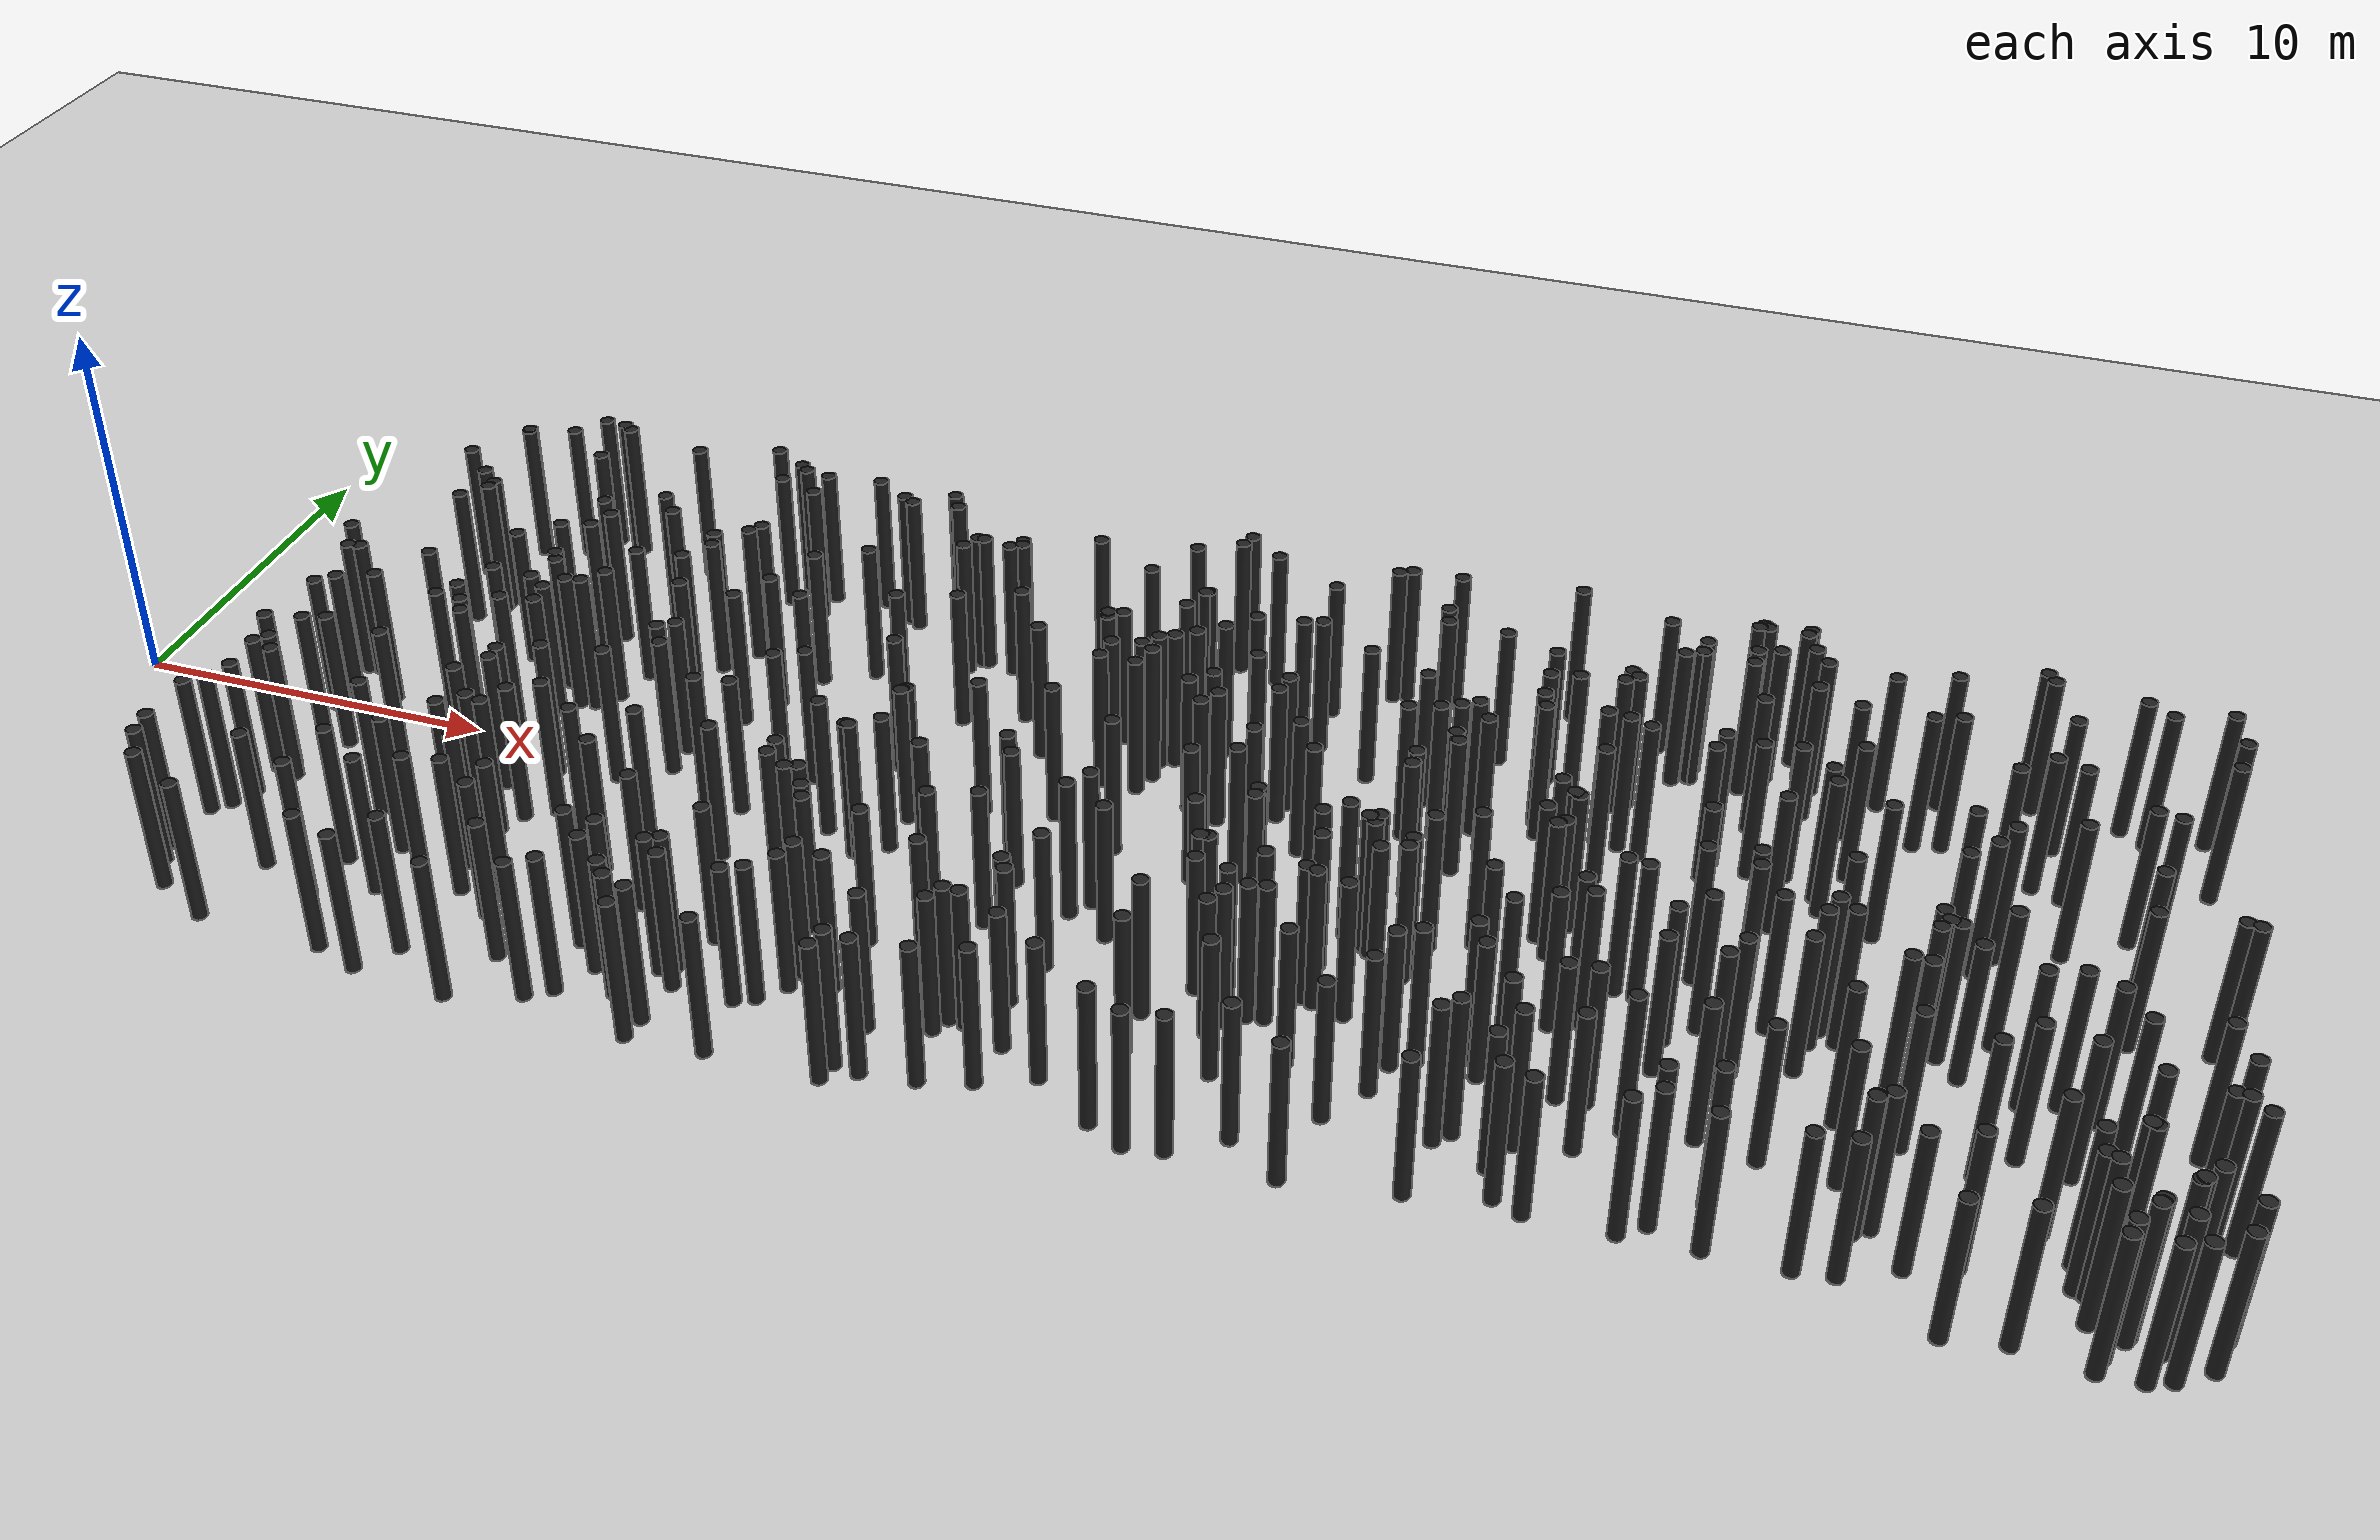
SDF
<sdf version="1.7">
 <world name="default">
  <light name="sun" type="directional">
   <cast_shadows>0</cast_shadows>
   <pose>0 0 10 0 -0 0</pose>
   <diffuse>0.8 0.8 0.8 1</diffuse>
   <specular>0.2 0.2 0.2 1</specular>
   <attenuation>
    <range>1000</range>
    <constant>0.9</constant>
    <linear>0.01</linear>
    <quadratic>0.001</quadratic>
   </attenuation>
   <direction>-0.5 0.1 -0.9</direction>
   <spot><inner_angle>0</inner_angle><outer_angle>0</outer_angle><falloff>0</falloff></spot>
  </light>
  <model name="ground_plane">
   <static>1</static>
   <link name="link">
    <collision name="collision">
     <geometry><plane><normal>0 0 1</normal><size>200 200</size></plane></geometry>
     <surface><friction><ode><mu>100</mu><mu2>50</mu2></ode></friction></surface>
    </collision>
    <visual name="visual">
     <cast_shadows>0</cast_shadows>
     <geometry><plane><normal>0 0 1</normal><size>200 200</size></plane></geometry>
     <material>
      <script><uri>file://media/materials/scripts/gazebo.material</uri><name>Gazebo/Grey</name></script>
     </material>
    </visual>
   </link>
  </model>
  <physics name="default_physics" default="0" type="ode">
   <max_step_size>0.001</max_step_size>
   <real_time_factor>1</real_time_factor>
   <real_time_update_rate>1000</real_time_update_rate>
  </physics>
  <scene>
   <ambient>0.4 0.4 0.4 1</ambient>
   <background>0.7 0.7 0.7 1</background>
   <shadows>0</shadows>
   <grid>0</grid>
  </scene>
  <spherical_coordinates>
   <surface_model>EARTH_WGS84</surface_model>
   <latitude_deg>0</latitude_deg>
   <longitude_deg>0</longitude_deg>
   <elevation>0</elevation>
   <heading_deg>0</heading_deg>
  </spherical_coordinates>
  <gravity>0 0 -9.8</gravity>
  <magnetic_field>6e-06 2.3e-05 -4.2e-05</magnetic_field>
  <atmosphere type="adiabatic"/>
  <model name="forest_clone_0_0">
   <pose>7.24116 6.37058 0.00358 0 -0 0</pose>
   <static>1</static>
   <link name="cylinder::link">
    <inertial>
     <mass>1</mass>
     <inertia><ixx>0.083</ixx><ixy>0</ixy><ixz>0</ixz><iyy>0.083</iyy><iyz>0</iyz><izz>0.083</izz></inertia>
    </inertial>
    <collision name="collision">
     <geometry><cylinder><radius>0.2</radius><length>4</length></cylinder></geometry>
    </collision>
    <visual name="visual">
     <geometry><cylinder><radius>0.2</radius><length>4</length></cylinder></geometry>
     <material>
      <script><uri>file://media/materials/scripts/gazebo.material</uri><name>Gazebo/Black</name></script>
     </material>
    </visual>
    <pose>0 0 2 0 -0 0</pose>
   </link>
  </model>
  <model name="forest_clone_1_0">
   <pose>38.5834 1.50586 0.00445 0 -0 0</pose>
   <static>1</static>
   <link name="cylinder::link">
    <inertial>
     <mass>1</mass>
     <inertia><ixx>0.083</ixx><ixy>0</ixy><ixz>0</ixz><iyy>0.083</iyy><iyz>0</iyz><izz>0.083</izz></inertia>
    </inertial>
    <collision name="collision">
     <geometry><cylinder><radius>0.2</radius><length>4</length></cylinder></geometry>
    </collision>
    <visual name="visual">
     <geometry><cylinder><radius>0.2</radius><length>4</length></cylinder></geometry>
     <material>
      <script><uri>file://media/materials/scripts/gazebo.material</uri><name>Gazebo/Black</name></script>
     </material>
    </visual>
    <pose>0 0 2 0 -0 0</pose>
   </link>
  </model>
  <model name="forest_clone_2_0">
   <pose>39.5517 -7.04721 0.00348 0 -0 0</pose>
   <static>1</static>
   <link name="cylinder::link">
    <inertial>
     <mass>1</mass>
     <inertia><ixx>0.083</ixx><ixy>0</ixy><ixz>0</ixz><iyy>0.083</iyy><iyz>0</iyz><izz>0.083</izz></inertia>
    </inertial>
    <collision name="collision">
     <geometry><cylinder><radius>0.2</radius><length>4</length></cylinder></geometry>
    </collision>
    <visual name="visual">
     <geometry><cylinder><radius>0.2</radius><length>4</length></cylinder></geometry>
     <material>
      <script><uri>file://media/materials/scripts/gazebo.material</uri><name>Gazebo/Black</name></script>
     </material>
    </visual>
    <pose>0 0 2 0 -0 0</pose>
   </link>
  </model>
  <model name="forest_clone_3_0">
   <pose>45.0865 -2.57981 0.00482 0 -0 0</pose>
   <static>1</static>
   <link name="cylinder::link">
    <inertial>
     <mass>1</mass>
     <inertia><ixx>0.083</ixx><ixy>0</ixy><ixz>0</ixz><iyy>0.083</iyy><iyz>0</iyz><izz>0.083</izz></inertia>
    </inertial>
    <collision name="collision">
     <geometry><cylinder><radius>0.2</radius><length>4</length></cylinder></geometry>
    </collision>
    <visual name="visual">
     <geometry><cylinder><radius>0.2</radius><length>4</length></cylinder></geometry>
     <material>
      <script><uri>file://media/materials/scripts/gazebo.material</uri><name>Gazebo/Black</name></script>
     </material>
    </visual>
    <pose>0 0 2 0 -0 0</pose>
   </link>
  </model>
  <model name="forest_clone_4_0">
   <pose>35.8735 2.26879 0.00285 0 -0 0</pose>
   <static>1</static>
   <link name="cylinder::link">
    <inertial>
     <mass>1</mass>
     <inertia><ixx>0.083</ixx><ixy>0</ixy><ixz>0</ixz><iyy>0.083</iyy><iyz>0</iyz><izz>0.083</izz></inertia>
    </inertial>
    <collision name="collision">
     <geometry><cylinder><radius>0.2</radius><length>4</length></cylinder></geometry>
    </collision>
    <visual name="visual">
     <geometry><cylinder><radius>0.2</radius><length>4</length></cylinder></geometry>
     <material>
      <script><uri>file://media/materials/scripts/gazebo.material</uri><name>Gazebo/Black</name></script>
     </material>
    </visual>
    <pose>0 0 2 0 -0 0</pose>
   </link>
  </model>
  <model name="forest_clone_5_0">
   <pose>26.4891 3.75465 -0.00317 0 -0 0</pose>
   <static>1</static>
   <link name="cylinder::link">
    <inertial>
     <mass>1</mass>
     <inertia><ixx>0.083</ixx><ixy>0</ixy><ixz>0</ixz><iyy>0.083</iyy><iyz>0</iyz><izz>0.083</izz></inertia>
    </inertial>
    <collision name="collision">
     <geometry><cylinder><radius>0.2</radius><length>4</length></cylinder></geometry>
    </collision>
    <visual name="visual">
     <geometry><cylinder><radius>0.2</radius><length>4</length></cylinder></geometry>
     <material>
      <script><uri>file://media/materials/scripts/gazebo.material</uri><name>Gazebo/Black</name></script>
     </material>
    </visual>
    <pose>0 0 2 0 -0 0</pose>
   </link>
  </model>
  <model name="forest_clone_6_0">
   <pose>32.0741 -4.34645 -0.00115 0 -0 0</pose>
   <static>1</static>
   <link name="cylinder::link">
    <inertial>
     <mass>1</mass>
     <inertia><ixx>0.083</ixx><ixy>0</ixy><ixz>0</ixz><iyy>0.083</iyy><iyz>0</iyz><izz>0.083</izz></inertia>
    </inertial>
    <collision name="collision">
     <geometry><cylinder><radius>0.2</radius><length>4</length></cylinder></geometry>
    </collision>
    <visual name="visual">
     <geometry><cylinder><radius>0.2</radius><length>4</length></cylinder></geometry>
     <material>
      <script><uri>file://media/materials/scripts/gazebo.material</uri><name>Gazebo/Black</name></script>
     </material>
    </visual>
    <pose>0 0 2 0 -0 0</pose>
   </link>
  </model>
  <model name="forest_clone_7_0">
   <pose>5.27494 -7.51544 0.00194 0 -0 0</pose>
   <static>1</static>
   <link name="cylinder::link">
    <inertial>
     <mass>1</mass>
     <inertia><ixx>0.083</ixx><ixy>0</ixy><ixz>0</ixz><iyy>0.083</iyy><iyz>0</iyz><izz>0.083</izz></inertia>
    </inertial>
    <collision name="collision">
     <geometry><cylinder><radius>0.2</radius><length>4</length></cylinder></geometry>
    </collision>
    <visual name="visual">
     <geometry><cylinder><radius>0.2</radius><length>4</length></cylinder></geometry>
     <material>
      <script><uri>file://media/materials/scripts/gazebo.material</uri><name>Gazebo/Black</name></script>
     </material>
    </visual>
    <pose>0 0 2 0 -0 0</pose>
   </link>
  </model>
  <model name="forest_clone_8_0">
   <pose>14.3487 4.0737 -0.00381 0 -0 0</pose>
   <static>1</static>
   <link name="cylinder::link">
    <inertial>
     <mass>1</mass>
     <inertia><ixx>0.083</ixx><ixy>0</ixy><ixz>0</ixz><iyy>0.083</iyy><iyz>0</iyz><izz>0.083</izz></inertia>
    </inertial>
    <collision name="collision">
     <geometry><cylinder><radius>0.2</radius><length>4</length></cylinder></geometry>
    </collision>
    <visual name="visual">
     <geometry><cylinder><radius>0.2</radius><length>4</length></cylinder></geometry>
     <material>
      <script><uri>file://media/materials/scripts/gazebo.material</uri><name>Gazebo/Black</name></script>
     </material>
    </visual>
    <pose>0 0 2 0 -0 0</pose>
   </link>
  </model>
  <model name="forest_clone_9_0">
   <pose>5.24685 2.64492 0.00361 0 -0 0</pose>
   <static>1</static>
   <link name="cylinder::link">
    <inertial>
     <mass>1</mass>
     <inertia><ixx>0.083</ixx><ixy>0</ixy><ixz>0</ixz><iyy>0.083</iyy><iyz>0</iyz><izz>0.083</izz></inertia>
    </inertial>
    <collision name="collision">
     <geometry><cylinder><radius>0.2</radius><length>4</length></cylinder></geometry>
    </collision>
    <visual name="visual">
     <geometry><cylinder><radius>0.2</radius><length>4</length></cylinder></geometry>
     <material>
      <script><uri>file://media/materials/scripts/gazebo.material</uri><name>Gazebo/Black</name></script>
     </material>
    </visual>
    <pose>0 0 2 0 -0 0</pose>
   </link>
  </model>
  <model name="forest_clone_10_0">
   <pose>39.0963 -6.09529 0.00332 0 -0 0</pose>
   <static>1</static>
   <link name="cylinder::link">
    <inertial>
     <mass>1</mass>
     <inertia><ixx>0.083</ixx><ixy>0</ixy><ixz>0</ixz><iyy>0.083</iyy><iyz>0</iyz><izz>0.083</izz></inertia>
    </inertial>
    <collision name="collision">
     <geometry><cylinder><radius>0.2</radius><length>4</length></cylinder></geometry>
    </collision>
    <visual name="visual">
     <geometry><cylinder><radius>0.2</radius><length>4</length></cylinder></geometry>
     <material>
      <script><uri>file://media/materials/scripts/gazebo.material</uri><name>Gazebo/Black</name></script>
     </material>
    </visual>
    <pose>0 0 2 0 -0 0</pose>
   </link>
  </model>
  <model name="forest_clone_11_0">
   <pose>6.44481 -3.3003 -0.00358 0 -0 0</pose>
   <static>1</static>
   <link name="cylinder::link">
    <inertial>
     <mass>1</mass>
     <inertia><ixx>0.083</ixx><ixy>0</ixy><ixz>0</ixz><iyy>0.083</iyy><iyz>0</iyz><izz>0.083</izz></inertia>
    </inertial>
    <collision name="collision">
     <geometry><cylinder><radius>0.2</radius><length>4</length></cylinder></geometry>
    </collision>
    <visual name="visual">
     <geometry><cylinder><radius>0.2</radius><length>4</length></cylinder></geometry>
     <material>
      <script><uri>file://media/materials/scripts/gazebo.material</uri><name>Gazebo/Black</name></script>
     </material>
    </visual>
    <pose>0 0 2 0 -0 0</pose>
   </link>
  </model>
  <model name="forest_clone_12_0">
   <pose>18.8097 8.72612 0.00448 0 -0 0</pose>
   <static>1</static>
   <link name="cylinder::link">
    <inertial>
     <mass>1</mass>
     <inertia><ixx>0.083</ixx><ixy>0</ixy><ixz>0</ixz><iyy>0.083</iyy><iyz>0</iyz><izz>0.083</izz></inertia>
    </inertial>
    <collision name="collision">
     <geometry><cylinder><radius>0.2</radius><length>4</length></cylinder></geometry>
    </collision>
    <visual name="visual">
     <geometry><cylinder><radius>0.2</radius><length>4</length></cylinder></geometry>
     <material>
      <script><uri>file://media/materials/scripts/gazebo.material</uri><name>Gazebo/Black</name></script>
     </material>
    </visual>
    <pose>0 0 2 0 -0 0</pose>
   </link>
  </model>
  <model name="forest_clone_13_0">
   <pose>5.80687 -8.34384 -0.00076 0 -0 0</pose>
   <static>1</static>
   <link name="cylinder::link">
    <inertial>
     <mass>1</mass>
     <inertia><ixx>0.083</ixx><ixy>0</ixy><ixz>0</ixz><iyy>0.083</iyy><iyz>0</iyz><izz>0.083</izz></inertia>
    </inertial>
    <collision name="collision">
     <geometry><cylinder><radius>0.2</radius><length>4</length></cylinder></geometry>
    </collision>
    <visual name="visual">
     <geometry><cylinder><radius>0.2</radius><length>4</length></cylinder></geometry>
     <material>
      <script><uri>file://media/materials/scripts/gazebo.material</uri><name>Gazebo/Black</name></script>
     </material>
    </visual>
    <pose>0 0 2 0 -0 0</pose>
   </link>
  </model>
  <model name="forest_clone_14_0">
   <pose>21.9944 4.5321 0.00088 0 -0 0</pose>
   <static>1</static>
   <link name="cylinder::link">
    <inertial>
     <mass>1</mass>
     <inertia><ixx>0.083</ixx><ixy>0</ixy><ixz>0</ixz><iyy>0.083</iyy><iyz>0</iyz><izz>0.083</izz></inertia>
    </inertial>
    <collision name="collision">
     <geometry><cylinder><radius>0.2</radius><length>4</length></cylinder></geometry>
    </collision>
    <visual name="visual">
     <geometry><cylinder><radius>0.2</radius><length>4</length></cylinder></geometry>
     <material>
      <script><uri>file://media/materials/scripts/gazebo.material</uri><name>Gazebo/Black</name></script>
     </material>
    </visual>
    <pose>0 0 2 0 -0 0</pose>
   </link>
  </model>
  <model name="forest_clone_15_0">
   <pose>26.0231 4.81206 -0.0042 0 -0 0</pose>
   <static>1</static>
   <link name="cylinder::link">
    <inertial>
     <mass>1</mass>
     <inertia><ixx>0.083</ixx><ixy>0</ixy><ixz>0</ixz><iyy>0.083</iyy><iyz>0</iyz><izz>0.083</izz></inertia>
    </inertial>
    <collision name="collision">
     <geometry><cylinder><radius>0.2</radius><length>4</length></cylinder></geometry>
    </collision>
    <visual name="visual">
     <geometry><cylinder><radius>0.2</radius><length>4</length></cylinder></geometry>
     <material>
      <script><uri>file://media/materials/scripts/gazebo.material</uri><name>Gazebo/Black</name></script>
     </material>
    </visual>
    <pose>0 0 2 0 -0 0</pose>
   </link>
  </model>
  <model name="forest_clone_16_0">
   <pose>16.3894 9.09389 -0.00079 0 -0 0</pose>
   <static>1</static>
   <link name="cylinder::link">
    <inertial>
     <mass>1</mass>
     <inertia><ixx>0.083</ixx><ixy>0</ixy><ixz>0</ixz><iyy>0.083</iyy><iyz>0</iyz><izz>0.083</izz></inertia>
    </inertial>
    <collision name="collision">
     <geometry><cylinder><radius>0.2</radius><length>4</length></cylinder></geometry>
    </collision>
    <visual name="visual">
     <geometry><cylinder><radius>0.2</radius><length>4</length></cylinder></geometry>
     <material>
      <script><uri>file://media/materials/scripts/gazebo.material</uri><name>Gazebo/Black</name></script>
     </material>
    </visual>
    <pose>0 0 2 0 -0 0</pose>
   </link>
  </model>
  <model name="forest_clone_17_0">
   <pose>18.3084 -8.63581 0.00226 0 -0 0</pose>
   <static>1</static>
   <link name="cylinder::link">
    <inertial>
     <mass>1</mass>
     <inertia><ixx>0.083</ixx><ixy>0</ixy><ixz>0</ixz><iyy>0.083</iyy><iyz>0</iyz><izz>0.083</izz></inertia>
    </inertial>
    <collision name="collision">
     <geometry><cylinder><radius>0.2</radius><length>4</length></cylinder></geometry>
    </collision>
    <visual name="visual">
     <geometry><cylinder><radius>0.2</radius><length>4</length></cylinder></geometry>
     <material>
      <script><uri>file://media/materials/scripts/gazebo.material</uri><name>Gazebo/Black</name></script>
     </material>
    </visual>
    <pose>0 0 2 0 -0 0</pose>
   </link>
  </model>
  <model name="forest_clone_18_0">
   <pose>6.99982 -1.56223 -0.00319 0 -0 0</pose>
   <static>1</static>
   <link name="cylinder::link">
    <inertial>
     <mass>1</mass>
     <inertia><ixx>0.083</ixx><ixy>0</ixy><ixz>0</ixz><iyy>0.083</iyy><iyz>0</iyz><izz>0.083</izz></inertia>
    </inertial>
    <collision name="collision">
     <geometry><cylinder><radius>0.2</radius><length>4</length></cylinder></geometry>
    </collision>
    <visual name="visual">
     <geometry><cylinder><radius>0.2</radius><length>4</length></cylinder></geometry>
     <material>
      <script><uri>file://media/materials/scripts/gazebo.material</uri><name>Gazebo/Black</name></script>
     </material>
    </visual>
    <pose>0 0 2 0 -0 0</pose>
   </link>
  </model>
  <model name="forest_clone_19_0">
   <pose>48.0424 3.29449 0.00499 0 -0 0</pose>
   <static>1</static>
   <link name="cylinder::link">
    <inertial>
     <mass>1</mass>
     <inertia><ixx>0.083</ixx><ixy>0</ixy><ixz>0</ixz><iyy>0.083</iyy><iyz>0</iyz><izz>0.083</izz></inertia>
    </inertial>
    <collision name="collision">
     <geometry><cylinder><radius>0.2</radius><length>4</length></cylinder></geometry>
    </collision>
    <visual name="visual">
     <geometry><cylinder><radius>0.2</radius><length>4</length></cylinder></geometry>
     <material>
      <script><uri>file://media/materials/scripts/gazebo.material</uri><name>Gazebo/Black</name></script>
     </material>
    </visual>
    <pose>0 0 2 0 -0 0</pose>
   </link>
  </model>
  <model name="forest_clone_20_0">
   <pose>17.5492 -7.24611 0.00177 0 -0 0</pose>
   <static>1</static>
   <link name="cylinder::link">
    <inertial>
     <mass>1</mass>
     <inertia><ixx>0.083</ixx><ixy>0</ixy><ixz>0</ixz><iyy>0.083</iyy><iyz>0</iyz><izz>0.083</izz></inertia>
    </inertial>
    <collision name="collision">
     <geometry><cylinder><radius>0.2</radius><length>4</length></cylinder></geometry>
    </collision>
    <visual name="visual">
     <geometry><cylinder><radius>0.2</radius><length>4</length></cylinder></geometry>
     <material>
      <script><uri>file://media/materials/scripts/gazebo.material</uri><name>Gazebo/Black</name></script>
     </material>
    </visual>
    <pose>0 0 2 0 -0 0</pose>
   </link>
  </model>
  <model name="forest_clone_21_0">
   <pose>30.4034 -9.34154 -0.0007 0 -0 0</pose>
   <static>1</static>
   <link name="cylinder::link">
    <inertial>
     <mass>1</mass>
     <inertia><ixx>0.083</ixx><ixy>0</ixy><ixz>0</ixz><iyy>0.083</iyy><iyz>0</iyz><izz>0.083</izz></inertia>
    </inertial>
    <collision name="collision">
     <geometry><cylinder><radius>0.2</radius><length>4</length></cylinder></geometry>
    </collision>
    <visual name="visual">
     <geometry><cylinder><radius>0.2</radius><length>4</length></cylinder></geometry>
     <material>
      <script><uri>file://media/materials/scripts/gazebo.material</uri><name>Gazebo/Black</name></script>
     </material>
    </visual>
    <pose>0 0 2 0 -0 0</pose>
   </link>
  </model>
  <model name="forest_clone_22_0">
   <pose>31.0304 1.21216 -0.00082 0 -0 0</pose>
   <static>1</static>
   <link name="cylinder::link">
    <inertial>
     <mass>1</mass>
     <inertia><ixx>0.083</ixx><ixy>0</ixy><ixz>0</ixz><iyy>0.083</iyy><iyz>0</iyz><izz>0.083</izz></inertia>
    </inertial>
    <collision name="collision">
     <geometry><cylinder><radius>0.2</radius><length>4</length></cylinder></geometry>
    </collision>
    <visual name="visual">
     <geometry><cylinder><radius>0.2</radius><length>4</length></cylinder></geometry>
     <material>
      <script><uri>file://media/materials/scripts/gazebo.material</uri><name>Gazebo/Black</name></script>
     </material>
    </visual>
    <pose>0 0 2 0 -0 0</pose>
   </link>
  </model>
  <model name="forest_clone_23_0">
   <pose>11.6534 0.871969 -0.00336 0 -0 0</pose>
   <static>1</static>
   <link name="cylinder::link">
    <inertial>
     <mass>1</mass>
     <inertia><ixx>0.083</ixx><ixy>0</ixy><ixz>0</ixz><iyy>0.083</iyy><iyz>0</iyz><izz>0.083</izz></inertia>
    </inertial>
    <collision name="collision">
     <geometry><cylinder><radius>0.2</radius><length>4</length></cylinder></geometry>
    </collision>
    <visual name="visual">
     <geometry><cylinder><radius>0.2</radius><length>4</length></cylinder></geometry>
     <material>
      <script><uri>file://media/materials/scripts/gazebo.material</uri><name>Gazebo/Black</name></script>
     </material>
    </visual>
    <pose>0 0 2 0 -0 0</pose>
   </link>
  </model>
  <model name="forest_clone_24_0">
   <pose>29.3927 8.99702 0.00213 0 -0 0</pose>
   <static>1</static>
   <link name="cylinder::link">
    <inertial>
     <mass>1</mass>
     <inertia><ixx>0.083</ixx><ixy>0</ixy><ixz>0</ixz><iyy>0.083</iyy><iyz>0</iyz><izz>0.083</izz></inertia>
    </inertial>
    <collision name="collision">
     <geometry><cylinder><radius>0.2</radius><length>4</length></cylinder></geometry>
    </collision>
    <visual name="visual">
     <geometry><cylinder><radius>0.2</radius><length>4</length></cylinder></geometry>
     <material>
      <script><uri>file://media/materials/scripts/gazebo.material</uri><name>Gazebo/Black</name></script>
     </material>
    </visual>
    <pose>0 0 2 0 -0 0</pose>
   </link>
  </model>
  <model name="forest_clone_25_0">
   <pose>21.1492 -3.74001 -0.00472 0 -0 0</pose>
   <static>1</static>
   <link name="cylinder::link">
    <inertial>
     <mass>1</mass>
     <inertia><ixx>0.083</ixx><ixy>0</ixy><ixz>0</ixz><iyy>0.083</iyy><iyz>0</iyz><izz>0.083</izz></inertia>
    </inertial>
    <collision name="collision">
     <geometry><cylinder><radius>0.2</radius><length>4</length></cylinder></geometry>
    </collision>
    <visual name="visual">
     <geometry><cylinder><radius>0.2</radius><length>4</length></cylinder></geometry>
     <material>
      <script><uri>file://media/materials/scripts/gazebo.material</uri><name>Gazebo/Black</name></script>
     </material>
    </visual>
    <pose>0 0 2 0 -0 0</pose>
   </link>
  </model>
  <model name="forest_clone_26_0">
   <pose>28.6033 -2.97139 0.00277 0 -0 0</pose>
   <static>1</static>
   <link name="cylinder::link">
    <inertial>
     <mass>1</mass>
     <inertia><ixx>0.083</ixx><ixy>0</ixy><ixz>0</ixz><iyy>0.083</iyy><iyz>0</iyz><izz>0.083</izz></inertia>
    </inertial>
    <collision name="collision">
     <geometry><cylinder><radius>0.2</radius><length>4</length></cylinder></geometry>
    </collision>
    <visual name="visual">
     <geometry><cylinder><radius>0.2</radius><length>4</length></cylinder></geometry>
     <material>
      <script><uri>file://media/materials/scripts/gazebo.material</uri><name>Gazebo/Black</name></script>
     </material>
    </visual>
    <pose>0 0 2 0 -0 0</pose>
   </link>
  </model>
  <model name="forest_clone_27_0">
   <pose>42.8595 -8.59229 0.00473 0 -0 0</pose>
   <static>1</static>
   <link name="cylinder::link">
    <inertial>
     <mass>1</mass>
     <inertia><ixx>0.083</ixx><ixy>0</ixy><ixz>0</ixz><iyy>0.083</iyy><iyz>0</iyz><izz>0.083</izz></inertia>
    </inertial>
    <collision name="collision">
     <geometry><cylinder><radius>0.2</radius><length>4</length></cylinder></geometry>
    </collision>
    <visual name="visual">
     <geometry><cylinder><radius>0.2</radius><length>4</length></cylinder></geometry>
     <material>
      <script><uri>file://media/materials/scripts/gazebo.material</uri><name>Gazebo/Black</name></script>
     </material>
    </visual>
    <pose>0 0 2 0 -0 0</pose>
   </link>
  </model>
  <model name="forest_clone_28_0">
   <pose>39.8111 9.13937 0.00124 0 -0 0</pose>
   <static>1</static>
   <link name="cylinder::link">
    <inertial>
     <mass>1</mass>
     <inertia><ixx>0.083</ixx><ixy>0</ixy><ixz>0</ixz><iyy>0.083</iyy><iyz>0</iyz><izz>0.083</izz></inertia>
    </inertial>
    <collision name="collision">
     <geometry><cylinder><radius>0.2</radius><length>4</length></cylinder></geometry>
    </collision>
    <visual name="visual">
     <geometry><cylinder><radius>0.2</radius><length>4</length></cylinder></geometry>
     <material>
      <script><uri>file://media/materials/scripts/gazebo.material</uri><name>Gazebo/Black</name></script>
     </material>
    </visual>
    <pose>0 0 2 0 -0 0</pose>
   </link>
  </model>
  <model name="forest_clone_29_0">
   <pose>43.5072 9.02108 -0.00067 0 -0 0</pose>
   <static>1</static>
   <link name="cylinder::link">
    <inertial>
     <mass>1</mass>
     <inertia><ixx>0.083</ixx><ixy>0</ixy><ixz>0</ixz><iyy>0.083</iyy><iyz>0</iyz><izz>0.083</izz></inertia>
    </inertial>
    <collision name="collision">
     <geometry><cylinder><radius>0.2</radius><length>4</length></cylinder></geometry>
    </collision>
    <visual name="visual">
     <geometry><cylinder><radius>0.2</radius><length>4</length></cylinder></geometry>
     <material>
      <script><uri>file://media/materials/scripts/gazebo.material</uri><name>Gazebo/Black</name></script>
     </material>
    </visual>
    <pose>0 0 2 0 -0 0</pose>
   </link>
  </model>
  <model name="forest_clone_30_0">
   <pose>31.2475 -4.13791 -0.00402 0 -0 0</pose>
   <static>1</static>
   <link name="cylinder::link">
    <inertial>
     <mass>1</mass>
     <inertia><ixx>0.083</ixx><ixy>0</ixy><ixz>0</ixz><iyy>0.083</iyy><iyz>0</iyz><izz>0.083</izz></inertia>
    </inertial>
    <collision name="collision">
     <geometry><cylinder><radius>0.2</radius><length>4</length></cylinder></geometry>
    </collision>
    <visual name="visual">
     <geometry><cylinder><radius>0.2</radius><length>4</length></cylinder></geometry>
     <material>
      <script><uri>file://media/materials/scripts/gazebo.material</uri><name>Gazebo/Black</name></script>
     </material>
    </visual>
    <pose>0 0 2 0 -0 0</pose>
   </link>
  </model>
  <model name="forest_clone_31_0">
   <pose>35.7719 -2.19632 0.00463 0 -0 0</pose>
   <static>1</static>
   <link name="cylinder::link">
    <inertial>
     <mass>1</mass>
     <inertia><ixx>0.083</ixx><ixy>0</ixy><ixz>0</ixz><iyy>0.083</iyy><iyz>0</iyz><izz>0.083</izz></inertia>
    </inertial>
    <collision name="collision">
     <geometry><cylinder><radius>0.2</radius><length>4</length></cylinder></geometry>
    </collision>
    <visual name="visual">
     <geometry><cylinder><radius>0.2</radius><length>4</length></cylinder></geometry>
     <material>
      <script><uri>file://media/materials/scripts/gazebo.material</uri><name>Gazebo/Black</name></script>
     </material>
    </visual>
    <pose>0 0 2 0 -0 0</pose>
   </link>
  </model>
  <model name="forest_clone_32_0">
   <pose>5.68981 1.71933 0.00222 0 -0 0</pose>
   <static>1</static>
   <link name="cylinder::link">
    <inertial>
     <mass>1</mass>
     <inertia><ixx>0.083</ixx><ixy>0</ixy><ixz>0</ixz><iyy>0.083</iyy><iyz>0</iyz><izz>0.083</izz></inertia>
    </inertial>
    <collision name="collision">
     <geometry><cylinder><radius>0.2</radius><length>4</length></cylinder></geometry>
    </collision>
    <visual name="visual">
     <geometry><cylinder><radius>0.2</radius><length>4</length></cylinder></geometry>
     <material>
      <script><uri>file://media/materials/scripts/gazebo.material</uri><name>Gazebo/Black</name></script>
     </material>
    </visual>
    <pose>0 0 2 0 -0 0</pose>
   </link>
  </model>
  <model name="forest_clone_33_0">
   <pose>23.9728 0.91482 -0.00431 0 -0 0</pose>
   <static>1</static>
   <link name="cylinder::link">
    <inertial>
     <mass>1</mass>
     <inertia><ixx>0.083</ixx><ixy>0</ixy><ixz>0</ixz><iyy>0.083</iyy><iyz>0</iyz><izz>0.083</izz></inertia>
    </inertial>
    <collision name="collision">
     <geometry><cylinder><radius>0.2</radius><length>4</length></cylinder></geometry>
    </collision>
    <visual name="visual">
     <geometry><cylinder><radius>0.2</radius><length>4</length></cylinder></geometry>
     <material>
      <script><uri>file://media/materials/scripts/gazebo.material</uri><name>Gazebo/Black</name></script>
     </material>
    </visual>
    <pose>0 0 2 0 -0 0</pose>
   </link>
  </model>
  <model name="forest_clone_34_0">
   <pose>41.9639 4.60308 -0.00078 0 -0 0</pose>
   <static>1</static>
   <link name="cylinder::link">
    <inertial>
     <mass>1</mass>
     <inertia><ixx>0.083</ixx><ixy>0</ixy><ixz>0</ixz><iyy>0.083</iyy><iyz>0</iyz><izz>0.083</izz></inertia>
    </inertial>
    <collision name="collision">
     <geometry><cylinder><radius>0.2</radius><length>4</length></cylinder></geometry>
    </collision>
    <visual name="visual">
     <geometry><cylinder><radius>0.2</radius><length>4</length></cylinder></geometry>
     <material>
      <script><uri>file://media/materials/scripts/gazebo.material</uri><name>Gazebo/Black</name></script>
     </material>
    </visual>
    <pose>0 0 2 0 -0 0</pose>
   </link>
  </model>
  <model name="forest_clone_35_0">
   <pose>40.2155 -9.10501 0.00091 0 -0 0</pose>
   <static>1</static>
   <link name="cylinder::link">
    <inertial>
     <mass>1</mass>
     <inertia><ixx>0.083</ixx><ixy>0</ixy><ixz>0</ixz><iyy>0.083</iyy><iyz>0</iyz><izz>0.083</izz></inertia>
    </inertial>
    <collision name="collision">
     <geometry><cylinder><radius>0.2</radius><length>4</length></cylinder></geometry>
    </collision>
    <visual name="visual">
     <geometry><cylinder><radius>0.2</radius><length>4</length></cylinder></geometry>
     <material>
      <script><uri>file://media/materials/scripts/gazebo.material</uri><name>Gazebo/Black</name></script>
     </material>
    </visual>
    <pose>0 0 2 0 -0 0</pose>
   </link>
  </model>
  <model name="forest_clone_36_0">
   <pose>28.412 4.88187 -0.00262 0 -0 0</pose>
   <static>1</static>
   <link name="cylinder::link">
    <inertial>
     <mass>1</mass>
     <inertia><ixx>0.083</ixx><ixy>0</ixy><ixz>0</ixz><iyy>0.083</iyy><iyz>0</iyz><izz>0.083</izz></inertia>
    </inertial>
    <collision name="collision">
     <geometry><cylinder><radius>0.2</radius><length>4</length></cylinder></geometry>
    </collision>
    <visual name="visual">
     <geometry><cylinder><radius>0.2</radius><length>4</length></cylinder></geometry>
     <material>
      <script><uri>file://media/materials/scripts/gazebo.material</uri><name>Gazebo/Black</name></script>
     </material>
    </visual>
    <pose>0 0 2 0 -0 0</pose>
   </link>
  </model>
  <model name="forest_clone_37_0">
   <pose>42.275 -9.06508 0.00423 0 -0 0</pose>
   <static>1</static>
   <link name="cylinder::link">
    <inertial>
     <mass>1</mass>
     <inertia><ixx>0.083</ixx><ixy>0</ixy><ixz>0</ixz><iyy>0.083</iyy><iyz>0</iyz><izz>0.083</izz></inertia>
    </inertial>
    <collision name="collision">
     <geometry><cylinder><radius>0.2</radius><length>4</length></cylinder></geometry>
    </collision>
    <visual name="visual">
     <geometry><cylinder><radius>0.2</radius><length>4</length></cylinder></geometry>
     <material>
      <script><uri>file://media/materials/scripts/gazebo.material</uri><name>Gazebo/Black</name></script>
     </material>
    </visual>
    <pose>0 0 2 0 -0 0</pose>
   </link>
  </model>
  <model name="forest_clone_38_0">
   <pose>32.3014 -9.67837 -0.00198 0 -0 0</pose>
   <static>1</static>
   <link name="cylinder::link">
    <inertial>
     <mass>1</mass>
     <inertia><ixx>0.083</ixx><ixy>0</ixy><ixz>0</ixz><iyy>0.083</iyy><iyz>0</iyz><izz>0.083</izz></inertia>
    </inertial>
    <collision name="collision">
     <geometry><cylinder><radius>0.2</radius><length>4</length></cylinder></geometry>
    </collision>
    <visual name="visual">
     <geometry><cylinder><radius>0.2</radius><length>4</length></cylinder></geometry>
     <material>
      <script><uri>file://media/materials/scripts/gazebo.material</uri><name>Gazebo/Black</name></script>
     </material>
    </visual>
    <pose>0 0 2 0 -0 0</pose>
   </link>
  </model>
  <model name="forest_clone_39_0">
   <pose>45.2577 -1.52691 -0.00272 0 -0 0</pose>
   <static>1</static>
   <link name="cylinder::link">
    <inertial>
     <mass>1</mass>
     <inertia><ixx>0.083</ixx><ixy>0</ixy><ixz>0</ixz><iyy>0.083</iyy><iyz>0</iyz><izz>0.083</izz></inertia>
    </inertial>
    <collision name="collision">
     <geometry><cylinder><radius>0.2</radius><length>4</length></cylinder></geometry>
    </collision>
    <visual name="visual">
     <geometry><cylinder><radius>0.2</radius><length>4</length></cylinder></geometry>
     <material>
      <script><uri>file://media/materials/scripts/gazebo.material</uri><name>Gazebo/Black</name></script>
     </material>
    </visual>
    <pose>0 0 2 0 -0 0</pose>
   </link>
  </model>
  <model name="forest_clone_40_0">
   <pose>35.9803 4.05859 0.00044 0 -0 0</pose>
   <static>1</static>
   <link name="cylinder::link">
    <inertial>
     <mass>1</mass>
     <inertia><ixx>0.083</ixx><ixy>0</ixy><ixz>0</ixz><iyy>0.083</iyy><iyz>0</iyz><izz>0.083</izz></inertia>
    </inertial>
    <collision name="collision">
     <geometry><cylinder><radius>0.2</radius><length>4</length></cylinder></geometry>
    </collision>
    <visual name="visual">
     <geometry><cylinder><radius>0.2</radius><length>4</length></cylinder></geometry>
     <material>
      <script><uri>file://media/materials/scripts/gazebo.material</uri><name>Gazebo/Black</name></script>
     </material>
    </visual>
    <pose>0 0 2 0 -0 0</pose>
   </link>
  </model>
  <model name="forest_clone_41_0">
   <pose>43.7077 -3.10852 0.00163 0 -0 0</pose>
   <static>1</static>
   <link name="cylinder::link">
    <inertial>
     <mass>1</mass>
     <inertia><ixx>0.083</ixx><ixy>0</ixy><ixz>0</ixz><iyy>0.083</iyy><iyz>0</iyz><izz>0.083</izz></inertia>
    </inertial>
    <collision name="collision">
     <geometry><cylinder><radius>0.2</radius><length>4</length></cylinder></geometry>
    </collision>
    <visual name="visual">
     <geometry><cylinder><radius>0.2</radius><length>4</length></cylinder></geometry>
     <material>
      <script><uri>file://media/materials/scripts/gazebo.material</uri><name>Gazebo/Black</name></script>
     </material>
    </visual>
    <pose>0 0 2 0 -0 0</pose>
   </link>
  </model>
  <model name="forest_clone_42_0">
   <pose>29.4441 1.92254 0.00434 0 -0 0</pose>
   <static>1</static>
   <link name="cylinder::link">
    <inertial>
     <mass>1</mass>
     <inertia><ixx>0.083</ixx><ixy>0</ixy><ixz>0</ixz><iyy>0.083</iyy><iyz>0</iyz><izz>0.083</izz></inertia>
    </inertial>
    <collision name="collision">
     <geometry><cylinder><radius>0.2</radius><length>4</length></cylinder></geometry>
    </collision>
    <visual name="visual">
     <geometry><cylinder><radius>0.2</radius><length>4</length></cylinder></geometry>
     <material>
      <script><uri>file://media/materials/scripts/gazebo.material</uri><name>Gazebo/Black</name></script>
     </material>
    </visual>
    <pose>0 0 2 0 -0 0</pose>
   </link>
  </model>
  <model name="forest_clone_43_0">
   <pose>45.8727 -1.3063 -0.00399 0 -0 0</pose>
   <static>1</static>
   <link name="cylinder::link">
    <inertial>
     <mass>1</mass>
     <inertia><ixx>0.083</ixx><ixy>0</ixy><ixz>0</ixz><iyy>0.083</iyy><iyz>0</iyz><izz>0.083</izz></inertia>
    </inertial>
    <collision name="collision">
     <geometry><cylinder><radius>0.2</radius><length>4</length></cylinder></geometry>
    </collision>
    <visual name="visual">
     <geometry><cylinder><radius>0.2</radius><length>4</length></cylinder></geometry>
     <material>
      <script><uri>file://media/materials/scripts/gazebo.material</uri><name>Gazebo/Black</name></script>
     </material>
    </visual>
    <pose>0 0 2 0 -0 0</pose>
   </link>
  </model>
  <model name="forest_clone_45_0">
   <pose>7.76228 5.9118 -0.0038 0 -0 0</pose>
   <static>1</static>
   <link name="cylinder::link">
    <inertial>
     <mass>1</mass>
     <inertia><ixx>0.083</ixx><ixy>0</ixy><ixz>0</ixz><iyy>0.083</iyy><iyz>0</iyz><izz>0.083</izz></inertia>
    </inertial>
    <collision name="collision">
     <geometry><cylinder><radius>0.2</radius><length>4</length></cylinder></geometry>
    </collision>
    <visual name="visual">
     <geometry><cylinder><radius>0.2</radius><length>4</length></cylinder></geometry>
     <material>
      <script><uri>file://media/materials/scripts/gazebo.material</uri><name>Gazebo/Black</name></script>
     </material>
    </visual>
    <pose>0 0 2 0 -0 0</pose>
   </link>
  </model>
  <model name="forest_clone_46_0">
   <pose>36.0803 -0.862235 -0.00083 0 -0 0</pose>
   <static>1</static>
   <link name="cylinder::link">
    <inertial>
     <mass>1</mass>
     <inertia><ixx>0.083</ixx><ixy>0</ixy><ixz>0</ixz><iyy>0.083</iyy><iyz>0</iyz><izz>0.083</izz></inertia>
    </inertial>
    <collision name="collision">
     <geometry><cylinder><radius>0.2</radius><length>4</length></cylinder></geometry>
    </collision>
    <visual name="visual">
     <geometry><cylinder><radius>0.2</radius><length>4</length></cylinder></geometry>
     <material>
      <script><uri>file://media/materials/scripts/gazebo.material</uri><name>Gazebo/Black</name></script>
     </material>
    </visual>
    <pose>0 0 2 0 -0 0</pose>
   </link>
  </model>
  <model name="forest_clone_47_0">
   <pose>21.241 6.89741 -0.00021 0 -0 0</pose>
   <static>1</static>
   <link name="cylinder::link">
    <inertial>
     <mass>1</mass>
     <inertia><ixx>0.083</ixx><ixy>0</ixy><ixz>0</ixz><iyy>0.083</iyy><iyz>0</iyz><izz>0.083</izz></inertia>
    </inertial>
    <collision name="collision">
     <geometry><cylinder><radius>0.2</radius><length>4</length></cylinder></geometry>
    </collision>
    <visual name="visual">
     <geometry><cylinder><radius>0.2</radius><length>4</length></cylinder></geometry>
     <material>
      <script><uri>file://media/materials/scripts/gazebo.material</uri><name>Gazebo/Black</name></script>
     </material>
    </visual>
    <pose>0 0 2 0 -0 0</pose>
   </link>
  </model>
  <model name="forest_clone_49_0">
   <pose>38.9766 1.07153 0.00405 0 -0 0</pose>
   <static>1</static>
   <link name="cylinder::link">
    <inertial>
     <mass>1</mass>
     <inertia><ixx>0.083</ixx><ixy>0</ixy><ixz>0</ixz><iyy>0.083</iyy><iyz>0</iyz><izz>0.083</izz></inertia>
    </inertial>
    <collision name="collision">
     <geometry><cylinder><radius>0.2</radius><length>4</length></cylinder></geometry>
    </collision>
    <visual name="visual">
     <geometry><cylinder><radius>0.2</radius><length>4</length></cylinder></geometry>
     <material>
      <script><uri>file://media/materials/scripts/gazebo.material</uri><name>Gazebo/Black</name></script>
     </material>
    </visual>
    <pose>0 0 2 0 -0 0</pose>
   </link>
  </model>
  <model name="forest_clone_50_0">
   <pose>11.5881 -4.08853 -0.00065 0 -0 0</pose>
   <static>1</static>
   <link name="cylinder::link">
    <inertial>
     <mass>1</mass>
     <inertia><ixx>0.083</ixx><ixy>0</ixy><ixz>0</ixz><iyy>0.083</iyy><iyz>0</iyz><izz>0.083</izz></inertia>
    </inertial>
    <collision name="collision">
     <geometry><cylinder><radius>0.2</radius><length>4</length></cylinder></geometry>
    </collision>
    <visual name="visual">
     <geometry><cylinder><radius>0.2</radius><length>4</length></cylinder></geometry>
     <material>
      <script><uri>file://media/materials/scripts/gazebo.material</uri><name>Gazebo/Black</name></script>
     </material>
    </visual>
    <pose>0 0 2 0 -0 0</pose>
   </link>
  </model>
  <model name="forest_clone_51_0">
   <pose>15.6414 0.059573 0.0023 0 -0 0</pose>
   <static>1</static>
   <link name="cylinder::link">
    <inertial>
     <mass>1</mass>
     <inertia><ixx>0.083</ixx><ixy>0</ixy><ixz>0</ixz><iyy>0.083</iyy><iyz>0</iyz><izz>0.083</izz></inertia>
    </inertial>
    <collision name="collision">
     <geometry><cylinder><radius>0.2</radius><length>4</length></cylinder></geometry>
    </collision>
    <visual name="visual">
     <geometry><cylinder><radius>0.2</radius><length>4</length></cylinder></geometry>
     <material>
      <script><uri>file://media/materials/scripts/gazebo.material</uri><name>Gazebo/Black</name></script>
     </material>
    </visual>
    <pose>0 0 2 0 -0 0</pose>
   </link>
  </model>
  <model name="forest_clone_52_0">
   <pose>33.5501 -8.8399 0.00296 0 -0 0</pose>
   <static>1</static>
   <link name="cylinder::link">
    <inertial>
     <mass>1</mass>
     <inertia><ixx>0.083</ixx><ixy>0</ixy><ixz>0</ixz><iyy>0.083</iyy><iyz>0</iyz><izz>0.083</izz></inertia>
    </inertial>
    <collision name="collision">
     <geometry><cylinder><radius>0.2</radius><length>4</length></cylinder></geometry>
    </collision>
    <visual name="visual">
     <geometry><cylinder><radius>0.2</radius><length>4</length></cylinder></geometry>
     <material>
      <script><uri>file://media/materials/scripts/gazebo.material</uri><name>Gazebo/Black</name></script>
     </material>
    </visual>
    <pose>0 0 2 0 -0 0</pose>
   </link>
  </model>
  <model name="forest_clone_53_0">
   <pose>52.7878 -8.81428 0.00484 0 -0 0</pose>
   <static>1</static>
   <link name="cylinder::link">
    <inertial>
     <mass>1</mass>
     <inertia><ixx>0.083</ixx><ixy>0</ixy><ixz>0</ixz><iyy>0.083</iyy><iyz>0</iyz><izz>0.083</izz></inertia>
    </inertial>
    <collision name="collision">
     <geometry><cylinder><radius>0.2</radius><length>4</length></cylinder></geometry>
    </collision>
    <visual name="visual">
     <geometry><cylinder><radius>0.2</radius><length>4</length></cylinder></geometry>
     <material>
      <script><uri>file://media/materials/scripts/gazebo.material</uri><name>Gazebo/Black</name></script>
     </material>
    </visual>
    <pose>0 0 2 0 -0 0</pose>
   </link>
  </model>
  <model name="forest_clone_54_0">
   <pose>28.2907 9.31701 -0.0016 0 -0 0</pose>
   <static>1</static>
   <link name="cylinder::link">
    <inertial>
     <mass>1</mass>
     <inertia><ixx>0.083</ixx><ixy>0</ixy><ixz>0</ixz><iyy>0.083</iyy><iyz>0</iyz><izz>0.083</izz></inertia>
    </inertial>
    <collision name="collision">
     <geometry><cylinder><radius>0.2</radius><length>4</length></cylinder></geometry>
    </collision>
    <visual name="visual">
     <geometry><cylinder><radius>0.2</radius><length>4</length></cylinder></geometry>
     <material>
      <script><uri>file://media/materials/scripts/gazebo.material</uri><name>Gazebo/Black</name></script>
     </material>
    </visual>
    <pose>0 0 2 0 -0 0</pose>
   </link>
  </model>
  <model name="forest_clone_55_0">
   <pose>31.2421 3.57787 0.00372 0 -0 0</pose>
   <static>1</static>
   <link name="cylinder::link">
    <inertial>
     <mass>1</mass>
     <inertia><ixx>0.083</ixx><ixy>0</ixy><ixz>0</ixz><iyy>0.083</iyy><iyz>0</iyz><izz>0.083</izz></inertia>
    </inertial>
    <collision name="collision">
     <geometry><cylinder><radius>0.2</radius><length>4</length></cylinder></geometry>
    </collision>
    <visual name="visual">
     <geometry><cylinder><radius>0.2</radius><length>4</length></cylinder></geometry>
     <material>
      <script><uri>file://media/materials/scripts/gazebo.material</uri><name>Gazebo/Black</name></script>
     </material>
    </visual>
    <pose>0 0 2 0 -0 0</pose>
   </link>
  </model>
  <model name="forest_clone_56_0">
   <pose>27.6638 -7.53181 0.00204 0 -0 0</pose>
   <static>1</static>
   <link name="cylinder::link">
    <inertial>
     <mass>1</mass>
     <inertia><ixx>0.083</ixx><ixy>0</ixy><ixz>0</ixz><iyy>0.083</iyy><iyz>0</iyz><izz>0.083</izz></inertia>
    </inertial>
    <collision name="collision">
     <geometry><cylinder><radius>0.2</radius><length>4</length></cylinder></geometry>
    </collision>
    <visual name="visual">
     <geometry><cylinder><radius>0.2</radius><length>4</length></cylinder></geometry>
     <material>
      <script><uri>file://media/materials/scripts/gazebo.material</uri><name>Gazebo/Black</name></script>
     </material>
    </visual>
    <pose>0 0 2 0 -0 0</pose>
   </link>
  </model>
  <model name="forest_clone_57_0">
   <pose>24.2118 -9.33026 0.00323 0 -0 0</pose>
   <static>1</static>
   <link name="cylinder::link">
    <inertial>
     <mass>1</mass>
     <inertia><ixx>0.083</ixx><ixy>0</ixy><ixz>0</ixz><iyy>0.083</iyy><iyz>0</iyz><izz>0.083</izz></inertia>
    </inertial>
    <collision name="collision">
     <geometry><cylinder><radius>0.2</radius><length>4</length></cylinder></geometry>
    </collision>
    <visual name="visual">
     <geometry><cylinder><radius>0.2</radius><length>4</length></cylinder></geometry>
     <material>
      <script><uri>file://media/materials/scripts/gazebo.material</uri><name>Gazebo/Black</name></script>
     </material>
    </visual>
    <pose>0 0 2 0 -0 0</pose>
   </link>
  </model>
  <model name="forest_clone_58_0">
   <pose>27.9365 4.53378 -0.00232 0 -0 0</pose>
   <static>1</static>
   <link name="cylinder::link">
    <inertial>
     <mass>1</mass>
     <inertia><ixx>0.083</ixx><ixy>0</ixy><ixz>0</ixz><iyy>0.083</iyy><iyz>0</iyz><izz>0.083</izz></inertia>
    </inertial>
    <collision name="collision">
     <geometry><cylinder><radius>0.2</radius><length>4</length></cylinder></geometry>
    </collision>
    <visual name="visual">
     <geometry><cylinder><radius>0.2</radius><length>4</length></cylinder></geometry>
     <material>
      <script><uri>file://media/materials/scripts/gazebo.material</uri><name>Gazebo/Black</name></script>
     </material>
    </visual>
    <pose>0 0 2 0 -0 0</pose>
   </link>
  </model>
  <model name="forest_clone_59_0">
   <pose>40.643 -1.04341 -0.00279 0 -0 0</pose>
   <static>1</static>
   <link name="cylinder::link">
    <inertial>
     <mass>1</mass>
     <inertia><ixx>0.083</ixx><ixy>0</ixy><ixz>0</ixz><iyy>0.083</iyy><iyz>0</iyz><izz>0.083</izz></inertia>
    </inertial>
    <collision name="collision">
     <geometry><cylinder><radius>0.2</radius><length>4</length></cylinder></geometry>
    </collision>
    <visual name="visual">
     <geometry><cylinder><radius>0.2</radius><length>4</length></cylinder></geometry>
     <material>
      <script><uri>file://media/materials/scripts/gazebo.material</uri><name>Gazebo/Black</name></script>
     </material>
    </visual>
    <pose>0 0 2 0 -0 0</pose>
   </link>
  </model>
  <model name="forest_clone_60_0">
   <pose>15.0051 -8.24559 0.00264 0 -0 0</pose>
   <static>1</static>
   <link name="cylinder::link">
    <inertial>
     <mass>1</mass>
     <inertia><ixx>0.083</ixx><ixy>0</ixy><ixz>0</ixz><iyy>0.083</iyy><iyz>0</iyz><izz>0.083</izz></inertia>
    </inertial>
    <collision name="collision">
     <geometry><cylinder><radius>0.2</radius><length>4</length></cylinder></geometry>
    </collision>
    <visual name="visual">
     <geometry><cylinder><radius>0.2</radius><length>4</length></cylinder></geometry>
     <material>
      <script><uri>file://media/materials/scripts/gazebo.material</uri><name>Gazebo/Black</name></script>
     </material>
    </visual>
    <pose>0 0 2 0 -0 0</pose>
   </link>
  </model>
  <model name="forest_clone_61_0">
   <pose>15.2404 8.57752 -0.00479 0 -0 0</pose>
   <static>1</static>
   <link name="cylinder::link">
    <inertial>
     <mass>1</mass>
     <inertia><ixx>0.083</ixx><ixy>0</ixy><ixz>0</ixz><iyy>0.083</iyy><iyz>0</iyz><izz>0.083</izz></inertia>
    </inertial>
    <collision name="collision">
     <geometry><cylinder><radius>0.2</radius><length>4</length></cylinder></geometry>
    </collision>
    <visual name="visual">
     <geometry><cylinder><radius>0.2</radius><length>4</length></cylinder></geometry>
     <material>
      <script><uri>file://media/materials/scripts/gazebo.material</uri><name>Gazebo/Black</name></script>
     </material>
    </visual>
    <pose>0 0 2 0 -0 0</pose>
   </link>
  </model>
  <model name="forest_clone_62_0">
   <pose>11.2828 -2.61491 0.00063 0 -0 0</pose>
   <static>1</static>
   <link name="cylinder::link">
    <inertial>
     <mass>1</mass>
     <inertia><ixx>0.083</ixx><ixy>0</ixy><ixz>0</ixz><iyy>0.083</iyy><iyz>0</iyz><izz>0.083</izz></inertia>
    </inertial>
    <collision name="collision">
     <geometry><cylinder><radius>0.2</radius><length>4</length></cylinder></geometry>
    </collision>
    <visual name="visual">
     <geometry><cylinder><radius>0.2</radius><length>4</length></cylinder></geometry>
     <material>
      <script><uri>file://media/materials/scripts/gazebo.material</uri><name>Gazebo/Black</name></script>
     </material>
    </visual>
    <pose>0 0 2 0 -0 0</pose>
   </link>
  </model>
  <model name="forest_clone_64_0">
   <pose>16.3155 -9.3791 -0.00148 0 -0 0</pose>
   <static>1</static>
   <link name="cylinder::link">
    <inertial>
     <mass>1</mass>
     <inertia><ixx>0.083</ixx><ixy>0</ixy><ixz>0</ixz><iyy>0.083</iyy><iyz>0</iyz><izz>0.083</izz></inertia>
    </inertial>
    <collision name="collision">
     <geometry><cylinder><radius>0.2</radius><length>4</length></cylinder></geometry>
    </collision>
    <visual name="visual">
     <geometry><cylinder><radius>0.2</radius><length>4</length></cylinder></geometry>
     <material>
      <script><uri>file://media/materials/scripts/gazebo.material</uri><name>Gazebo/Black</name></script>
     </material>
    </visual>
    <pose>0 0 2 0 -0 0</pose>
   </link>
  </model>
  <model name="forest_clone_65_0">
   <pose>54.8232 -5.3583 0.00351 0 -0 0</pose>
   <static>1</static>
   <link name="cylinder::link">
    <inertial>
     <mass>1</mass>
     <inertia><ixx>0.083</ixx><ixy>0</ixy><ixz>0</ixz><iyy>0.083</iyy><iyz>0</iyz><izz>0.083</izz></inertia>
    </inertial>
    <collision name="collision">
     <geometry><cylinder><radius>0.2</radius><length>4</length></cylinder></geometry>
    </collision>
    <visual name="visual">
     <geometry><cylinder><radius>0.2</radius><length>4</length></cylinder></geometry>
     <material>
      <script><uri>file://media/materials/scripts/gazebo.material</uri><name>Gazebo/Black</name></script>
     </material>
    </visual>
    <pose>0 0 2 0 -0 0</pose>
   </link>
  </model>
  <model name="forest_clone_66_0">
   <pose>39.4379 -2.79971 -0.00207 0 -0 0</pose>
   <static>1</static>
   <link name="cylinder::link">
    <inertial>
     <mass>1</mass>
     <inertia><ixx>0.083</ixx><ixy>0</ixy><ixz>0</ixz><iyy>0.083</iyy><iyz>0</iyz><izz>0.083</izz></inertia>
    </inertial>
    <collision name="collision">
     <geometry><cylinder><radius>0.2</radius><length>4</length></cylinder></geometry>
    </collision>
    <visual name="visual">
     <geometry><cylinder><radius>0.2</radius><length>4</length></cylinder></geometry>
     <material>
      <script><uri>file://media/materials/scripts/gazebo.material</uri><name>Gazebo/Black</name></script>
     </material>
    </visual>
    <pose>0 0 2 0 -0 0</pose>
   </link>
  </model>
  <model name="forest_clone_67_0">
   <pose>50.8869 -6.15588 0.0037 0 -0 0</pose>
   <static>1</static>
   <link name="cylinder::link">
    <inertial>
     <mass>1</mass>
     <inertia><ixx>0.083</ixx><ixy>0</ixy><ixz>0</ixz><iyy>0.083</iyy><iyz>0</iyz><izz>0.083</izz></inertia>
    </inertial>
    <collision name="collision">
     <geometry><cylinder><radius>0.2</radius><length>4</length></cylinder></geometry>
    </collision>
    <visual name="visual">
     <geometry><cylinder><radius>0.2</radius><length>4</length></cylinder></geometry>
     <material>
      <script><uri>file://media/materials/scripts/gazebo.material</uri><name>Gazebo/Black</name></script>
     </material>
    </visual>
    <pose>0 0 2 0 -0 0</pose>
   </link>
  </model>
  <model name="forest_clone_68_0">
   <pose>42.6809 8.6734 0.00253 0 -0 0</pose>
   <static>1</static>
   <link name="cylinder::link">
    <inertial>
     <mass>1</mass>
     <inertia><ixx>0.083</ixx><ixy>0</ixy><ixz>0</ixz><iyy>0.083</iyy><iyz>0</iyz><izz>0.083</izz></inertia>
    </inertial>
    <collision name="collision">
     <geometry><cylinder><radius>0.2</radius><length>4</length></cylinder></geometry>
    </collision>
    <visual name="visual">
     <geometry><cylinder><radius>0.2</radius><length>4</length></cylinder></geometry>
     <material>
      <script><uri>file://media/materials/scripts/gazebo.material</uri><name>Gazebo/Black</name></script>
     </material>
    </visual>
    <pose>0 0 2 0 -0 0</pose>
   </link>
  </model>
  <model name="forest_clone_69_0">
   <pose>27.572 4.33717 0.00222 0 -0 0</pose>
   <static>1</static>
   <link name="cylinder::link">
    <inertial>
     <mass>1</mass>
     <inertia><ixx>0.083</ixx><ixy>0</ixy><ixz>0</ixz><iyy>0.083</iyy><iyz>0</iyz><izz>0.083</izz></inertia>
    </inertial>
    <collision name="collision">
     <geometry><cylinder><radius>0.2</radius><length>4</length></cylinder></geometry>
    </collision>
    <visual name="visual">
     <geometry><cylinder><radius>0.2</radius><length>4</length></cylinder></geometry>
     <material>
      <script><uri>file://media/materials/scripts/gazebo.material</uri><name>Gazebo/Black</name></script>
     </material>
    </visual>
    <pose>0 0 2 0 -0 0</pose>
   </link>
  </model>
  <model name="forest_clone_70_0">
   <pose>21.746 -4.87308 0.00203 0 -0 0</pose>
   <static>1</static>
   <link name="cylinder::link">
    <inertial>
     <mass>1</mass>
     <inertia><ixx>0.083</ixx><ixy>0</ixy><ixz>0</ixz><iyy>0.083</iyy><iyz>0</iyz><izz>0.083</izz></inertia>
    </inertial>
    <collision name="collision">
     <geometry><cylinder><radius>0.2</radius><length>4</length></cylinder></geometry>
    </collision>
    <visual name="visual">
     <geometry><cylinder><radius>0.2</radius><length>4</length></cylinder></geometry>
     <material>
      <script><uri>file://media/materials/scripts/gazebo.material</uri><name>Gazebo/Black</name></script>
     </material>
    </visual>
    <pose>0 0 2 0 -0 0</pose>
   </link>
  </model>
  <model name="forest_clone_71_0">
   <pose>24.6457 8.28385 0.002 0 -0 0</pose>
   <static>1</static>
   <link name="cylinder::link">
    <inertial>
     <mass>1</mass>
     <inertia><ixx>0.083</ixx><ixy>0</ixy><ixz>0</ixz><iyy>0.083</iyy><iyz>0</iyz><izz>0.083</izz></inertia>
    </inertial>
    <collision name="collision">
     <geometry><cylinder><radius>0.2</radius><length>4</length></cylinder></geometry>
    </collision>
    <visual name="visual">
     <geometry><cylinder><radius>0.2</radius><length>4</length></cylinder></geometry>
     <material>
      <script><uri>file://media/materials/scripts/gazebo.material</uri><name>Gazebo/Black</name></script>
     </material>
    </visual>
    <pose>0 0 2 0 -0 0</pose>
   </link>
  </model>
  <model name="forest_clone_72_0">
   <pose>30.5704 -2.01379 -0.00198 0 -0 0</pose>
   <static>1</static>
   <link name="cylinder::link">
    <inertial>
     <mass>1</mass>
     <inertia><ixx>0.083</ixx><ixy>0</ixy><ixz>0</ixz><iyy>0.083</iyy><iyz>0</iyz><izz>0.083</izz></inertia>
    </inertial>
    <collision name="collision">
     <geometry><cylinder><radius>0.2</radius><length>4</length></cylinder></geometry>
    </collision>
    <visual name="visual">
     <geometry><cylinder><radius>0.2</radius><length>4</length></cylinder></geometry>
     <material>
      <script><uri>file://media/materials/scripts/gazebo.material</uri><name>Gazebo/Black</name></script>
     </material>
    </visual>
    <pose>0 0 2 0 -0 0</pose>
   </link>
  </model>
  <model name="forest_clone_73_0">
   <pose>22.4354 7.22491 -0.0029 0 -0 0</pose>
   <static>1</static>
   <link name="cylinder::link">
    <inertial>
     <mass>1</mass>
     <inertia><ixx>0.083</ixx><ixy>0</ixy><ixz>0</ixz><iyy>0.083</iyy><iyz>0</iyz><izz>0.083</izz></inertia>
    </inertial>
    <collision name="collision">
     <geometry><cylinder><radius>0.2</radius><length>4</length></cylinder></geometry>
    </collision>
    <visual name="visual">
     <geometry><cylinder><radius>0.2</radius><length>4</length></cylinder></geometry>
     <material>
      <script><uri>file://media/materials/scripts/gazebo.material</uri><name>Gazebo/Black</name></script>
     </material>
    </visual>
    <pose>0 0 2 0 -0 0</pose>
   </link>
  </model>
  <model name="forest_clone_74_0">
   <pose>12.9432 -3.00263 -0.00263 0 -0 0</pose>
   <static>1</static>
   <link name="cylinder::link">
    <inertial>
     <mass>1</mass>
     <inertia><ixx>0.083</ixx><ixy>0</ixy><ixz>0</ixz><iyy>0.083</iyy><iyz>0</iyz><izz>0.083</izz></inertia>
    </inertial>
    <collision name="collision">
     <geometry><cylinder><radius>0.2</radius><length>4</length></cylinder></geometry>
    </collision>
    <visual name="visual">
     <geometry><cylinder><radius>0.2</radius><length>4</length></cylinder></geometry>
     <material>
      <script><uri>file://media/materials/scripts/gazebo.material</uri><name>Gazebo/Black</name></script>
     </material>
    </visual>
    <pose>0 0 2 0 -0 0</pose>
   </link>
  </model>
  <model name="forest_clone_75_0">
   <pose>54.5928 -9.08068 -0.00293 0 -0 0</pose>
   <static>1</static>
   <link name="cylinder::link">
    <inertial>
     <mass>1</mass>
     <inertia><ixx>0.083</ixx><ixy>0</ixy><ixz>0</ixz><iyy>0.083</iyy><iyz>0</iyz><izz>0.083</izz></inertia>
    </inertial>
    <collision name="collision">
     <geometry><cylinder><radius>0.2</radius><length>4</length></cylinder></geometry>
    </collision>
    <visual name="visual">
     <geometry><cylinder><radius>0.2</radius><length>4</length></cylinder></geometry>
     <material>
      <script><uri>file://media/materials/scripts/gazebo.material</uri><name>Gazebo/Black</name></script>
     </material>
    </visual>
    <pose>0 0 2 0 -0 0</pose>
   </link>
  </model>
  <model name="forest_clone_77_0">
   <pose>42.796 -7.8609 0.00337 0 -0 0</pose>
   <static>1</static>
   <link name="cylinder::link">
    <inertial>
     <mass>1</mass>
     <inertia><ixx>0.083</ixx><ixy>0</ixy><ixz>0</ixz><iyy>0.083</iyy><iyz>0</iyz><izz>0.083</izz></inertia>
    </inertial>
    <collision name="collision">
     <geometry><cylinder><radius>0.2</radius><length>4</length></cylinder></geometry>
    </collision>
    <visual name="visual">
     <geometry><cylinder><radius>0.2</radius><length>4</length></cylinder></geometry>
     <material>
      <script><uri>file://media/materials/scripts/gazebo.material</uri><name>Gazebo/Black</name></script>
     </material>
    </visual>
    <pose>0 0 2 0 -0 0</pose>
   </link>
  </model>
  <model name="forest_clone_78_0">
   <pose>31.0882 -3.31339 0.00174 0 -0 0</pose>
   <static>1</static>
   <link name="cylinder::link">
    <inertial>
     <mass>1</mass>
     <inertia><ixx>0.083</ixx><ixy>0</ixy><ixz>0</ixz><iyy>0.083</iyy><iyz>0</iyz><izz>0.083</izz></inertia>
    </inertial>
    <collision name="collision">
     <geometry><cylinder><radius>0.2</radius><length>4</length></cylinder></geometry>
    </collision>
    <visual name="visual">
     <geometry><cylinder><radius>0.2</radius><length>4</length></cylinder></geometry>
     <material>
      <script><uri>file://media/materials/scripts/gazebo.material</uri><name>Gazebo/Black</name></script>
     </material>
    </visual>
    <pose>0 0 2 0 -0 0</pose>
   </link>
  </model>
  <model name="forest_clone_79_0">
   <pose>34.3939 7.36564 -0.00114 0 -0 0</pose>
   <static>1</static>
   <link name="cylinder::link">
    <inertial>
     <mass>1</mass>
     <inertia><ixx>0.083</ixx><ixy>0</ixy><ixz>0</ixz><iyy>0.083</iyy><iyz>0</iyz><izz>0.083</izz></inertia>
    </inertial>
    <collision name="collision">
     <geometry><cylinder><radius>0.2</radius><length>4</length></cylinder></geometry>
    </collision>
    <visual name="visual">
     <geometry><cylinder><radius>0.2</radius><length>4</length></cylinder></geometry>
     <material>
      <script><uri>file://media/materials/scripts/gazebo.material</uri><name>Gazebo/Black</name></script>
     </material>
    </visual>
    <pose>0 0 2 0 -0 0</pose>
   </link>
  </model>
  <model name="forest_clone_80_0">
   <pose>42.0502 -2.46728 0.00015 0 -0 0</pose>
   <static>1</static>
   <link name="cylinder::link">
    <inertial>
     <mass>1</mass>
     <inertia><ixx>0.083</ixx><ixy>0</ixy><ixz>0</ixz><iyy>0.083</iyy><iyz>0</iyz><izz>0.083</izz></inertia>
    </inertial>
    <collision name="collision">
     <geometry><cylinder><radius>0.2</radius><length>4</length></cylinder></geometry>
    </collision>
    <visual name="visual">
     <geometry><cylinder><radius>0.2</radius><length>4</length></cylinder></geometry>
     <material>
      <script><uri>file://media/materials/scripts/gazebo.material</uri><name>Gazebo/Black</name></script>
     </material>
    </visual>
    <pose>0 0 2 0 -0 0</pose>
   </link>
  </model>
  <model name="forest_clone_81_0">
   <pose>12.8404 -1.0048 -0.0041 0 -0 0</pose>
   <static>1</static>
   <link name="cylinder::link">
    <inertial>
     <mass>1</mass>
     <inertia><ixx>0.083</ixx><ixy>0</ixy><ixz>0</ixz><iyy>0.083</iyy><iyz>0</iyz><izz>0.083</izz></inertia>
    </inertial>
    <collision name="collision">
     <geometry><cylinder><radius>0.2</radius><length>4</length></cylinder></geometry>
    </collision>
    <visual name="visual">
     <geometry><cylinder><radius>0.2</radius><length>4</length></cylinder></geometry>
     <material>
      <script><uri>file://media/materials/scripts/gazebo.material</uri><name>Gazebo/Black</name></script>
     </material>
    </visual>
    <pose>0 0 2 0 -0 0</pose>
   </link>
  </model>
  <model name="forest_clone_82_0">
   <pose>42.0772 9.74618 0.00089 0 -0 0</pose>
   <static>1</static>
   <link name="cylinder::link">
    <inertial>
     <mass>1</mass>
     <inertia><ixx>0.083</ixx><ixy>0</ixy><ixz>0</ixz><iyy>0.083</iyy><iyz>0</iyz><izz>0.083</izz></inertia>
    </inertial>
    <collision name="collision">
     <geometry><cylinder><radius>0.2</radius><length>4</length></cylinder></geometry>
    </collision>
    <visual name="visual">
     <geometry><cylinder><radius>0.2</radius><length>4</length></cylinder></geometry>
     <material>
      <script><uri>file://media/materials/scripts/gazebo.material</uri><name>Gazebo/Black</name></script>
     </material>
    </visual>
    <pose>0 0 2 0 -0 0</pose>
   </link>
  </model>
  <model name="forest_clone_83_0">
   <pose>40.1812 4.34425 -0.00371 0 -0 0</pose>
   <static>1</static>
   <link name="cylinder::link">
    <inertial>
     <mass>1</mass>
     <inertia><ixx>0.083</ixx><ixy>0</ixy><ixz>0</ixz><iyy>0.083</iyy><iyz>0</iyz><izz>0.083</izz></inertia>
    </inertial>
    <collision name="collision">
     <geometry><cylinder><radius>0.2</radius><length>4</length></cylinder></geometry>
    </collision>
    <visual name="visual">
     <geometry><cylinder><radius>0.2</radius><length>4</length></cylinder></geometry>
     <material>
      <script><uri>file://media/materials/scripts/gazebo.material</uri><name>Gazebo/Black</name></script>
     </material>
    </visual>
    <pose>0 0 2 0 -0 0</pose>
   </link>
  </model>
  <model name="forest_clone_84_0">
   <pose>29.8442 -0.115019 0.00017 0 -0 0</pose>
   <static>1</static>
   <link name="cylinder::link">
    <inertial>
     <mass>1</mass>
     <inertia><ixx>0.083</ixx><ixy>0</ixy><ixz>0</ixz><iyy>0.083</iyy><iyz>0</iyz><izz>0.083</izz></inertia>
    </inertial>
    <collision name="collision">
     <geometry><cylinder><radius>0.2</radius><length>4</length></cylinder></geometry>
    </collision>
    <visual name="visual">
     <geometry><cylinder><radius>0.2</radius><length>4</length></cylinder></geometry>
     <material>
      <script><uri>file://media/materials/scripts/gazebo.material</uri><name>Gazebo/Black</name></script>
     </material>
    </visual>
    <pose>0 0 2 0 -0 0</pose>
   </link>
  </model>
  <model name="forest_clone_85_0">
   <pose>49.3415 9.45384 -0.00236 0 -0 0</pose>
   <static>1</static>
   <link name="cylinder::link">
    <inertial>
     <mass>1</mass>
     <inertia><ixx>0.083</ixx><ixy>0</ixy><ixz>0</ixz><iyy>0.083</iyy><iyz>0</iyz><izz>0.083</izz></inertia>
    </inertial>
    <collision name="collision">
     <geometry><cylinder><radius>0.2</radius><length>4</length></cylinder></geometry>
    </collision>
    <visual name="visual">
     <geometry><cylinder><radius>0.2</radius><length>4</length></cylinder></geometry>
     <material>
      <script><uri>file://media/materials/scripts/gazebo.material</uri><name>Gazebo/Black</name></script>
     </material>
    </visual>
    <pose>0 0 2 0 -0 0</pose>
   </link>
  </model>
  <model name="forest_clone_86_0">
   <pose>24.4508 -3.74192 -0.00188 0 -0 0</pose>
   <static>1</static>
   <link name="cylinder::link">
    <inertial>
     <mass>1</mass>
     <inertia><ixx>0.083</ixx><ixy>0</ixy><ixz>0</ixz><iyy>0.083</iyy><iyz>0</iyz><izz>0.083</izz></inertia>
    </inertial>
    <collision name="collision">
     <geometry><cylinder><radius>0.2</radius><length>4</length></cylinder></geometry>
    </collision>
    <visual name="visual">
     <geometry><cylinder><radius>0.2</radius><length>4</length></cylinder></geometry>
     <material>
      <script><uri>file://media/materials/scripts/gazebo.material</uri><name>Gazebo/Black</name></script>
     </material>
    </visual>
    <pose>0 0 2 0 -0 0</pose>
   </link>
  </model>
  <model name="forest_clone_87_0">
   <pose>18.6544 -9.04217 0.00056 0 -0 0</pose>
   <static>1</static>
   <link name="cylinder::link">
    <inertial>
     <mass>1</mass>
     <inertia><ixx>0.083</ixx><ixy>0</ixy><ixz>0</ixz><iyy>0.083</iyy><iyz>0</iyz><izz>0.083</izz></inertia>
    </inertial>
    <collision name="collision">
     <geometry><cylinder><radius>0.2</radius><length>4</length></cylinder></geometry>
    </collision>
    <visual name="visual">
     <geometry><cylinder><radius>0.2</radius><length>4</length></cylinder></geometry>
     <material>
      <script><uri>file://media/materials/scripts/gazebo.material</uri><name>Gazebo/Black</name></script>
     </material>
    </visual>
    <pose>0 0 2 0 -0 0</pose>
   </link>
  </model>
  <model name="forest_clone_89_0">
   <pose>29.3763 3.19915 -0.00075 0 -0 0</pose>
   <static>1</static>
   <link name="cylinder::link">
    <inertial>
     <mass>1</mass>
     <inertia><ixx>0.083</ixx><ixy>0</ixy><ixz>0</ixz><iyy>0.083</iyy><iyz>0</iyz><izz>0.083</izz></inertia>
    </inertial>
    <collision name="collision">
     <geometry><cylinder><radius>0.2</radius><length>4</length></cylinder></geometry>
    </collision>
    <visual name="visual">
     <geometry><cylinder><radius>0.2</radius><length>4</length></cylinder></geometry>
     <material>
      <script><uri>file://media/materials/scripts/gazebo.material</uri><name>Gazebo/Black</name></script>
     </material>
    </visual>
    <pose>0 0 2 0 -0 0</pose>
   </link>
  </model>
  <model name="forest_clone_90_0">
   <pose>19.3207 -9.28563 -0.00075 0 -0 0</pose>
   <static>1</static>
   <link name="cylinder::link">
    <inertial>
     <mass>1</mass>
     <inertia><ixx>0.083</ixx><ixy>0</ixy><ixz>0</ixz><iyy>0.083</iyy><iyz>0</iyz><izz>0.083</izz></inertia>
    </inertial>
    <collision name="collision">
     <geometry><cylinder><radius>0.2</radius><length>4</length></cylinder></geometry>
    </collision>
    <visual name="visual">
     <geometry><cylinder><radius>0.2</radius><length>4</length></cylinder></geometry>
     <material>
      <script><uri>file://media/materials/scripts/gazebo.material</uri><name>Gazebo/Black</name></script>
     </material>
    </visual>
    <pose>0 0 2 0 -0 0</pose>
   </link>
  </model>
  <model name="forest_clone_91_0">
   <pose>45.9877 -8.95202 0.00301 0 -0 0</pose>
   <static>1</static>
   <link name="cylinder::link">
    <inertial>
     <mass>1</mass>
     <inertia><ixx>0.083</ixx><ixy>0</ixy><ixz>0</ixz><iyy>0.083</iyy><iyz>0</iyz><izz>0.083</izz></inertia>
    </inertial>
    <collision name="collision">
     <geometry><cylinder><radius>0.2</radius><length>4</length></cylinder></geometry>
    </collision>
    <visual name="visual">
     <geometry><cylinder><radius>0.2</radius><length>4</length></cylinder></geometry>
     <material>
      <script><uri>file://media/materials/scripts/gazebo.material</uri><name>Gazebo/Black</name></script>
     </material>
    </visual>
    <pose>0 0 2 0 -0 0</pose>
   </link>
  </model>
  <model name="forest_clone_92_0">
   <pose>50.0754 -2.13382 -0.00176 0 -0 0</pose>
   <static>1</static>
   <link name="cylinder::link">
    <inertial>
     <mass>1</mass>
     <inertia><ixx>0.083</ixx><ixy>0</ixy><ixz>0</ixz><iyy>0.083</iyy><iyz>0</iyz><izz>0.083</izz></inertia>
    </inertial>
    <collision name="collision">
     <geometry><cylinder><radius>0.2</radius><length>4</length></cylinder></geometry>
    </collision>
    <visual name="visual">
     <geometry><cylinder><radius>0.2</radius><length>4</length></cylinder></geometry>
     <material>
      <script><uri>file://media/materials/scripts/gazebo.material</uri><name>Gazebo/Black</name></script>
     </material>
    </visual>
    <pose>0 0 2 0 -0 0</pose>
   </link>
  </model>
  <model name="forest_clone_93_0">
   <pose>29.7467 2.38922 0.00296 0 -0 0</pose>
   <static>1</static>
   <link name="cylinder::link">
    <inertial>
     <mass>1</mass>
     <inertia><ixx>0.083</ixx><ixy>0</ixy><ixz>0</ixz><iyy>0.083</iyy><iyz>0</iyz><izz>0.083</izz></inertia>
    </inertial>
    <collision name="collision">
     <geometry><cylinder><radius>0.2</radius><length>4</length></cylinder></geometry>
    </collision>
    <visual name="visual">
     <geometry><cylinder><radius>0.2</radius><length>4</length></cylinder></geometry>
     <material>
      <script><uri>file://media/materials/scripts/gazebo.material</uri><name>Gazebo/Black</name></script>
     </material>
    </visual>
    <pose>0 0 2 0 -0 0</pose>
   </link>
  </model>
  <model name="forest_clone_94_0">
   <pose>35.1597 -2.41917 5e-05 0 -0 0</pose>
   <static>1</static>
   <link name="cylinder::link">
    <inertial>
     <mass>1</mass>
     <inertia><ixx>0.083</ixx><ixy>0</ixy><ixz>0</ixz><iyy>0.083</iyy><iyz>0</iyz><izz>0.083</izz></inertia>
    </inertial>
    <collision name="collision">
     <geometry><cylinder><radius>0.2</radius><length>4</length></cylinder></geometry>
    </collision>
    <visual name="visual">
     <geometry><cylinder><radius>0.2</radius><length>4</length></cylinder></geometry>
     <material>
      <script><uri>file://media/materials/scripts/gazebo.material</uri><name>Gazebo/Black</name></script>
     </material>
    </visual>
    <pose>0 0 2 0 -0 0</pose>
   </link>
  </model>
  <model name="forest_clone_95_0">
   <pose>40.8117 -5.14471 -0.00051 0 -0 0</pose>
   <static>1</static>
   <link name="cylinder::link">
    <inertial>
     <mass>1</mass>
     <inertia><ixx>0.083</ixx><ixy>0</ixy><ixz>0</ixz><iyy>0.083</iyy><iyz>0</iyz><izz>0.083</izz></inertia>
    </inertial>
    <collision name="collision">
     <geometry><cylinder><radius>0.2</radius><length>4</length></cylinder></geometry>
    </collision>
    <visual name="visual">
     <geometry><cylinder><radius>0.2</radius><length>4</length></cylinder></geometry>
     <material>
      <script><uri>file://media/materials/scripts/gazebo.material</uri><name>Gazebo/Black</name></script>
     </material>
    </visual>
    <pose>0 0 2 0 -0 0</pose>
   </link>
  </model>
  <model name="forest_clone_96_0">
   <pose>42.1526 1.51779 0.00212 0 -0 0</pose>
   <static>1</static>
   <link name="cylinder::link">
    <inertial>
     <mass>1</mass>
     <inertia><ixx>0.083</ixx><ixy>0</ixy><ixz>0</ixz><iyy>0.083</iyy><iyz>0</iyz><izz>0.083</izz></inertia>
    </inertial>
    <collision name="collision">
     <geometry><cylinder><radius>0.2</radius><length>4</length></cylinder></geometry>
    </collision>
    <visual name="visual">
     <geometry><cylinder><radius>0.2</radius><length>4</length></cylinder></geometry>
     <material>
      <script><uri>file://media/materials/scripts/gazebo.material</uri><name>Gazebo/Black</name></script>
     </material>
    </visual>
    <pose>0 0 2 0 -0 0</pose>
   </link>
  </model>
  <model name="forest_clone_97_0">
   <pose>15.4543 9.41918 0.00347 0 -0 0</pose>
   <static>1</static>
   <link name="cylinder::link">
    <inertial>
     <mass>1</mass>
     <inertia><ixx>0.083</ixx><ixy>0</ixy><ixz>0</ixz><iyy>0.083</iyy><iyz>0</iyz><izz>0.083</izz></inertia>
    </inertial>
    <collision name="collision">
     <geometry><cylinder><radius>0.2</radius><length>4</length></cylinder></geometry>
    </collision>
    <visual name="visual">
     <geometry><cylinder><radius>0.2</radius><length>4</length></cylinder></geometry>
     <material>
      <script><uri>file://media/materials/scripts/gazebo.material</uri><name>Gazebo/Black</name></script>
     </material>
    </visual>
    <pose>0 0 2 0 -0 0</pose>
   </link>
  </model>
  <model name="forest_clone_98_0">
   <pose>6.19153 0.254347 -0.00416 0 -0 0</pose>
   <static>1</static>
   <link name="cylinder::link">
    <inertial>
     <mass>1</mass>
     <inertia><ixx>0.083</ixx><ixy>0</ixy><ixz>0</ixz><iyy>0.083</iyy><iyz>0</iyz><izz>0.083</izz></inertia>
    </inertial>
    <collision name="collision">
     <geometry><cylinder><radius>0.2</radius><length>4</length></cylinder></geometry>
    </collision>
    <visual name="visual">
     <geometry><cylinder><radius>0.2</radius><length>4</length></cylinder></geometry>
     <material>
      <script><uri>file://media/materials/scripts/gazebo.material</uri><name>Gazebo/Black</name></script>
     </material>
    </visual>
    <pose>0 0 2 0 -0 0</pose>
   </link>
  </model>
  <model name="forest_clone_99_0">
   <pose>33.7554 -2.39118 -0.00017 0 -0 0</pose>
   <static>1</static>
   <link name="cylinder::link">
    <inertial>
     <mass>1</mass>
     <inertia><ixx>0.083</ixx><ixy>0</ixy><ixz>0</ixz><iyy>0.083</iyy><iyz>0</iyz><izz>0.083</izz></inertia>
    </inertial>
    <collision name="collision">
     <geometry><cylinder><radius>0.2</radius><length>4</length></cylinder></geometry>
    </collision>
    <visual name="visual">
     <geometry><cylinder><radius>0.2</radius><length>4</length></cylinder></geometry>
     <material>
      <script><uri>file://media/materials/scripts/gazebo.material</uri><name>Gazebo/Black</name></script>
     </material>
    </visual>
    <pose>0 0 2 0 -0 0</pose>
   </link>
  </model>
  <model name="forest_clone_100_0">
   <pose>33.516 -1.47695 0.00432 0 -0 0</pose>
   <static>1</static>
   <link name="cylinder::link">
    <inertial>
     <mass>1</mass>
     <inertia><ixx>0.083</ixx><ixy>0</ixy><ixz>0</ixz><iyy>0.083</iyy><iyz>0</iyz><izz>0.083</izz></inertia>
    </inertial>
    <collision name="collision">
     <geometry><cylinder><radius>0.2</radius><length>4</length></cylinder></geometry>
    </collision>
    <visual name="visual">
     <geometry><cylinder><radius>0.2</radius><length>4</length></cylinder></geometry>
     <material>
      <script><uri>file://media/materials/scripts/gazebo.material</uri><name>Gazebo/Black</name></script>
     </material>
    </visual>
    <pose>0 0 2 0 -0 0</pose>
   </link>
  </model>
  <model name="forest_clone_101_0">
   <pose>37.3682 5.81439 -8e-05 0 -0 0</pose>
   <static>1</static>
   <link name="cylinder::link">
    <inertial>
     <mass>1</mass>
     <inertia><ixx>0.083</ixx><ixy>0</ixy><ixz>0</ixz><iyy>0.083</iyy><iyz>0</iyz><izz>0.083</izz></inertia>
    </inertial>
    <collision name="collision">
     <geometry><cylinder><radius>0.2</radius><length>4</length></cylinder></geometry>
    </collision>
    <visual name="visual">
     <geometry><cylinder><radius>0.2</radius><length>4</length></cylinder></geometry>
     <material>
      <script><uri>file://media/materials/scripts/gazebo.material</uri><name>Gazebo/Black</name></script>
     </material>
    </visual>
    <pose>0 0 2 0 -0 0</pose>
   </link>
  </model>
  <model name="forest_clone_102_0">
   <pose>42.3065 -0.032337 -0.00285 0 -0 0</pose>
   <static>1</static>
   <link name="cylinder::link">
    <inertial>
     <mass>1</mass>
     <inertia><ixx>0.083</ixx><ixy>0</ixy><ixz>0</ixz><iyy>0.083</iyy><iyz>0</iyz><izz>0.083</izz></inertia>
    </inertial>
    <collision name="collision">
     <geometry><cylinder><radius>0.2</radius><length>4</length></cylinder></geometry>
    </collision>
    <visual name="visual">
     <geometry><cylinder><radius>0.2</radius><length>4</length></cylinder></geometry>
     <material>
      <script><uri>file://media/materials/scripts/gazebo.material</uri><name>Gazebo/Black</name></script>
     </material>
    </visual>
    <pose>0 0 2 0 -0 0</pose>
   </link>
  </model>
  <model name="forest_clone_103_0">
   <pose>15.6292 1.01217 0.00343 0 -0 0</pose>
   <static>1</static>
   <link name="cylinder::link">
    <inertial>
     <mass>1</mass>
     <inertia><ixx>0.083</ixx><ixy>0</ixy><ixz>0</ixz><iyy>0.083</iyy><iyz>0</iyz><izz>0.083</izz></inertia>
    </inertial>
    <collision name="collision">
     <geometry><cylinder><radius>0.2</radius><length>4</length></cylinder></geometry>
    </collision>
    <visual name="visual">
     <geometry><cylinder><radius>0.2</radius><length>4</length></cylinder></geometry>
     <material>
      <script><uri>file://media/materials/scripts/gazebo.material</uri><name>Gazebo/Black</name></script>
     </material>
    </visual>
    <pose>0 0 2 0 -0 0</pose>
   </link>
  </model>
  <model name="forest_clone_104_0">
   <pose>35.5721 3.81297 -0.00286 0 -0 0</pose>
   <static>1</static>
   <link name="cylinder::link">
    <inertial>
     <mass>1</mass>
     <inertia><ixx>0.083</ixx><ixy>0</ixy><ixz>0</ixz><iyy>0.083</iyy><iyz>0</iyz><izz>0.083</izz></inertia>
    </inertial>
    <collision name="collision">
     <geometry><cylinder><radius>0.2</radius><length>4</length></cylinder></geometry>
    </collision>
    <visual name="visual">
     <geometry><cylinder><radius>0.2</radius><length>4</length></cylinder></geometry>
     <material>
      <script><uri>file://media/materials/scripts/gazebo.material</uri><name>Gazebo/Black</name></script>
     </material>
    </visual>
    <pose>0 0 2 0 -0 0</pose>
   </link>
  </model>
  <model name="forest_clone_105_0">
   <pose>6.01381 1.78442 -0.00227 0 -0 0</pose>
   <static>1</static>
   <link name="cylinder::link">
    <inertial>
     <mass>1</mass>
     <inertia><ixx>0.083</ixx><ixy>0</ixy><ixz>0</ixz><iyy>0.083</iyy><iyz>0</iyz><izz>0.083</izz></inertia>
    </inertial>
    <collision name="collision">
     <geometry><cylinder><radius>0.2</radius><length>4</length></cylinder></geometry>
    </collision>
    <visual name="visual">
     <geometry><cylinder><radius>0.2</radius><length>4</length></cylinder></geometry>
     <material>
      <script><uri>file://media/materials/scripts/gazebo.material</uri><name>Gazebo/Black</name></script>
     </material>
    </visual>
    <pose>0 0 2 0 -0 0</pose>
   </link>
  </model>
  <model name="forest_clone_106_0">
   <pose>25.9196 -7.48593 0.00147 0 -0 0</pose>
   <static>1</static>
   <link name="cylinder::link">
    <inertial>
     <mass>1</mass>
     <inertia><ixx>0.083</ixx><ixy>0</ixy><ixz>0</ixz><iyy>0.083</iyy><iyz>0</iyz><izz>0.083</izz></inertia>
    </inertial>
    <collision name="collision">
     <geometry><cylinder><radius>0.2</radius><length>4</length></cylinder></geometry>
    </collision>
    <visual name="visual">
     <geometry><cylinder><radius>0.2</radius><length>4</length></cylinder></geometry>
     <material>
      <script><uri>file://media/materials/scripts/gazebo.material</uri><name>Gazebo/Black</name></script>
     </material>
    </visual>
    <pose>0 0 2 0 -0 0</pose>
   </link>
  </model>
  <model name="forest_clone_107_0">
   <pose>31.8364 -1.127 0.00163 0 -0 0</pose>
   <static>1</static>
   <link name="cylinder::link">
    <inertial>
     <mass>1</mass>
     <inertia><ixx>0.083</ixx><ixy>0</ixy><ixz>0</ixz><iyy>0.083</iyy><iyz>0</iyz><izz>0.083</izz></inertia>
    </inertial>
    <collision name="collision">
     <geometry><cylinder><radius>0.2</radius><length>4</length></cylinder></geometry>
    </collision>
    <visual name="visual">
     <geometry><cylinder><radius>0.2</radius><length>4</length></cylinder></geometry>
     <material>
      <script><uri>file://media/materials/scripts/gazebo.material</uri><name>Gazebo/Black</name></script>
     </material>
    </visual>
    <pose>0 0 2 0 -0 0</pose>
   </link>
  </model>
  <model name="forest_clone_108_0">
   <pose>15.7357 6.10091 -0.00061 0 -0 0</pose>
   <static>1</static>
   <link name="cylinder::link">
    <inertial>
     <mass>1</mass>
     <inertia><ixx>0.083</ixx><ixy>0</ixy><ixz>0</ixz><iyy>0.083</iyy><iyz>0</iyz><izz>0.083</izz></inertia>
    </inertial>
    <collision name="collision">
     <geometry><cylinder><radius>0.2</radius><length>4</length></cylinder></geometry>
    </collision>
    <visual name="visual">
     <geometry><cylinder><radius>0.2</radius><length>4</length></cylinder></geometry>
     <material>
      <script><uri>file://media/materials/scripts/gazebo.material</uri><name>Gazebo/Black</name></script>
     </material>
    </visual>
    <pose>0 0 2 0 -0 0</pose>
   </link>
  </model>
  <model name="forest_clone_110_0">
   <pose>52.2772 -9.89958 0.00273 0 -0 0</pose>
   <static>1</static>
   <link name="cylinder::link">
    <inertial>
     <mass>1</mass>
     <inertia><ixx>0.083</ixx><ixy>0</ixy><ixz>0</ixz><iyy>0.083</iyy><iyz>0</iyz><izz>0.083</izz></inertia>
    </inertial>
    <collision name="collision">
     <geometry><cylinder><radius>0.2</radius><length>4</length></cylinder></geometry>
    </collision>
    <visual name="visual">
     <geometry><cylinder><radius>0.2</radius><length>4</length></cylinder></geometry>
     <material>
      <script><uri>file://media/materials/scripts/gazebo.material</uri><name>Gazebo/Black</name></script>
     </material>
    </visual>
    <pose>0 0 2 0 -0 0</pose>
   </link>
  </model>
  <model name="forest_clone_111_0">
   <pose>27.2488 3.93785 -0.00348 0 -0 0</pose>
   <static>1</static>
   <link name="cylinder::link">
    <inertial>
     <mass>1</mass>
     <inertia><ixx>0.083</ixx><ixy>0</ixy><ixz>0</ixz><iyy>0.083</iyy><iyz>0</iyz><izz>0.083</izz></inertia>
    </inertial>
    <collision name="collision">
     <geometry><cylinder><radius>0.2</radius><length>4</length></cylinder></geometry>
    </collision>
    <visual name="visual">
     <geometry><cylinder><radius>0.2</radius><length>4</length></cylinder></geometry>
     <material>
      <script><uri>file://media/materials/scripts/gazebo.material</uri><name>Gazebo/Black</name></script>
     </material>
    </visual>
    <pose>0 0 2 0 -0 0</pose>
   </link>
  </model>
  <model name="forest_clone_112_0">
   <pose>7.35279 8.75357 -0.00301 0 -0 0</pose>
   <static>1</static>
   <link name="cylinder::link">
    <inertial>
     <mass>1</mass>
     <inertia><ixx>0.083</ixx><ixy>0</ixy><ixz>0</ixz><iyy>0.083</iyy><iyz>0</iyz><izz>0.083</izz></inertia>
    </inertial>
    <collision name="collision">
     <geometry><cylinder><radius>0.2</radius><length>4</length></cylinder></geometry>
    </collision>
    <visual name="visual">
     <geometry><cylinder><radius>0.2</radius><length>4</length></cylinder></geometry>
     <material>
      <script><uri>file://media/materials/scripts/gazebo.material</uri><name>Gazebo/Black</name></script>
     </material>
    </visual>
    <pose>0 0 2 0 -0 0</pose>
   </link>
  </model>
  <model name="forest_clone_113_0">
   <pose>27.3636 3.04822 0.00371 0 -0 0</pose>
   <static>1</static>
   <link name="cylinder::link">
    <inertial>
     <mass>1</mass>
     <inertia><ixx>0.083</ixx><ixy>0</ixy><ixz>0</ixz><iyy>0.083</iyy><iyz>0</iyz><izz>0.083</izz></inertia>
    </inertial>
    <collision name="collision">
     <geometry><cylinder><radius>0.2</radius><length>4</length></cylinder></geometry>
    </collision>
    <visual name="visual">
     <geometry><cylinder><radius>0.2</radius><length>4</length></cylinder></geometry>
     <material>
      <script><uri>file://media/materials/scripts/gazebo.material</uri><name>Gazebo/Black</name></script>
     </material>
    </visual>
    <pose>0 0 2 0 -0 0</pose>
   </link>
  </model>
  <model name="forest_clone_114_0">
   <pose>52.3488 -3.0794 0.00284 0 -0 0</pose>
   <static>1</static>
   <link name="cylinder::link">
    <inertial>
     <mass>1</mass>
     <inertia><ixx>0.083</ixx><ixy>0</ixy><ixz>0</ixz><iyy>0.083</iyy><iyz>0</iyz><izz>0.083</izz></inertia>
    </inertial>
    <collision name="collision">
     <geometry><cylinder><radius>0.2</radius><length>4</length></cylinder></geometry>
    </collision>
    <visual name="visual">
     <geometry><cylinder><radius>0.2</radius><length>4</length></cylinder></geometry>
     <material>
      <script><uri>file://media/materials/scripts/gazebo.material</uri><name>Gazebo/Black</name></script>
     </material>
    </visual>
    <pose>0 0 2 0 -0 0</pose>
   </link>
  </model>
  <model name="forest_clone_115_0">
   <pose>6.33511 7.2689 0.00385 0 -0 0</pose>
   <static>1</static>
   <link name="cylinder::link">
    <inertial>
     <mass>1</mass>
     <inertia><ixx>0.083</ixx><ixy>0</ixy><ixz>0</ixz><iyy>0.083</iyy><iyz>0</iyz><izz>0.083</izz></inertia>
    </inertial>
    <collision name="collision">
     <geometry><cylinder><radius>0.2</radius><length>4</length></cylinder></geometry>
    </collision>
    <visual name="visual">
     <geometry><cylinder><radius>0.2</radius><length>4</length></cylinder></geometry>
     <material>
      <script><uri>file://media/materials/scripts/gazebo.material</uri><name>Gazebo/Black</name></script>
     </material>
    </visual>
    <pose>0 0 2 0 -0 0</pose>
   </link>
  </model>
  <model name="forest_clone_116_0">
   <pose>20.2142 -2.96895 -0.00161 0 -0 0</pose>
   <static>1</static>
   <link name="cylinder::link">
    <inertial>
     <mass>1</mass>
     <inertia><ixx>0.083</ixx><ixy>0</ixy><ixz>0</ixz><iyy>0.083</iyy><iyz>0</iyz><izz>0.083</izz></inertia>
    </inertial>
    <collision name="collision">
     <geometry><cylinder><radius>0.2</radius><length>4</length></cylinder></geometry>
    </collision>
    <visual name="visual">
     <geometry><cylinder><radius>0.2</radius><length>4</length></cylinder></geometry>
     <material>
      <script><uri>file://media/materials/scripts/gazebo.material</uri><name>Gazebo/Black</name></script>
     </material>
    </visual>
    <pose>0 0 2 0 -0 0</pose>
   </link>
  </model>
  <model name="forest_clone_117_0">
   <pose>9.62198 -6.0138 -0.00323 0 -0 0</pose>
   <static>1</static>
   <link name="cylinder::link">
    <inertial>
     <mass>1</mass>
     <inertia><ixx>0.083</ixx><ixy>0</ixy><ixz>0</ixz><iyy>0.083</iyy><iyz>0</iyz><izz>0.083</izz></inertia>
    </inertial>
    <collision name="collision">
     <geometry><cylinder><radius>0.2</radius><length>4</length></cylinder></geometry>
    </collision>
    <visual name="visual">
     <geometry><cylinder><radius>0.2</radius><length>4</length></cylinder></geometry>
     <material>
      <script><uri>file://media/materials/scripts/gazebo.material</uri><name>Gazebo/Black</name></script>
     </material>
    </visual>
    <pose>0 0 2 0 -0 0</pose>
   </link>
  </model>
  <model name="forest_clone_118_0">
   <pose>48.2028 -8.18988 0.00289 0 -0 0</pose>
   <static>1</static>
   <link name="cylinder::link">
    <inertial>
     <mass>1</mass>
     <inertia><ixx>0.083</ixx><ixy>0</ixy><ixz>0</ixz><iyy>0.083</iyy><iyz>0</iyz><izz>0.083</izz></inertia>
    </inertial>
    <collision name="collision">
     <geometry><cylinder><radius>0.2</radius><length>4</length></cylinder></geometry>
    </collision>
    <visual name="visual">
     <geometry><cylinder><radius>0.2</radius><length>4</length></cylinder></geometry>
     <material>
      <script><uri>file://media/materials/scripts/gazebo.material</uri><name>Gazebo/Black</name></script>
     </material>
    </visual>
    <pose>0 0 2 0 -0 0</pose>
   </link>
  </model>
  <model name="forest_clone_119_0">
   <pose>34.6096 -1.36163 0.00426 0 -0 0</pose>
   <static>1</static>
   <link name="cylinder::link">
    <inertial>
     <mass>1</mass>
     <inertia><ixx>0.083</ixx><ixy>0</ixy><ixz>0</ixz><iyy>0.083</iyy><iyz>0</iyz><izz>0.083</izz></inertia>
    </inertial>
    <collision name="collision">
     <geometry><cylinder><radius>0.2</radius><length>4</length></cylinder></geometry>
    </collision>
    <visual name="visual">
     <geometry><cylinder><radius>0.2</radius><length>4</length></cylinder></geometry>
     <material>
      <script><uri>file://media/materials/scripts/gazebo.material</uri><name>Gazebo/Black</name></script>
     </material>
    </visual>
    <pose>0 0 2 0 -0 0</pose>
   </link>
  </model>
  <model name="forest_clone_121_0">
   <pose>28.8281 -8.27597 -0.00324 0 -0 0</pose>
   <static>1</static>
   <link name="cylinder::link">
    <inertial>
     <mass>1</mass>
     <inertia><ixx>0.083</ixx><ixy>0</ixy><ixz>0</ixz><iyy>0.083</iyy><iyz>0</iyz><izz>0.083</izz></inertia>
    </inertial>
    <collision name="collision">
     <geometry><cylinder><radius>0.2</radius><length>4</length></cylinder></geometry>
    </collision>
    <visual name="visual">
     <geometry><cylinder><radius>0.2</radius><length>4</length></cylinder></geometry>
     <material>
      <script><uri>file://media/materials/scripts/gazebo.material</uri><name>Gazebo/Black</name></script>
     </material>
    </visual>
    <pose>0 0 2 0 -0 0</pose>
   </link>
  </model>
  <model name="forest_clone_122_0">
   <pose>52.2105 8.79004 0.00262 0 -0 0</pose>
   <static>1</static>
   <link name="cylinder::link">
    <inertial>
     <mass>1</mass>
     <inertia><ixx>0.083</ixx><ixy>0</ixy><ixz>0</ixz><iyy>0.083</iyy><iyz>0</iyz><izz>0.083</izz></inertia>
    </inertial>
    <collision name="collision">
     <geometry><cylinder><radius>0.2</radius><length>4</length></cylinder></geometry>
    </collision>
    <visual name="visual">
     <geometry><cylinder><radius>0.2</radius><length>4</length></cylinder></geometry>
     <material>
      <script><uri>file://media/materials/scripts/gazebo.material</uri><name>Gazebo/Black</name></script>
     </material>
    </visual>
    <pose>0 0 2 0 -0 0</pose>
   </link>
  </model>
  <model name="forest_clone_123_0">
   <pose>21.5229 -1.77766 0.0012 0 -0 0</pose>
   <static>1</static>
   <link name="cylinder::link">
    <inertial>
     <mass>1</mass>
     <inertia><ixx>0.083</ixx><ixy>0</ixy><ixz>0</ixz><iyy>0.083</iyy><iyz>0</iyz><izz>0.083</izz></inertia>
    </inertial>
    <collision name="collision">
     <geometry><cylinder><radius>0.2</radius><length>4</length></cylinder></geometry>
    </collision>
    <visual name="visual">
     <geometry><cylinder><radius>0.2</radius><length>4</length></cylinder></geometry>
     <material>
      <script><uri>file://media/materials/scripts/gazebo.material</uri><name>Gazebo/Black</name></script>
     </material>
    </visual>
    <pose>0 0 2 0 -0 0</pose>
   </link>
  </model>
  <model name="forest_clone_124_0">
   <pose>54.1002 -4.94627 -0.00376 0 -0 0</pose>
   <static>1</static>
   <link name="cylinder::link">
    <inertial>
     <mass>1</mass>
     <inertia><ixx>0.083</ixx><ixy>0</ixy><ixz>0</ixz><iyy>0.083</iyy><iyz>0</iyz><izz>0.083</izz></inertia>
    </inertial>
    <collision name="collision">
     <geometry><cylinder><radius>0.2</radius><length>4</length></cylinder></geometry>
    </collision>
    <visual name="visual">
     <geometry><cylinder><radius>0.2</radius><length>4</length></cylinder></geometry>
     <material>
      <script><uri>file://media/materials/scripts/gazebo.material</uri><name>Gazebo/Black</name></script>
     </material>
    </visual>
    <pose>0 0 2 0 -0 0</pose>
   </link>
  </model>
  <model name="forest_clone_125_0">
   <pose>40.8361 8.01843 0.00203 0 -0 0</pose>
   <static>1</static>
   <link name="cylinder::link">
    <inertial>
     <mass>1</mass>
     <inertia><ixx>0.083</ixx><ixy>0</ixy><ixz>0</ixz><iyy>0.083</iyy><iyz>0</iyz><izz>0.083</izz></inertia>
    </inertial>
    <collision name="collision">
     <geometry><cylinder><radius>0.2</radius><length>4</length></cylinder></geometry>
    </collision>
    <visual name="visual">
     <geometry><cylinder><radius>0.2</radius><length>4</length></cylinder></geometry>
     <material>
      <script><uri>file://media/materials/scripts/gazebo.material</uri><name>Gazebo/Black</name></script>
     </material>
    </visual>
    <pose>0 0 2 0 -0 0</pose>
   </link>
  </model>
  <model name="forest_clone_126_0">
   <pose>38.1766 -7.10499 -0.00205 0 -0 0</pose>
   <static>1</static>
   <link name="cylinder::link">
    <inertial>
     <mass>1</mass>
     <inertia><ixx>0.083</ixx><ixy>0</ixy><ixz>0</ixz><iyy>0.083</iyy><iyz>0</iyz><izz>0.083</izz></inertia>
    </inertial>
    <collision name="collision">
     <geometry><cylinder><radius>0.2</radius><length>4</length></cylinder></geometry>
    </collision>
    <visual name="visual">
     <geometry><cylinder><radius>0.2</radius><length>4</length></cylinder></geometry>
     <material>
      <script><uri>file://media/materials/scripts/gazebo.material</uri><name>Gazebo/Black</name></script>
     </material>
    </visual>
    <pose>0 0 2 0 -0 0</pose>
   </link>
  </model>
  <model name="forest_clone_127_0">
   <pose>24.1037 -9.87861 0.00229 0 -0 0</pose>
   <static>1</static>
   <link name="cylinder::link">
    <inertial>
     <mass>1</mass>
     <inertia><ixx>0.083</ixx><ixy>0</ixy><ixz>0</ixz><iyy>0.083</iyy><iyz>0</iyz><izz>0.083</izz></inertia>
    </inertial>
    <collision name="collision">
     <geometry><cylinder><radius>0.2</radius><length>4</length></cylinder></geometry>
    </collision>
    <visual name="visual">
     <geometry><cylinder><radius>0.2</radius><length>4</length></cylinder></geometry>
     <material>
      <script><uri>file://media/materials/scripts/gazebo.material</uri><name>Gazebo/Black</name></script>
     </material>
    </visual>
    <pose>0 0 2 0 -0 0</pose>
   </link>
  </model>
  <model name="forest_clone_128_0">
   <pose>37.4093 4.93717 -0.00184 0 -0 0</pose>
   <static>1</static>
   <link name="cylinder::link">
    <inertial>
     <mass>1</mass>
     <inertia><ixx>0.083</ixx><ixy>0</ixy><ixz>0</ixz><iyy>0.083</iyy><iyz>0</iyz><izz>0.083</izz></inertia>
    </inertial>
    <collision name="collision">
     <geometry><cylinder><radius>0.2</radius><length>4</length></cylinder></geometry>
    </collision>
    <visual name="visual">
     <geometry><cylinder><radius>0.2</radius><length>4</length></cylinder></geometry>
     <material>
      <script><uri>file://media/materials/scripts/gazebo.material</uri><name>Gazebo/Black</name></script>
     </material>
    </visual>
    <pose>0 0 2 0 -0 0</pose>
   </link>
  </model>
  <model name="forest_clone_129_0">
   <pose>41.1575 -1.13078 -0.00331 0 -0 0</pose>
   <static>1</static>
   <link name="cylinder::link">
    <inertial>
     <mass>1</mass>
     <inertia><ixx>0.083</ixx><ixy>0</ixy><ixz>0</ixz><iyy>0.083</iyy><iyz>0</iyz><izz>0.083</izz></inertia>
    </inertial>
    <collision name="collision">
     <geometry><cylinder><radius>0.2</radius><length>4</length></cylinder></geometry>
    </collision>
    <visual name="visual">
     <geometry><cylinder><radius>0.2</radius><length>4</length></cylinder></geometry>
     <material>
      <script><uri>file://media/materials/scripts/gazebo.material</uri><name>Gazebo/Black</name></script>
     </material>
    </visual>
    <pose>0 0 2 0 -0 0</pose>
   </link>
  </model>
  <model name="forest_clone_130_0">
   <pose>50.5599 -9.66449 0.0002 0 -0 0</pose>
   <static>1</static>
   <link name="cylinder::link">
    <inertial>
     <mass>1</mass>
     <inertia><ixx>0.083</ixx><ixy>0</ixy><ixz>0</ixz><iyy>0.083</iyy><iyz>0</iyz><izz>0.083</izz></inertia>
    </inertial>
    <collision name="collision">
     <geometry><cylinder><radius>0.2</radius><length>4</length></cylinder></geometry>
    </collision>
    <visual name="visual">
     <geometry><cylinder><radius>0.2</radius><length>4</length></cylinder></geometry>
     <material>
      <script><uri>file://media/materials/scripts/gazebo.material</uri><name>Gazebo/Black</name></script>
     </material>
    </visual>
    <pose>0 0 2 0 -0 0</pose>
   </link>
  </model>
  <model name="forest_clone_131_0">
   <pose>50.5506 3.59292 -0.00168 0 -0 0</pose>
   <static>1</static>
   <link name="cylinder::link">
    <inertial>
     <mass>1</mass>
     <inertia><ixx>0.083</ixx><ixy>0</ixy><ixz>0</ixz><iyy>0.083</iyy><iyz>0</iyz><izz>0.083</izz></inertia>
    </inertial>
    <collision name="collision">
     <geometry><cylinder><radius>0.2</radius><length>4</length></cylinder></geometry>
    </collision>
    <visual name="visual">
     <geometry><cylinder><radius>0.2</radius><length>4</length></cylinder></geometry>
     <material>
      <script><uri>file://media/materials/scripts/gazebo.material</uri><name>Gazebo/Black</name></script>
     </material>
    </visual>
    <pose>0 0 2 0 -0 0</pose>
   </link>
  </model>
  <model name="forest_clone_132_0">
   <pose>33.7512 -3.66778 -0.00216 0 -0 0</pose>
   <static>1</static>
   <link name="cylinder::link">
    <inertial>
     <mass>1</mass>
     <inertia><ixx>0.083</ixx><ixy>0</ixy><ixz>0</ixz><iyy>0.083</iyy><iyz>0</iyz><izz>0.083</izz></inertia>
    </inertial>
    <collision name="collision">
     <geometry><cylinder><radius>0.2</radius><length>4</length></cylinder></geometry>
    </collision>
    <visual name="visual">
     <geometry><cylinder><radius>0.2</radius><length>4</length></cylinder></geometry>
     <material>
      <script><uri>file://media/materials/scripts/gazebo.material</uri><name>Gazebo/Black</name></script>
     </material>
    </visual>
    <pose>0 0 2 0 -0 0</pose>
   </link>
  </model>
  <model name="forest_clone_133_0">
   <pose>34.0287 -3.77128 -0.00163 0 -0 0</pose>
   <static>1</static>
   <link name="cylinder::link">
    <inertial>
     <mass>1</mass>
     <inertia><ixx>0.083</ixx><ixy>0</ixy><ixz>0</ixz><iyy>0.083</iyy><iyz>0</iyz><izz>0.083</izz></inertia>
    </inertial>
    <collision name="collision">
     <geometry><cylinder><radius>0.2</radius><length>4</length></cylinder></geometry>
    </collision>
    <visual name="visual">
     <geometry><cylinder><radius>0.2</radius><length>4</length></cylinder></geometry>
     <material>
      <script><uri>file://media/materials/scripts/gazebo.material</uri><name>Gazebo/Black</name></script>
     </material>
    </visual>
    <pose>0 0 2 0 -0 0</pose>
   </link>
  </model>
  <model name="forest_clone_134_0">
   <pose>48.1218 -1.08161 -0.00447 0 -0 0</pose>
   <static>1</static>
   <link name="cylinder::link">
    <inertial>
     <mass>1</mass>
     <inertia><ixx>0.083</ixx><ixy>0</ixy><ixz>0</ixz><iyy>0.083</iyy><iyz>0</iyz><izz>0.083</izz></inertia>
    </inertial>
    <collision name="collision">
     <geometry><cylinder><radius>0.2</radius><length>4</length></cylinder></geometry>
    </collision>
    <visual name="visual">
     <geometry><cylinder><radius>0.2</radius><length>4</length></cylinder></geometry>
     <material>
      <script><uri>file://media/materials/scripts/gazebo.material</uri><name>Gazebo/Black</name></script>
     </material>
    </visual>
    <pose>0 0 2 0 -0 0</pose>
   </link>
  </model>
  <model name="forest_clone_135_0">
   <pose>48.6354 2.26541 -0.00223 0 -0 0</pose>
   <static>1</static>
   <link name="cylinder::link">
    <inertial>
     <mass>1</mass>
     <inertia><ixx>0.083</ixx><ixy>0</ixy><ixz>0</ixz><iyy>0.083</iyy><iyz>0</iyz><izz>0.083</izz></inertia>
    </inertial>
    <collision name="collision">
     <geometry><cylinder><radius>0.2</radius><length>4</length></cylinder></geometry>
    </collision>
    <visual name="visual">
     <geometry><cylinder><radius>0.2</radius><length>4</length></cylinder></geometry>
     <material>
      <script><uri>file://media/materials/scripts/gazebo.material</uri><name>Gazebo/Black</name></script>
     </material>
    </visual>
    <pose>0 0 2 0 -0 0</pose>
   </link>
  </model>
  <model name="forest_clone_136_0">
   <pose>44.766 -5.82862 0.00143 0 -0 0</pose>
   <static>1</static>
   <link name="cylinder::link">
    <inertial>
     <mass>1</mass>
     <inertia><ixx>0.083</ixx><ixy>0</ixy><ixz>0</ixz><iyy>0.083</iyy><iyz>0</iyz><izz>0.083</izz></inertia>
    </inertial>
    <collision name="collision">
     <geometry><cylinder><radius>0.2</radius><length>4</length></cylinder></geometry>
    </collision>
    <visual name="visual">
     <geometry><cylinder><radius>0.2</radius><length>4</length></cylinder></geometry>
     <material>
      <script><uri>file://media/materials/scripts/gazebo.material</uri><name>Gazebo/Black</name></script>
     </material>
    </visual>
    <pose>0 0 2 0 -0 0</pose>
   </link>
  </model>
  <model name="forest_clone_137_0">
   <pose>7.11188 0.648205 0.00348 0 -0 0</pose>
   <static>1</static>
   <link name="cylinder::link">
    <inertial>
     <mass>1</mass>
     <inertia><ixx>0.083</ixx><ixy>0</ixy><ixz>0</ixz><iyy>0.083</iyy><iyz>0</iyz><izz>0.083</izz></inertia>
    </inertial>
    <collision name="collision">
     <geometry><cylinder><radius>0.2</radius><length>4</length></cylinder></geometry>
    </collision>
    <visual name="visual">
     <geometry><cylinder><radius>0.2</radius><length>4</length></cylinder></geometry>
     <material>
      <script><uri>file://media/materials/scripts/gazebo.material</uri><name>Gazebo/Black</name></script>
     </material>
    </visual>
    <pose>0 0 2 0 -0 0</pose>
   </link>
  </model>
  <model name="forest_clone_138_0">
   <pose>11.117 5.95949 -0.00219 0 -0 0</pose>
   <static>1</static>
   <link name="cylinder::link">
    <inertial>
     <mass>1</mass>
     <inertia><ixx>0.083</ixx><ixy>0</ixy><ixz>0</ixz><iyy>0.083</iyy><iyz>0</iyz><izz>0.083</izz></inertia>
    </inertial>
    <collision name="collision">
     <geometry><cylinder><radius>0.2</radius><length>4</length></cylinder></geometry>
    </collision>
    <visual name="visual">
     <geometry><cylinder><radius>0.2</radius><length>4</length></cylinder></geometry>
     <material>
      <script><uri>file://media/materials/scripts/gazebo.material</uri><name>Gazebo/Black</name></script>
     </material>
    </visual>
    <pose>0 0 2 0 -0 0</pose>
   </link>
  </model>
  <model name="forest_clone_139_0">
   <pose>43.8027 4.63031 0.00215 0 -0 0</pose>
   <static>1</static>
   <link name="cylinder::link">
    <inertial>
     <mass>1</mass>
     <inertia><ixx>0.083</ixx><ixy>0</ixy><ixz>0</ixz><iyy>0.083</iyy><iyz>0</iyz><izz>0.083</izz></inertia>
    </inertial>
    <collision name="collision">
     <geometry><cylinder><radius>0.2</radius><length>4</length></cylinder></geometry>
    </collision>
    <visual name="visual">
     <geometry><cylinder><radius>0.2</radius><length>4</length></cylinder></geometry>
     <material>
      <script><uri>file://media/materials/scripts/gazebo.material</uri><name>Gazebo/Black</name></script>
     </material>
    </visual>
    <pose>0 0 2 0 -0 0</pose>
   </link>
  </model>
  <model name="forest_clone_140_0">
   <pose>19.269 -7.33787 -0.00301 0 -0 0</pose>
   <static>1</static>
   <link name="cylinder::link">
    <inertial>
     <mass>1</mass>
     <inertia><ixx>0.083</ixx><ixy>0</ixy><ixz>0</ixz><iyy>0.083</iyy><iyz>0</iyz><izz>0.083</izz></inertia>
    </inertial>
    <collision name="collision">
     <geometry><cylinder><radius>0.2</radius><length>4</length></cylinder></geometry>
    </collision>
    <visual name="visual">
     <geometry><cylinder><radius>0.2</radius><length>4</length></cylinder></geometry>
     <material>
      <script><uri>file://media/materials/scripts/gazebo.material</uri><name>Gazebo/Black</name></script>
     </material>
    </visual>
    <pose>0 0 2 0 -0 0</pose>
   </link>
  </model>
  <model name="forest_clone_141_0">
   <pose>22.1048 -7.10835 -0.00461 0 -0 0</pose>
   <static>1</static>
   <link name="cylinder::link">
    <inertial>
     <mass>1</mass>
     <inertia><ixx>0.083</ixx><ixy>0</ixy><ixz>0</ixz><iyy>0.083</iyy><iyz>0</iyz><izz>0.083</izz></inertia>
    </inertial>
    <collision name="collision">
     <geometry><cylinder><radius>0.2</radius><length>4</length></cylinder></geometry>
    </collision>
    <visual name="visual">
     <geometry><cylinder><radius>0.2</radius><length>4</length></cylinder></geometry>
     <material>
      <script><uri>file://media/materials/scripts/gazebo.material</uri><name>Gazebo/Black</name></script>
     </material>
    </visual>
    <pose>0 0 2 0 -0 0</pose>
   </link>
  </model>
  <model name="forest_clone_142_0">
   <pose>26.3809 7.32529 -0.002 0 -0 0</pose>
   <static>1</static>
   <link name="cylinder::link">
    <inertial>
     <mass>1</mass>
     <inertia><ixx>0.083</ixx><ixy>0</ixy><ixz>0</ixz><iyy>0.083</iyy><iyz>0</iyz><izz>0.083</izz></inertia>
    </inertial>
    <collision name="collision">
     <geometry><cylinder><radius>0.2</radius><length>4</length></cylinder></geometry>
    </collision>
    <visual name="visual">
     <geometry><cylinder><radius>0.2</radius><length>4</length></cylinder></geometry>
     <material>
      <script><uri>file://media/materials/scripts/gazebo.material</uri><name>Gazebo/Black</name></script>
     </material>
    </visual>
    <pose>0 0 2 0 -0 0</pose>
   </link>
  </model>
  <model name="forest_clone_143_0">
   <pose>54.1416 0.960834 0.00128 0 -0 0</pose>
   <static>1</static>
   <link name="cylinder::link">
    <inertial>
     <mass>1</mass>
     <inertia><ixx>0.083</ixx><ixy>0</ixy><ixz>0</ixz><iyy>0.083</iyy><iyz>0</iyz><izz>0.083</izz></inertia>
    </inertial>
    <collision name="collision">
     <geometry><cylinder><radius>0.2</radius><length>4</length></cylinder></geometry>
    </collision>
    <visual name="visual">
     <geometry><cylinder><radius>0.2</radius><length>4</length></cylinder></geometry>
     <material>
      <script><uri>file://media/materials/scripts/gazebo.material</uri><name>Gazebo/Black</name></script>
     </material>
    </visual>
    <pose>0 0 2 0 -0 0</pose>
   </link>
  </model>
  <model name="forest_clone_144_0">
   <pose>51.3553 -4.17188 -0.00422 0 -0 0</pose>
   <static>1</static>
   <link name="cylinder::link">
    <inertial>
     <mass>1</mass>
     <inertia><ixx>0.083</ixx><ixy>0</ixy><ixz>0</ixz><iyy>0.083</iyy><iyz>0</iyz><izz>0.083</izz></inertia>
    </inertial>
    <collision name="collision">
     <geometry><cylinder><radius>0.2</radius><length>4</length></cylinder></geometry>
    </collision>
    <visual name="visual">
     <geometry><cylinder><radius>0.2</radius><length>4</length></cylinder></geometry>
     <material>
      <script><uri>file://media/materials/scripts/gazebo.material</uri><name>Gazebo/Black</name></script>
     </material>
    </visual>
    <pose>0 0 2 0 -0 0</pose>
   </link>
  </model>
  <model name="forest_clone_145_0">
   <pose>39.1852 6.15341 -0.00377 0 -0 0</pose>
   <static>1</static>
   <link name="cylinder::link">
    <inertial>
     <mass>1</mass>
     <inertia><ixx>0.083</ixx><ixy>0</ixy><ixz>0</ixz><iyy>0.083</iyy><iyz>0</iyz><izz>0.083</izz></inertia>
    </inertial>
    <collision name="collision">
     <geometry><cylinder><radius>0.2</radius><length>4</length></cylinder></geometry>
    </collision>
    <visual name="visual">
     <geometry><cylinder><radius>0.2</radius><length>4</length></cylinder></geometry>
     <material>
      <script><uri>file://media/materials/scripts/gazebo.material</uri><name>Gazebo/Black</name></script>
     </material>
    </visual>
    <pose>0 0 2 0 -0 0</pose>
   </link>
  </model>
  <model name="forest_clone_146_0">
   <pose>39.1025 0.97343 0.00014 0 -0 0</pose>
   <static>1</static>
   <link name="cylinder::link">
    <inertial>
     <mass>1</mass>
     <inertia><ixx>0.083</ixx><ixy>0</ixy><ixz>0</ixz><iyy>0.083</iyy><iyz>0</iyz><izz>0.083</izz></inertia>
    </inertial>
    <collision name="collision">
     <geometry><cylinder><radius>0.2</radius><length>4</length></cylinder></geometry>
    </collision>
    <visual name="visual">
     <geometry><cylinder><radius>0.2</radius><length>4</length></cylinder></geometry>
     <material>
      <script><uri>file://media/materials/scripts/gazebo.material</uri><name>Gazebo/Black</name></script>
     </material>
    </visual>
    <pose>0 0 2 0 -0 0</pose>
   </link>
  </model>
  <model name="forest_clone_147_0">
   <pose>16.4749 2.70727 0.00216 0 -0 0</pose>
   <static>1</static>
   <link name="cylinder::link">
    <inertial>
     <mass>1</mass>
     <inertia><ixx>0.083</ixx><ixy>0</ixy><ixz>0</ixz><iyy>0.083</iyy><iyz>0</iyz><izz>0.083</izz></inertia>
    </inertial>
    <collision name="collision">
     <geometry><cylinder><radius>0.2</radius><length>4</length></cylinder></geometry>
    </collision>
    <visual name="visual">
     <geometry><cylinder><radius>0.2</radius><length>4</length></cylinder></geometry>
     <material>
      <script><uri>file://media/materials/scripts/gazebo.material</uri><name>Gazebo/Black</name></script>
     </material>
    </visual>
    <pose>0 0 2 0 -0 0</pose>
   </link>
  </model>
  <model name="forest_clone_148_0">
   <pose>31.2798 -3.30423 -0.00259 0 -0 0</pose>
   <static>1</static>
   <link name="cylinder::link">
    <inertial>
     <mass>1</mass>
     <inertia><ixx>0.083</ixx><ixy>0</ixy><ixz>0</ixz><iyy>0.083</iyy><iyz>0</iyz><izz>0.083</izz></inertia>
    </inertial>
    <collision name="collision">
     <geometry><cylinder><radius>0.2</radius><length>4</length></cylinder></geometry>
    </collision>
    <visual name="visual">
     <geometry><cylinder><radius>0.2</radius><length>4</length></cylinder></geometry>
     <material>
      <script><uri>file://media/materials/scripts/gazebo.material</uri><name>Gazebo/Black</name></script>
     </material>
    </visual>
    <pose>0 0 2 0 -0 0</pose>
   </link>
  </model>
  <model name="forest_clone_149_0">
   <pose>19.1265 8.5351 0.00365 0 -0 0</pose>
   <static>1</static>
   <link name="cylinder::link">
    <inertial>
     <mass>1</mass>
     <inertia><ixx>0.083</ixx><ixy>0</ixy><ixz>0</ixz><iyy>0.083</iyy><iyz>0</iyz><izz>0.083</izz></inertia>
    </inertial>
    <collision name="collision">
     <geometry><cylinder><radius>0.2</radius><length>4</length></cylinder></geometry>
    </collision>
    <visual name="visual">
     <geometry><cylinder><radius>0.2</radius><length>4</length></cylinder></geometry>
     <material>
      <script><uri>file://media/materials/scripts/gazebo.material</uri><name>Gazebo/Black</name></script>
     </material>
    </visual>
    <pose>0 0 2 0 -0 0</pose>
   </link>
  </model>
  <model name="forest_clone_3_clone">
   <pose>25.7862 -1.61485 0.00023 0 -0 0</pose>
   <static>1</static>
   <link name="cylinder::link">
    <inertial>
     <mass>1</mass>
     <inertia><ixx>0.083</ixx><ixy>0</ixy><ixz>0</ixz><iyy>0.083</iyy><iyz>0</iyz><izz>0.083</izz></inertia>
    </inertial>
    <collision name="collision">
     <geometry><cylinder><radius>0.2</radius><length>4</length></cylinder></geometry>
    </collision>
    <visual name="visual">
     <geometry><cylinder><radius>0.2</radius><length>4</length></cylinder></geometry>
     <material>
      <script><uri>file://media/materials/scripts/gazebo.material</uri><name>Gazebo/Black</name></script>
     </material>
    </visual>
    <pose>0 0 2 0 -0 0</pose>
   </link>
  </model>
  <model name="forest_clone_3_clone_0">
   <pose>47.3433 7.12182 0.00023 0 -0 0</pose>
   <static>1</static>
   <link name="cylinder::link">
    <inertial>
     <mass>1</mass>
     <inertia><ixx>0.083</ixx><ixy>0</ixy><ixz>0</ixz><iyy>0.083</iyy><iyz>0</iyz><izz>0.083</izz></inertia>
    </inertial>
    <collision name="collision">
     <geometry><cylinder><radius>0.2</radius><length>4</length></cylinder></geometry>
    </collision>
    <visual name="visual">
     <geometry><cylinder><radius>0.2</radius><length>4</length></cylinder></geometry>
     <material>
      <script><uri>file://media/materials/scripts/gazebo.material</uri><name>Gazebo/Black</name></script>
     </material>
    </visual>
    <pose>0 0 2 0 -0 0</pose>
   </link>
  </model>
  <model name="forest_clone_3_clone_0_clone">
   <pose>49.6477 6.09228 0.00023 0 -0 0</pose>
   <static>1</static>
   <link name="cylinder::link">
    <inertial>
     <mass>1</mass>
     <inertia><ixx>0.083</ixx><ixy>0</ixy><ixz>0</ixz><iyy>0.083</iyy><iyz>0</iyz><izz>0.083</izz></inertia>
    </inertial>
    <collision name="collision">
     <geometry><cylinder><radius>0.2</radius><length>4</length></cylinder></geometry>
    </collision>
    <visual name="visual">
     <geometry><cylinder><radius>0.2</radius><length>4</length></cylinder></geometry>
     <material>
      <script><uri>file://media/materials/scripts/gazebo.material</uri><name>Gazebo/Black</name></script>
     </material>
    </visual>
    <pose>0 0 2 0 -0 0</pose>
   </link>
  </model>
  <model name="forest_clone_3_clone_0_clone_0">
   <pose>22.2672 -0.001106 0.00023 0 -0 0</pose>
   <static>1</static>
   <link name="cylinder::link">
    <inertial>
     <mass>1</mass>
     <inertia><ixx>0.083</ixx><ixy>0</ixy><ixz>0</ixz><iyy>0.083</iyy><iyz>0</iyz><izz>0.083</izz></inertia>
    </inertial>
    <collision name="collision">
     <geometry><cylinder><radius>0.2</radius><length>4</length></cylinder></geometry>
    </collision>
    <visual name="visual">
     <geometry><cylinder><radius>0.2</radius><length>4</length></cylinder></geometry>
     <material>
      <script><uri>file://media/materials/scripts/gazebo.material</uri><name>Gazebo/Black</name></script>
     </material>
    </visual>
    <pose>0 0 2 0 -0 0</pose>
   </link>
  </model>
  <model name="forest_clone_0_1">
   <pose>5.45907 -1.99936 0.00451 0 -0 0</pose>
   <static>1</static>
   <link name="cylinder::link">
    <inertial>
     <mass>1</mass>
     <inertia><ixx>0.083</ixx><ixy>0</ixy><ixz>0</ixz><iyy>0.083</iyy><iyz>0</iyz><izz>0.083</izz></inertia>
    </inertial>
    <collision name="collision">
     <geometry><cylinder><radius>0.2</radius><length>4</length></cylinder></geometry>
    </collision>
    <visual name="visual">
     <geometry><cylinder><radius>0.2</radius><length>4</length></cylinder></geometry>
     <material>
      <script><uri>file://media/materials/scripts/gazebo.material</uri><name>Gazebo/Black</name></script>
     </material>
    </visual>
    <pose>0 0 2 0 -0 0</pose>
   </link>
  </model>
  <model name="forest_clone_2_1">
   <pose>29.0342 5.34329 0.00122 0 -0 0</pose>
   <static>1</static>
   <link name="cylinder::link">
    <inertial>
     <mass>1</mass>
     <inertia><ixx>0.083</ixx><ixy>0</ixy><ixz>0</ixz><iyy>0.083</iyy><iyz>0</iyz><izz>0.083</izz></inertia>
    </inertial>
    <collision name="collision">
     <geometry><cylinder><radius>0.2</radius><length>4</length></cylinder></geometry>
    </collision>
    <visual name="visual">
     <geometry><cylinder><radius>0.2</radius><length>4</length></cylinder></geometry>
     <material>
      <script><uri>file://media/materials/scripts/gazebo.material</uri><name>Gazebo/Black</name></script>
     </material>
    </visual>
    <pose>0 0 2 0 -0 0</pose>
   </link>
  </model>
  <model name="forest_clone_3_1">
   <pose>11.9585 -9.74185 0.00065 0 -0 0</pose>
   <static>1</static>
   <link name="cylinder::link">
    <inertial>
     <mass>1</mass>
     <inertia><ixx>0.083</ixx><ixy>0</ixy><ixz>0</ixz><iyy>0.083</iyy><iyz>0</iyz><izz>0.083</izz></inertia>
    </inertial>
    <collision name="collision">
     <geometry><cylinder><radius>0.2</radius><length>4</length></cylinder></geometry>
    </collision>
    <visual name="visual">
     <geometry><cylinder><radius>0.2</radius><length>4</length></cylinder></geometry>
     <material>
      <script><uri>file://media/materials/scripts/gazebo.material</uri><name>Gazebo/Black</name></script>
     </material>
    </visual>
    <pose>0 0 2 0 -0 0</pose>
   </link>
  </model>
  <model name="forest_clone_5_1">
   <pose>32.5966 9.23963 0.00171 0 -0 0</pose>
   <static>1</static>
   <link name="cylinder::link">
    <inertial>
     <mass>1</mass>
     <inertia><ixx>0.083</ixx><ixy>0</ixy><ixz>0</ixz><iyy>0.083</iyy><iyz>0</iyz><izz>0.083</izz></inertia>
    </inertial>
    <collision name="collision">
     <geometry><cylinder><radius>0.2</radius><length>4</length></cylinder></geometry>
    </collision>
    <visual name="visual">
     <geometry><cylinder><radius>0.2</radius><length>4</length></cylinder></geometry>
     <material>
      <script><uri>file://media/materials/scripts/gazebo.material</uri><name>Gazebo/Black</name></script>
     </material>
    </visual>
    <pose>0 0 2 0 -0 0</pose>
   </link>
  </model>
  <model name="forest_clone_6_1">
   <pose>31.2194 8.04882 -0.00241 0 -0 0</pose>
   <static>1</static>
   <link name="cylinder::link">
    <inertial>
     <mass>1</mass>
     <inertia><ixx>0.083</ixx><ixy>0</ixy><ixz>0</ixz><iyy>0.083</iyy><iyz>0</iyz><izz>0.083</izz></inertia>
    </inertial>
    <collision name="collision">
     <geometry><cylinder><radius>0.2</radius><length>4</length></cylinder></geometry>
    </collision>
    <visual name="visual">
     <geometry><cylinder><radius>0.2</radius><length>4</length></cylinder></geometry>
     <material>
      <script><uri>file://media/materials/scripts/gazebo.material</uri><name>Gazebo/Black</name></script>
     </material>
    </visual>
    <pose>0 0 2 0 -0 0</pose>
   </link>
  </model>
  <model name="forest_clone_7_1">
   <pose>13.1286 6.03364 0.00244 0 -0 0</pose>
   <static>1</static>
   <link name="cylinder::link">
    <inertial>
     <mass>1</mass>
     <inertia><ixx>0.083</ixx><ixy>0</ixy><ixz>0</ixz><iyy>0.083</iyy><iyz>0</iyz><izz>0.083</izz></inertia>
    </inertial>
    <collision name="collision">
     <geometry><cylinder><radius>0.2</radius><length>4</length></cylinder></geometry>
    </collision>
    <visual name="visual">
     <geometry><cylinder><radius>0.2</radius><length>4</length></cylinder></geometry>
     <material>
      <script><uri>file://media/materials/scripts/gazebo.material</uri><name>Gazebo/Black</name></script>
     </material>
    </visual>
    <pose>0 0 2 0 -0 0</pose>
   </link>
  </model>
  <model name="forest_clone_8_1">
   <pose>47.053 -7.43649 0.00048 0 -0 0</pose>
   <static>1</static>
   <link name="cylinder::link">
    <inertial>
     <mass>1</mass>
     <inertia><ixx>0.083</ixx><ixy>0</ixy><ixz>0</ixz><iyy>0.083</iyy><iyz>0</iyz><izz>0.083</izz></inertia>
    </inertial>
    <collision name="collision">
     <geometry><cylinder><radius>0.2</radius><length>4</length></cylinder></geometry>
    </collision>
    <visual name="visual">
     <geometry><cylinder><radius>0.2</radius><length>4</length></cylinder></geometry>
     <material>
      <script><uri>file://media/materials/scripts/gazebo.material</uri><name>Gazebo/Black</name></script>
     </material>
    </visual>
    <pose>0 0 2 0 -0 0</pose>
   </link>
  </model>
  <model name="forest_clone_9_1">
   <pose>17.0556 3.73143 -0.00266 0 -0 0</pose>
   <static>1</static>
   <link name="cylinder::link">
    <inertial>
     <mass>1</mass>
     <inertia><ixx>0.083</ixx><ixy>0</ixy><ixz>0</ixz><iyy>0.083</iyy><iyz>0</iyz><izz>0.083</izz></inertia>
    </inertial>
    <collision name="collision">
     <geometry><cylinder><radius>0.2</radius><length>4</length></cylinder></geometry>
    </collision>
    <visual name="visual">
     <geometry><cylinder><radius>0.2</radius><length>4</length></cylinder></geometry>
     <material>
      <script><uri>file://media/materials/scripts/gazebo.material</uri><name>Gazebo/Black</name></script>
     </material>
    </visual>
    <pose>0 0 2 0 -0 0</pose>
   </link>
  </model>
  <model name="forest_clone_10_1">
   <pose>10.76 -9.30435 0.00193 0 -0 0</pose>
   <static>1</static>
   <link name="cylinder::link">
    <inertial>
     <mass>1</mass>
     <inertia><ixx>0.083</ixx><ixy>0</ixy><ixz>0</ixz><iyy>0.083</iyy><iyz>0</iyz><izz>0.083</izz></inertia>
    </inertial>
    <collision name="collision">
     <geometry><cylinder><radius>0.2</radius><length>4</length></cylinder></geometry>
    </collision>
    <visual name="visual">
     <geometry><cylinder><radius>0.2</radius><length>4</length></cylinder></geometry>
     <material>
      <script><uri>file://media/materials/scripts/gazebo.material</uri><name>Gazebo/Black</name></script>
     </material>
    </visual>
    <pose>0 0 2 0 -0 0</pose>
   </link>
  </model>
  <model name="forest_clone_11_1">
   <pose>32.6418 0.851636 0.00181 0 -0 0</pose>
   <static>1</static>
   <link name="cylinder::link">
    <inertial>
     <mass>1</mass>
     <inertia><ixx>0.083</ixx><ixy>0</ixy><ixz>0</ixz><iyy>0.083</iyy><iyz>0</iyz><izz>0.083</izz></inertia>
    </inertial>
    <collision name="collision">
     <geometry><cylinder><radius>0.2</radius><length>4</length></cylinder></geometry>
    </collision>
    <visual name="visual">
     <geometry><cylinder><radius>0.2</radius><length>4</length></cylinder></geometry>
     <material>
      <script><uri>file://media/materials/scripts/gazebo.material</uri><name>Gazebo/Black</name></script>
     </material>
    </visual>
    <pose>0 0 2 0 -0 0</pose>
   </link>
  </model>
  <model name="forest_clone_13_1">
   <pose>26.5601 -7.04615 -0.00473 0 -0 0</pose>
   <static>1</static>
   <link name="cylinder::link">
    <inertial>
     <mass>1</mass>
     <inertia><ixx>0.083</ixx><ixy>0</ixy><ixz>0</ixz><iyy>0.083</iyy><iyz>0</iyz><izz>0.083</izz></inertia>
    </inertial>
    <collision name="collision">
     <geometry><cylinder><radius>0.2</radius><length>4</length></cylinder></geometry>
    </collision>
    <visual name="visual">
     <geometry><cylinder><radius>0.2</radius><length>4</length></cylinder></geometry>
     <material>
      <script><uri>file://media/materials/scripts/gazebo.material</uri><name>Gazebo/Black</name></script>
     </material>
    </visual>
    <pose>0 0 2 0 -0 0</pose>
   </link>
  </model>
  <model name="forest_clone_14_1">
   <pose>48.0483 1.63203 -0.0015 0 -0 0</pose>
   <static>1</static>
   <link name="cylinder::link">
    <inertial>
     <mass>1</mass>
     <inertia><ixx>0.083</ixx><ixy>0</ixy><ixz>0</ixz><iyy>0.083</iyy><iyz>0</iyz><izz>0.083</izz></inertia>
    </inertial>
    <collision name="collision">
     <geometry><cylinder><radius>0.2</radius><length>4</length></cylinder></geometry>
    </collision>
    <visual name="visual">
     <geometry><cylinder><radius>0.2</radius><length>4</length></cylinder></geometry>
     <material>
      <script><uri>file://media/materials/scripts/gazebo.material</uri><name>Gazebo/Black</name></script>
     </material>
    </visual>
    <pose>0 0 2 0 -0 0</pose>
   </link>
  </model>
  <model name="forest_clone_15_1">
   <pose>31.9588 -5.54718 -0.00183 0 -0 0</pose>
   <static>1</static>
   <link name="cylinder::link">
    <inertial>
     <mass>1</mass>
     <inertia><ixx>0.083</ixx><ixy>0</ixy><ixz>0</ixz><iyy>0.083</iyy><iyz>0</iyz><izz>0.083</izz></inertia>
    </inertial>
    <collision name="collision">
     <geometry><cylinder><radius>0.2</radius><length>4</length></cylinder></geometry>
    </collision>
    <visual name="visual">
     <geometry><cylinder><radius>0.2</radius><length>4</length></cylinder></geometry>
     <material>
      <script><uri>file://media/materials/scripts/gazebo.material</uri><name>Gazebo/Black</name></script>
     </material>
    </visual>
    <pose>0 0 2 0 -0 0</pose>
   </link>
  </model>
  <model name="forest_clone_16_1">
   <pose>7.31064 8.85233 -0.00019 0 -0 0</pose>
   <static>1</static>
   <link name="cylinder::link">
    <inertial>
     <mass>1</mass>
     <inertia><ixx>0.083</ixx><ixy>0</ixy><ixz>0</ixz><iyy>0.083</iyy><iyz>0</iyz><izz>0.083</izz></inertia>
    </inertial>
    <collision name="collision">
     <geometry><cylinder><radius>0.2</radius><length>4</length></cylinder></geometry>
    </collision>
    <visual name="visual">
     <geometry><cylinder><radius>0.2</radius><length>4</length></cylinder></geometry>
     <material>
      <script><uri>file://media/materials/scripts/gazebo.material</uri><name>Gazebo/Black</name></script>
     </material>
    </visual>
    <pose>0 0 2 0 -0 0</pose>
   </link>
  </model>
  <model name="forest_clone_17_1">
   <pose>24.8782 -9.42063 0.00179 0 -0 0</pose>
   <static>1</static>
   <link name="cylinder::link">
    <inertial>
     <mass>1</mass>
     <inertia><ixx>0.083</ixx><ixy>0</ixy><ixz>0</ixz><iyy>0.083</iyy><iyz>0</iyz><izz>0.083</izz></inertia>
    </inertial>
    <collision name="collision">
     <geometry><cylinder><radius>0.2</radius><length>4</length></cylinder></geometry>
    </collision>
    <visual name="visual">
     <geometry><cylinder><radius>0.2</radius><length>4</length></cylinder></geometry>
     <material>
      <script><uri>file://media/materials/scripts/gazebo.material</uri><name>Gazebo/Black</name></script>
     </material>
    </visual>
    <pose>0 0 2 0 -0 0</pose>
   </link>
  </model>
  <model name="forest_clone_18_1">
   <pose>12.9191 -6.23959 -0.00264 0 -0 0</pose>
   <static>1</static>
   <link name="cylinder::link">
    <inertial>
     <mass>1</mass>
     <inertia><ixx>0.083</ixx><ixy>0</ixy><ixz>0</ixz><iyy>0.083</iyy><iyz>0</iyz><izz>0.083</izz></inertia>
    </inertial>
    <collision name="collision">
     <geometry><cylinder><radius>0.2</radius><length>4</length></cylinder></geometry>
    </collision>
    <visual name="visual">
     <geometry><cylinder><radius>0.2</radius><length>4</length></cylinder></geometry>
     <material>
      <script><uri>file://media/materials/scripts/gazebo.material</uri><name>Gazebo/Black</name></script>
     </material>
    </visual>
    <pose>0 0 2 0 -0 0</pose>
   </link>
  </model>
  <model name="forest_clone_19_1">
   <pose>45.6048 0.637672 -0.0012 0 -0 0</pose>
   <static>1</static>
   <link name="cylinder::link">
    <inertial>
     <mass>1</mass>
     <inertia><ixx>0.083</ixx><ixy>0</ixy><ixz>0</ixz><iyy>0.083</iyy><iyz>0</iyz><izz>0.083</izz></inertia>
    </inertial>
    <collision name="collision">
     <geometry><cylinder><radius>0.2</radius><length>4</length></cylinder></geometry>
    </collision>
    <visual name="visual">
     <geometry><cylinder><radius>0.2</radius><length>4</length></cylinder></geometry>
     <material>
      <script><uri>file://media/materials/scripts/gazebo.material</uri><name>Gazebo/Black</name></script>
     </material>
    </visual>
    <pose>0 0 2 0 -0 0</pose>
   </link>
  </model>
  <model name="forest_clone_20_1">
   <pose>27.2466 -5.96521 0.00302 0 -0 0</pose>
   <static>1</static>
   <link name="cylinder::link">
    <inertial>
     <mass>1</mass>
     <inertia><ixx>0.083</ixx><ixy>0</ixy><ixz>0</ixz><iyy>0.083</iyy><iyz>0</iyz><izz>0.083</izz></inertia>
    </inertial>
    <collision name="collision">
     <geometry><cylinder><radius>0.2</radius><length>4</length></cylinder></geometry>
    </collision>
    <visual name="visual">
     <geometry><cylinder><radius>0.2</radius><length>4</length></cylinder></geometry>
     <material>
      <script><uri>file://media/materials/scripts/gazebo.material</uri><name>Gazebo/Black</name></script>
     </material>
    </visual>
    <pose>0 0 2 0 -0 0</pose>
   </link>
  </model>
  <model name="forest_clone_21_1">
   <pose>42.8881 4.47036 0.00469 0 -0 0</pose>
   <static>1</static>
   <link name="cylinder::link">
    <inertial>
     <mass>1</mass>
     <inertia><ixx>0.083</ixx><ixy>0</ixy><ixz>0</ixz><iyy>0.083</iyy><iyz>0</iyz><izz>0.083</izz></inertia>
    </inertial>
    <collision name="collision">
     <geometry><cylinder><radius>0.2</radius><length>4</length></cylinder></geometry>
    </collision>
    <visual name="visual">
     <geometry><cylinder><radius>0.2</radius><length>4</length></cylinder></geometry>
     <material>
      <script><uri>file://media/materials/scripts/gazebo.material</uri><name>Gazebo/Black</name></script>
     </material>
    </visual>
    <pose>0 0 2 0 -0 0</pose>
   </link>
  </model>
  <model name="forest_clone_22_1">
   <pose>34.3509 3.32641 -0.00445 0 -0 0</pose>
   <static>1</static>
   <link name="cylinder::link">
    <inertial>
     <mass>1</mass>
     <inertia><ixx>0.083</ixx><ixy>0</ixy><ixz>0</ixz><iyy>0.083</iyy><iyz>0</iyz><izz>0.083</izz></inertia>
    </inertial>
    <collision name="collision">
     <geometry><cylinder><radius>0.2</radius><length>4</length></cylinder></geometry>
    </collision>
    <visual name="visual">
     <geometry><cylinder><radius>0.2</radius><length>4</length></cylinder></geometry>
     <material>
      <script><uri>file://media/materials/scripts/gazebo.material</uri><name>Gazebo/Black</name></script>
     </material>
    </visual>
    <pose>0 0 2 0 -0 0</pose>
   </link>
  </model>
  <model name="forest_clone_23_1">
   <pose>14.4431 -0.738575 0.001 0 -0 0</pose>
   <static>1</static>
   <link name="cylinder::link">
    <inertial>
     <mass>1</mass>
     <inertia><ixx>0.083</ixx><ixy>0</ixy><ixz>0</ixz><iyy>0.083</iyy><iyz>0</iyz><izz>0.083</izz></inertia>
    </inertial>
    <collision name="collision">
     <geometry><cylinder><radius>0.2</radius><length>4</length></cylinder></geometry>
    </collision>
    <visual name="visual">
     <geometry><cylinder><radius>0.2</radius><length>4</length></cylinder></geometry>
     <material>
      <script><uri>file://media/materials/scripts/gazebo.material</uri><name>Gazebo/Black</name></script>
     </material>
    </visual>
    <pose>0 0 2 0 -0 0</pose>
   </link>
  </model>
  <model name="forest_clone_24_1">
   <pose>51.9395 -7.75148 0.00053 0 -0 0</pose>
   <static>1</static>
   <link name="cylinder::link">
    <inertial>
     <mass>1</mass>
     <inertia><ixx>0.083</ixx><ixy>0</ixy><ixz>0</ixz><iyy>0.083</iyy><iyz>0</iyz><izz>0.083</izz></inertia>
    </inertial>
    <collision name="collision">
     <geometry><cylinder><radius>0.2</radius><length>4</length></cylinder></geometry>
    </collision>
    <visual name="visual">
     <geometry><cylinder><radius>0.2</radius><length>4</length></cylinder></geometry>
     <material>
      <script><uri>file://media/materials/scripts/gazebo.material</uri><name>Gazebo/Black</name></script>
     </material>
    </visual>
    <pose>0 0 2 0 -0 0</pose>
   </link>
  </model>
  <model name="forest_clone_25_1">
   <pose>47.0556 8.89095 0.00485 0 -0 0</pose>
   <static>1</static>
   <link name="cylinder::link">
    <inertial>
     <mass>1</mass>
     <inertia><ixx>0.083</ixx><ixy>0</ixy><ixz>0</ixz><iyy>0.083</iyy><iyz>0</iyz><izz>0.083</izz></inertia>
    </inertial>
    <collision name="collision">
     <geometry><cylinder><radius>0.2</radius><length>4</length></cylinder></geometry>
    </collision>
    <visual name="visual">
     <geometry><cylinder><radius>0.2</radius><length>4</length></cylinder></geometry>
     <material>
      <script><uri>file://media/materials/scripts/gazebo.material</uri><name>Gazebo/Black</name></script>
     </material>
    </visual>
    <pose>0 0 2 0 -0 0</pose>
   </link>
  </model>
  <model name="forest_clone_26_1">
   <pose>12.8066 2.66193 -0.00315 0 -0 0</pose>
   <static>1</static>
   <link name="cylinder::link">
    <inertial>
     <mass>1</mass>
     <inertia><ixx>0.083</ixx><ixy>0</ixy><ixz>0</ixz><iyy>0.083</iyy><iyz>0</iyz><izz>0.083</izz></inertia>
    </inertial>
    <collision name="collision">
     <geometry><cylinder><radius>0.2</radius><length>4</length></cylinder></geometry>
    </collision>
    <visual name="visual">
     <geometry><cylinder><radius>0.2</radius><length>4</length></cylinder></geometry>
     <material>
      <script><uri>file://media/materials/scripts/gazebo.material</uri><name>Gazebo/Black</name></script>
     </material>
    </visual>
    <pose>0 0 2 0 -0 0</pose>
   </link>
  </model>
  <model name="forest_clone_27_1">
   <pose>5.86993 -4.25539 -1e-05 0 -0 0</pose>
   <static>1</static>
   <link name="cylinder::link">
    <inertial>
     <mass>1</mass>
     <inertia><ixx>0.083</ixx><ixy>0</ixy><ixz>0</ixz><iyy>0.083</iyy><iyz>0</iyz><izz>0.083</izz></inertia>
    </inertial>
    <collision name="collision">
     <geometry><cylinder><radius>0.2</radius><length>4</length></cylinder></geometry>
    </collision>
    <visual name="visual">
     <geometry><cylinder><radius>0.2</radius><length>4</length></cylinder></geometry>
     <material>
      <script><uri>file://media/materials/scripts/gazebo.material</uri><name>Gazebo/Black</name></script>
     </material>
    </visual>
    <pose>0 0 2 0 -0 0</pose>
   </link>
  </model>
  <model name="forest_clone_28_1">
   <pose>52.8501 -8.67514 -0.00383 0 -0 0</pose>
   <static>1</static>
   <link name="cylinder::link">
    <inertial>
     <mass>1</mass>
     <inertia><ixx>0.083</ixx><ixy>0</ixy><ixz>0</ixz><iyy>0.083</iyy><iyz>0</iyz><izz>0.083</izz></inertia>
    </inertial>
    <collision name="collision">
     <geometry><cylinder><radius>0.2</radius><length>4</length></cylinder></geometry>
    </collision>
    <visual name="visual">
     <geometry><cylinder><radius>0.2</radius><length>4</length></cylinder></geometry>
     <material>
      <script><uri>file://media/materials/scripts/gazebo.material</uri><name>Gazebo/Black</name></script>
     </material>
    </visual>
    <pose>0 0 2 0 -0 0</pose>
   </link>
  </model>
  <model name="forest_clone_29_1">
   <pose>20.3928 8.70571 -0.00321 0 -0 0</pose>
   <static>1</static>
   <link name="cylinder::link">
    <inertial>
     <mass>1</mass>
     <inertia><ixx>0.083</ixx><ixy>0</ixy><ixz>0</ixz><iyy>0.083</iyy><iyz>0</iyz><izz>0.083</izz></inertia>
    </inertial>
    <collision name="collision">
     <geometry><cylinder><radius>0.2</radius><length>4</length></cylinder></geometry>
    </collision>
    <visual name="visual">
     <geometry><cylinder><radius>0.2</radius><length>4</length></cylinder></geometry>
     <material>
      <script><uri>file://media/materials/scripts/gazebo.material</uri><name>Gazebo/Black</name></script>
     </material>
    </visual>
    <pose>0 0 2 0 -0 0</pose>
   </link>
  </model>
  <model name="forest_clone_30_1">
   <pose>7.92701 2.06151 0.00265 0 -0 0</pose>
   <static>1</static>
   <link name="cylinder::link">
    <inertial>
     <mass>1</mass>
     <inertia><ixx>0.083</ixx><ixy>0</ixy><ixz>0</ixz><iyy>0.083</iyy><iyz>0</iyz><izz>0.083</izz></inertia>
    </inertial>
    <collision name="collision">
     <geometry><cylinder><radius>0.2</radius><length>4</length></cylinder></geometry>
    </collision>
    <visual name="visual">
     <geometry><cylinder><radius>0.2</radius><length>4</length></cylinder></geometry>
     <material>
      <script><uri>file://media/materials/scripts/gazebo.material</uri><name>Gazebo/Black</name></script>
     </material>
    </visual>
    <pose>0 0 2 0 -0 0</pose>
   </link>
  </model>
  <model name="forest_clone_31_1">
   <pose>32.9231 9.40899 -0.00195 0 -0 0</pose>
   <static>1</static>
   <link name="cylinder::link">
    <inertial>
     <mass>1</mass>
     <inertia><ixx>0.083</ixx><ixy>0</ixy><ixz>0</ixz><iyy>0.083</iyy><iyz>0</iyz><izz>0.083</izz></inertia>
    </inertial>
    <collision name="collision">
     <geometry><cylinder><radius>0.2</radius><length>4</length></cylinder></geometry>
    </collision>
    <visual name="visual">
     <geometry><cylinder><radius>0.2</radius><length>4</length></cylinder></geometry>
     <material>
      <script><uri>file://media/materials/scripts/gazebo.material</uri><name>Gazebo/Black</name></script>
     </material>
    </visual>
    <pose>0 0 2 0 -0 0</pose>
   </link>
  </model>
  <model name="forest_clone_32_1">
   <pose>7.21268 5.00533 -0.00056 0 -0 0</pose>
   <static>1</static>
   <link name="cylinder::link">
    <inertial>
     <mass>1</mass>
     <inertia><ixx>0.083</ixx><ixy>0</ixy><ixz>0</ixz><iyy>0.083</iyy><iyz>0</iyz><izz>0.083</izz></inertia>
    </inertial>
    <collision name="collision">
     <geometry><cylinder><radius>0.2</radius><length>4</length></cylinder></geometry>
    </collision>
    <visual name="visual">
     <geometry><cylinder><radius>0.2</radius><length>4</length></cylinder></geometry>
     <material>
      <script><uri>file://media/materials/scripts/gazebo.material</uri><name>Gazebo/Black</name></script>
     </material>
    </visual>
    <pose>0 0 2 0 -0 0</pose>
   </link>
  </model>
  <model name="forest_clone_33_1">
   <pose>51.7141 -2.19165 -0.0033 0 -0 0</pose>
   <static>1</static>
   <link name="cylinder::link">
    <inertial>
     <mass>1</mass>
     <inertia><ixx>0.083</ixx><ixy>0</ixy><ixz>0</ixz><iyy>0.083</iyy><iyz>0</iyz><izz>0.083</izz></inertia>
    </inertial>
    <collision name="collision">
     <geometry><cylinder><radius>0.2</radius><length>4</length></cylinder></geometry>
    </collision>
    <visual name="visual">
     <geometry><cylinder><radius>0.2</radius><length>4</length></cylinder></geometry>
     <material>
      <script><uri>file://media/materials/scripts/gazebo.material</uri><name>Gazebo/Black</name></script>
     </material>
    </visual>
    <pose>0 0 2 0 -0 0</pose>
   </link>
  </model>
  <model name="forest_clone_34_1">
   <pose>19.6945 -6.00262 -0.00474 0 -0 0</pose>
   <static>1</static>
   <link name="cylinder::link">
    <inertial>
     <mass>1</mass>
     <inertia><ixx>0.083</ixx><ixy>0</ixy><ixz>0</ixz><iyy>0.083</iyy><iyz>0</iyz><izz>0.083</izz></inertia>
    </inertial>
    <collision name="collision">
     <geometry><cylinder><radius>0.2</radius><length>4</length></cylinder></geometry>
    </collision>
    <visual name="visual">
     <geometry><cylinder><radius>0.2</radius><length>4</length></cylinder></geometry>
     <material>
      <script><uri>file://media/materials/scripts/gazebo.material</uri><name>Gazebo/Black</name></script>
     </material>
    </visual>
    <pose>0 0 2 0 -0 0</pose>
   </link>
  </model>
  <model name="forest_clone_35_1">
   <pose>52.6114 4.53154 -0.00362 0 -0 0</pose>
   <static>1</static>
   <link name="cylinder::link">
    <inertial>
     <mass>1</mass>
     <inertia><ixx>0.083</ixx><ixy>0</ixy><ixz>0</ixz><iyy>0.083</iyy><iyz>0</iyz><izz>0.083</izz></inertia>
    </inertial>
    <collision name="collision">
     <geometry><cylinder><radius>0.2</radius><length>4</length></cylinder></geometry>
    </collision>
    <visual name="visual">
     <geometry><cylinder><radius>0.2</radius><length>4</length></cylinder></geometry>
     <material>
      <script><uri>file://media/materials/scripts/gazebo.material</uri><name>Gazebo/Black</name></script>
     </material>
    </visual>
    <pose>0 0 2 0 -0 0</pose>
   </link>
  </model>
  <model name="forest_clone_36_1">
   <pose>12.3751 2.0999 0.00019 0 -0 0</pose>
   <static>1</static>
   <link name="cylinder::link">
    <inertial>
     <mass>1</mass>
     <inertia><ixx>0.083</ixx><ixy>0</ixy><ixz>0</ixz><iyy>0.083</iyy><iyz>0</iyz><izz>0.083</izz></inertia>
    </inertial>
    <collision name="collision">
     <geometry><cylinder><radius>0.2</radius><length>4</length></cylinder></geometry>
    </collision>
    <visual name="visual">
     <geometry><cylinder><radius>0.2</radius><length>4</length></cylinder></geometry>
     <material>
      <script><uri>file://media/materials/scripts/gazebo.material</uri><name>Gazebo/Black</name></script>
     </material>
    </visual>
    <pose>0 0 2 0 -0 0</pose>
   </link>
  </model>
  <model name="forest_clone_37_1">
   <pose>9.10024 0.349503 -0.00406 0 -0 0</pose>
   <static>1</static>
   <link name="cylinder::link">
    <inertial>
     <mass>1</mass>
     <inertia><ixx>0.083</ixx><ixy>0</ixy><ixz>0</ixz><iyy>0.083</iyy><iyz>0</iyz><izz>0.083</izz></inertia>
    </inertial>
    <collision name="collision">
     <geometry><cylinder><radius>0.2</radius><length>4</length></cylinder></geometry>
    </collision>
    <visual name="visual">
     <geometry><cylinder><radius>0.2</radius><length>4</length></cylinder></geometry>
     <material>
      <script><uri>file://media/materials/scripts/gazebo.material</uri><name>Gazebo/Black</name></script>
     </material>
    </visual>
    <pose>0 0 2 0 -0 0</pose>
   </link>
  </model>
  <model name="forest_clone_38_1">
   <pose>35.0146 1.52167 -0.00343 0 -0 0</pose>
   <static>1</static>
   <link name="cylinder::link">
    <inertial>
     <mass>1</mass>
     <inertia><ixx>0.083</ixx><ixy>0</ixy><ixz>0</ixz><iyy>0.083</iyy><iyz>0</iyz><izz>0.083</izz></inertia>
    </inertial>
    <collision name="collision">
     <geometry><cylinder><radius>0.2</radius><length>4</length></cylinder></geometry>
    </collision>
    <visual name="visual">
     <geometry><cylinder><radius>0.2</radius><length>4</length></cylinder></geometry>
     <material>
      <script><uri>file://media/materials/scripts/gazebo.material</uri><name>Gazebo/Black</name></script>
     </material>
    </visual>
    <pose>0 0 2 0 -0 0</pose>
   </link>
  </model>
  <model name="forest_clone_39_1">
   <pose>25.965 5.00772 -0.00318 0 -0 0</pose>
   <static>1</static>
   <link name="cylinder::link">
    <inertial>
     <mass>1</mass>
     <inertia><ixx>0.083</ixx><ixy>0</ixy><ixz>0</ixz><iyy>0.083</iyy><iyz>0</iyz><izz>0.083</izz></inertia>
    </inertial>
    <collision name="collision">
     <geometry><cylinder><radius>0.2</radius><length>4</length></cylinder></geometry>
    </collision>
    <visual name="visual">
     <geometry><cylinder><radius>0.2</radius><length>4</length></cylinder></geometry>
     <material>
      <script><uri>file://media/materials/scripts/gazebo.material</uri><name>Gazebo/Black</name></script>
     </material>
    </visual>
    <pose>0 0 2 0 -0 0</pose>
   </link>
  </model>
  <model name="forest_clone_40_1">
   <pose>41.8175 3.99241 -0.00416 0 -0 0</pose>
   <static>1</static>
   <link name="cylinder::link">
    <inertial>
     <mass>1</mass>
     <inertia><ixx>0.083</ixx><ixy>0</ixy><ixz>0</ixz><iyy>0.083</iyy><iyz>0</iyz><izz>0.083</izz></inertia>
    </inertial>
    <collision name="collision">
     <geometry><cylinder><radius>0.2</radius><length>4</length></cylinder></geometry>
    </collision>
    <visual name="visual">
     <geometry><cylinder><radius>0.2</radius><length>4</length></cylinder></geometry>
     <material>
      <script><uri>file://media/materials/scripts/gazebo.material</uri><name>Gazebo/Black</name></script>
     </material>
    </visual>
    <pose>0 0 2 0 -0 0</pose>
   </link>
  </model>
  <model name="forest_clone_41_1">
   <pose>37.6235 -9.31534 0.00483 0 -0 0</pose>
   <static>1</static>
   <link name="cylinder::link">
    <inertial>
     <mass>1</mass>
     <inertia><ixx>0.083</ixx><ixy>0</ixy><ixz>0</ixz><iyy>0.083</iyy><iyz>0</iyz><izz>0.083</izz></inertia>
    </inertial>
    <collision name="collision">
     <geometry><cylinder><radius>0.2</radius><length>4</length></cylinder></geometry>
    </collision>
    <visual name="visual">
     <geometry><cylinder><radius>0.2</radius><length>4</length></cylinder></geometry>
     <material>
      <script><uri>file://media/materials/scripts/gazebo.material</uri><name>Gazebo/Black</name></script>
     </material>
    </visual>
    <pose>0 0 2 0 -0 0</pose>
   </link>
  </model>
  <model name="forest_clone_42_1">
   <pose>25.6295 -3.3852 0.0029 0 -0 0</pose>
   <static>1</static>
   <link name="cylinder::link">
    <inertial>
     <mass>1</mass>
     <inertia><ixx>0.083</ixx><ixy>0</ixy><ixz>0</ixz><iyy>0.083</iyy><iyz>0</iyz><izz>0.083</izz></inertia>
    </inertial>
    <collision name="collision">
     <geometry><cylinder><radius>0.2</radius><length>4</length></cylinder></geometry>
    </collision>
    <visual name="visual">
     <geometry><cylinder><radius>0.2</radius><length>4</length></cylinder></geometry>
     <material>
      <script><uri>file://media/materials/scripts/gazebo.material</uri><name>Gazebo/Black</name></script>
     </material>
    </visual>
    <pose>0 0 2 0 -0 0</pose>
   </link>
  </model>
  <model name="forest_clone_43_1">
   <pose>19.4777 -7.94407 0.00326 0 -0 0</pose>
   <static>1</static>
   <link name="cylinder::link">
    <inertial>
     <mass>1</mass>
     <inertia><ixx>0.083</ixx><ixy>0</ixy><ixz>0</ixz><iyy>0.083</iyy><iyz>0</iyz><izz>0.083</izz></inertia>
    </inertial>
    <collision name="collision">
     <geometry><cylinder><radius>0.2</radius><length>4</length></cylinder></geometry>
    </collision>
    <visual name="visual">
     <geometry><cylinder><radius>0.2</radius><length>4</length></cylinder></geometry>
     <material>
      <script><uri>file://media/materials/scripts/gazebo.material</uri><name>Gazebo/Black</name></script>
     </material>
    </visual>
    <pose>0 0 2 0 -0 0</pose>
   </link>
  </model>
  <model name="forest_clone_44_1">
   <pose>9.42004 0.885029 -0.00153 0 -0 0</pose>
   <static>1</static>
   <link name="cylinder::link">
    <inertial>
     <mass>1</mass>
     <inertia><ixx>0.083</ixx><ixy>0</ixy><ixz>0</ixz><iyy>0.083</iyy><iyz>0</iyz><izz>0.083</izz></inertia>
    </inertial>
    <collision name="collision">
     <geometry><cylinder><radius>0.2</radius><length>4</length></cylinder></geometry>
    </collision>
    <visual name="visual">
     <geometry><cylinder><radius>0.2</radius><length>4</length></cylinder></geometry>
     <material>
      <script><uri>file://media/materials/scripts/gazebo.material</uri><name>Gazebo/Black</name></script>
     </material>
    </visual>
    <pose>0 0 2 0 -0 0</pose>
   </link>
  </model>
  <model name="forest_clone_45_1">
   <pose>30.3558 -6.75543 -0.00163 0 -0 0</pose>
   <static>1</static>
   <link name="cylinder::link">
    <inertial>
     <mass>1</mass>
     <inertia><ixx>0.083</ixx><ixy>0</ixy><ixz>0</ixz><iyy>0.083</iyy><iyz>0</iyz><izz>0.083</izz></inertia>
    </inertial>
    <collision name="collision">
     <geometry><cylinder><radius>0.2</radius><length>4</length></cylinder></geometry>
    </collision>
    <visual name="visual">
     <geometry><cylinder><radius>0.2</radius><length>4</length></cylinder></geometry>
     <material>
      <script><uri>file://media/materials/scripts/gazebo.material</uri><name>Gazebo/Black</name></script>
     </material>
    </visual>
    <pose>0 0 2 0 -0 0</pose>
   </link>
  </model>
  <model name="forest_clone_46_1">
   <pose>27.5925 3.70947 0.00123 0 -0 0</pose>
   <static>1</static>
   <link name="cylinder::link">
    <inertial>
     <mass>1</mass>
     <inertia><ixx>0.083</ixx><ixy>0</ixy><ixz>0</ixz><iyy>0.083</iyy><iyz>0</iyz><izz>0.083</izz></inertia>
    </inertial>
    <collision name="collision">
     <geometry><cylinder><radius>0.2</radius><length>4</length></cylinder></geometry>
    </collision>
    <visual name="visual">
     <geometry><cylinder><radius>0.2</radius><length>4</length></cylinder></geometry>
     <material>
      <script><uri>file://media/materials/scripts/gazebo.material</uri><name>Gazebo/Black</name></script>
     </material>
    </visual>
    <pose>0 0 2 0 -0 0</pose>
   </link>
  </model>
  <model name="forest_clone_47_1">
   <pose>19.3144 0.844253 -8e-05 0 -0 0</pose>
   <static>1</static>
   <link name="cylinder::link">
    <inertial>
     <mass>1</mass>
     <inertia><ixx>0.083</ixx><ixy>0</ixy><ixz>0</ixz><iyy>0.083</iyy><iyz>0</iyz><izz>0.083</izz></inertia>
    </inertial>
    <collision name="collision">
     <geometry><cylinder><radius>0.2</radius><length>4</length></cylinder></geometry>
    </collision>
    <visual name="visual">
     <geometry><cylinder><radius>0.2</radius><length>4</length></cylinder></geometry>
     <material>
      <script><uri>file://media/materials/scripts/gazebo.material</uri><name>Gazebo/Black</name></script>
     </material>
    </visual>
    <pose>0 0 2 0 -0 0</pose>
   </link>
  </model>
  <model name="forest_clone_48_1">
   <pose>19.2299 -9.96028 0.00413 0 -0 0</pose>
   <static>1</static>
   <link name="cylinder::link">
    <inertial>
     <mass>1</mass>
     <inertia><ixx>0.083</ixx><ixy>0</ixy><ixz>0</ixz><iyy>0.083</iyy><iyz>0</iyz><izz>0.083</izz></inertia>
    </inertial>
    <collision name="collision">
     <geometry><cylinder><radius>0.2</radius><length>4</length></cylinder></geometry>
    </collision>
    <visual name="visual">
     <geometry><cylinder><radius>0.2</radius><length>4</length></cylinder></geometry>
     <material>
      <script><uri>file://media/materials/scripts/gazebo.material</uri><name>Gazebo/Black</name></script>
     </material>
    </visual>
    <pose>0 0 2 0 -0 0</pose>
   </link>
  </model>
  <model name="forest_clone_51_1">
   <pose>5.15196 -6.83699 0.00191 0 -0 0</pose>
   <static>1</static>
   <link name="cylinder::link">
    <inertial>
     <mass>1</mass>
     <inertia><ixx>0.083</ixx><ixy>0</ixy><ixz>0</ixz><iyy>0.083</iyy><iyz>0</iyz><izz>0.083</izz></inertia>
    </inertial>
    <collision name="collision">
     <geometry><cylinder><radius>0.2</radius><length>4</length></cylinder></geometry>
    </collision>
    <visual name="visual">
     <geometry><cylinder><radius>0.2</radius><length>4</length></cylinder></geometry>
     <material>
      <script><uri>file://media/materials/scripts/gazebo.material</uri><name>Gazebo/Black</name></script>
     </material>
    </visual>
    <pose>0 0 2 0 -0 0</pose>
   </link>
  </model>
  <model name="forest_clone_52_1">
   <pose>6.40989 -1.75638 -0.00474 0 -0 0</pose>
   <static>1</static>
   <link name="cylinder::link">
    <inertial>
     <mass>1</mass>
     <inertia><ixx>0.083</ixx><ixy>0</ixy><ixz>0</ixz><iyy>0.083</iyy><iyz>0</iyz><izz>0.083</izz></inertia>
    </inertial>
    <collision name="collision">
     <geometry><cylinder><radius>0.2</radius><length>4</length></cylinder></geometry>
    </collision>
    <visual name="visual">
     <geometry><cylinder><radius>0.2</radius><length>4</length></cylinder></geometry>
     <material>
      <script><uri>file://media/materials/scripts/gazebo.material</uri><name>Gazebo/Black</name></script>
     </material>
    </visual>
    <pose>0 0 2 0 -0 0</pose>
   </link>
  </model>
  <model name="forest_clone_53_1">
   <pose>12.6622 -8.73876 0.00105 0 -0 0</pose>
   <static>1</static>
   <link name="cylinder::link">
    <inertial>
     <mass>1</mass>
     <inertia><ixx>0.083</ixx><ixy>0</ixy><ixz>0</ixz><iyy>0.083</iyy><iyz>0</iyz><izz>0.083</izz></inertia>
    </inertial>
    <collision name="collision">
     <geometry><cylinder><radius>0.2</radius><length>4</length></cylinder></geometry>
    </collision>
    <visual name="visual">
     <geometry><cylinder><radius>0.2</radius><length>4</length></cylinder></geometry>
     <material>
      <script><uri>file://media/materials/scripts/gazebo.material</uri><name>Gazebo/Black</name></script>
     </material>
    </visual>
    <pose>0 0 2 0 -0 0</pose>
   </link>
  </model>
  <model name="forest_clone_54_1">
   <pose>21.2106 -9.87478 -0.0009 0 -0 0</pose>
   <static>1</static>
   <link name="cylinder::link">
    <inertial>
     <mass>1</mass>
     <inertia><ixx>0.083</ixx><ixy>0</ixy><ixz>0</ixz><iyy>0.083</iyy><iyz>0</iyz><izz>0.083</izz></inertia>
    </inertial>
    <collision name="collision">
     <geometry><cylinder><radius>0.2</radius><length>4</length></cylinder></geometry>
    </collision>
    <visual name="visual">
     <geometry><cylinder><radius>0.2</radius><length>4</length></cylinder></geometry>
     <material>
      <script><uri>file://media/materials/scripts/gazebo.material</uri><name>Gazebo/Black</name></script>
     </material>
    </visual>
    <pose>0 0 2 0 -0 0</pose>
   </link>
  </model>
  <model name="forest_clone_55_1">
   <pose>42.2085 9.64438 0.00137 0 -0 0</pose>
   <static>1</static>
   <link name="cylinder::link">
    <inertial>
     <mass>1</mass>
     <inertia><ixx>0.083</ixx><ixy>0</ixy><ixz>0</ixz><iyy>0.083</iyy><iyz>0</iyz><izz>0.083</izz></inertia>
    </inertial>
    <collision name="collision">
     <geometry><cylinder><radius>0.2</radius><length>4</length></cylinder></geometry>
    </collision>
    <visual name="visual">
     <geometry><cylinder><radius>0.2</radius><length>4</length></cylinder></geometry>
     <material>
      <script><uri>file://media/materials/scripts/gazebo.material</uri><name>Gazebo/Black</name></script>
     </material>
    </visual>
    <pose>0 0 2 0 -0 0</pose>
   </link>
  </model>
  <model name="forest_clone_56_1">
   <pose>26.4067 3.07962 -0.00364 0 -0 0</pose>
   <static>1</static>
   <link name="cylinder::link">
    <inertial>
     <mass>1</mass>
     <inertia><ixx>0.083</ixx><ixy>0</ixy><ixz>0</ixz><iyy>0.083</iyy><iyz>0</iyz><izz>0.083</izz></inertia>
    </inertial>
    <collision name="collision">
     <geometry><cylinder><radius>0.2</radius><length>4</length></cylinder></geometry>
    </collision>
    <visual name="visual">
     <geometry><cylinder><radius>0.2</radius><length>4</length></cylinder></geometry>
     <material>
      <script><uri>file://media/materials/scripts/gazebo.material</uri><name>Gazebo/Black</name></script>
     </material>
    </visual>
    <pose>0 0 2 0 -0 0</pose>
   </link>
  </model>
  <model name="forest_clone_57_1">
   <pose>52.2542 0.733148 -0.00216 0 -0 0</pose>
   <static>1</static>
   <link name="cylinder::link">
    <inertial>
     <mass>1</mass>
     <inertia><ixx>0.083</ixx><ixy>0</ixy><ixz>0</ixz><iyy>0.083</iyy><iyz>0</iyz><izz>0.083</izz></inertia>
    </inertial>
    <collision name="collision">
     <geometry><cylinder><radius>0.2</radius><length>4</length></cylinder></geometry>
    </collision>
    <visual name="visual">
     <geometry><cylinder><radius>0.2</radius><length>4</length></cylinder></geometry>
     <material>
      <script><uri>file://media/materials/scripts/gazebo.material</uri><name>Gazebo/Black</name></script>
     </material>
    </visual>
    <pose>0 0 2 0 -0 0</pose>
   </link>
  </model>
  <model name="forest_clone_58_1">
   <pose>10.9163 -6.87302 -0.001 0 -0 0</pose>
   <static>1</static>
   <link name="cylinder::link">
    <inertial>
     <mass>1</mass>
     <inertia><ixx>0.083</ixx><ixy>0</ixy><ixz>0</ixz><iyy>0.083</iyy><iyz>0</iyz><izz>0.083</izz></inertia>
    </inertial>
    <collision name="collision">
     <geometry><cylinder><radius>0.2</radius><length>4</length></cylinder></geometry>
    </collision>
    <visual name="visual">
     <geometry><cylinder><radius>0.2</radius><length>4</length></cylinder></geometry>
     <material>
      <script><uri>file://media/materials/scripts/gazebo.material</uri><name>Gazebo/Black</name></script>
     </material>
    </visual>
    <pose>0 0 2 0 -0 0</pose>
   </link>
  </model>
  <model name="forest_clone_59_1">
   <pose>14.8339 -3.31864 0.00444 0 -0 0</pose>
   <static>1</static>
   <link name="cylinder::link">
    <inertial>
     <mass>1</mass>
     <inertia><ixx>0.083</ixx><ixy>0</ixy><ixz>0</ixz><iyy>0.083</iyy><iyz>0</iyz><izz>0.083</izz></inertia>
    </inertial>
    <collision name="collision">
     <geometry><cylinder><radius>0.2</radius><length>4</length></cylinder></geometry>
    </collision>
    <visual name="visual">
     <geometry><cylinder><radius>0.2</radius><length>4</length></cylinder></geometry>
     <material>
      <script><uri>file://media/materials/scripts/gazebo.material</uri><name>Gazebo/Black</name></script>
     </material>
    </visual>
    <pose>0 0 2 0 -0 0</pose>
   </link>
  </model>
  <model name="forest_clone_60_1">
   <pose>37.3187 6.82472 -0.00078 0 -0 0</pose>
   <static>1</static>
   <link name="cylinder::link">
    <inertial>
     <mass>1</mass>
     <inertia><ixx>0.083</ixx><ixy>0</ixy><ixz>0</ixz><iyy>0.083</iyy><iyz>0</iyz><izz>0.083</izz></inertia>
    </inertial>
    <collision name="collision">
     <geometry><cylinder><radius>0.2</radius><length>4</length></cylinder></geometry>
    </collision>
    <visual name="visual">
     <geometry><cylinder><radius>0.2</radius><length>4</length></cylinder></geometry>
     <material>
      <script><uri>file://media/materials/scripts/gazebo.material</uri><name>Gazebo/Black</name></script>
     </material>
    </visual>
    <pose>0 0 2 0 -0 0</pose>
   </link>
  </model>
  <model name="forest_clone_62_1">
   <pose>16.6915 -7.14638 -0.00113 0 -0 0</pose>
   <static>1</static>
   <link name="cylinder::link">
    <inertial>
     <mass>1</mass>
     <inertia><ixx>0.083</ixx><ixy>0</ixy><ixz>0</ixz><iyy>0.083</iyy><iyz>0</iyz><izz>0.083</izz></inertia>
    </inertial>
    <collision name="collision">
     <geometry><cylinder><radius>0.2</radius><length>4</length></cylinder></geometry>
    </collision>
    <visual name="visual">
     <geometry><cylinder><radius>0.2</radius><length>4</length></cylinder></geometry>
     <material>
      <script><uri>file://media/materials/scripts/gazebo.material</uri><name>Gazebo/Black</name></script>
     </material>
    </visual>
    <pose>0 0 2 0 -0 0</pose>
   </link>
  </model>
  <model name="forest_clone_63_1">
   <pose>47.4023 -7.18724 0.00406 0 -0 0</pose>
   <static>1</static>
   <link name="cylinder::link">
    <inertial>
     <mass>1</mass>
     <inertia><ixx>0.083</ixx><ixy>0</ixy><ixz>0</ixz><iyy>0.083</iyy><iyz>0</iyz><izz>0.083</izz></inertia>
    </inertial>
    <collision name="collision">
     <geometry><cylinder><radius>0.2</radius><length>4</length></cylinder></geometry>
    </collision>
    <visual name="visual">
     <geometry><cylinder><radius>0.2</radius><length>4</length></cylinder></geometry>
     <material>
      <script><uri>file://media/materials/scripts/gazebo.material</uri><name>Gazebo/Black</name></script>
     </material>
    </visual>
    <pose>0 0 2 0 -0 0</pose>
   </link>
  </model>
  <model name="forest_clone_64_1">
   <pose>30.9018 0.266778 0.00307 0 -0 0</pose>
   <static>1</static>
   <link name="cylinder::link">
    <inertial>
     <mass>1</mass>
     <inertia><ixx>0.083</ixx><ixy>0</ixy><ixz>0</ixz><iyy>0.083</iyy><iyz>0</iyz><izz>0.083</izz></inertia>
    </inertial>
    <collision name="collision">
     <geometry><cylinder><radius>0.2</radius><length>4</length></cylinder></geometry>
    </collision>
    <visual name="visual">
     <geometry><cylinder><radius>0.2</radius><length>4</length></cylinder></geometry>
     <material>
      <script><uri>file://media/materials/scripts/gazebo.material</uri><name>Gazebo/Black</name></script>
     </material>
    </visual>
    <pose>0 0 2 0 -0 0</pose>
   </link>
  </model>
  <model name="forest_clone_65_1">
   <pose>35.7308 2.5898 0.00354 0 -0 0</pose>
   <static>1</static>
   <link name="cylinder::link">
    <inertial>
     <mass>1</mass>
     <inertia><ixx>0.083</ixx><ixy>0</ixy><ixz>0</ixz><iyy>0.083</iyy><iyz>0</iyz><izz>0.083</izz></inertia>
    </inertial>
    <collision name="collision">
     <geometry><cylinder><radius>0.2</radius><length>4</length></cylinder></geometry>
    </collision>
    <visual name="visual">
     <geometry><cylinder><radius>0.2</radius><length>4</length></cylinder></geometry>
     <material>
      <script><uri>file://media/materials/scripts/gazebo.material</uri><name>Gazebo/Black</name></script>
     </material>
    </visual>
    <pose>0 0 2 0 -0 0</pose>
   </link>
  </model>
  <model name="forest_clone_66_1">
   <pose>39.176 -7.93457 -0.00442 0 -0 0</pose>
   <static>1</static>
   <link name="cylinder::link">
    <inertial>
     <mass>1</mass>
     <inertia><ixx>0.083</ixx><ixy>0</ixy><ixz>0</ixz><iyy>0.083</iyy><iyz>0</iyz><izz>0.083</izz></inertia>
    </inertial>
    <collision name="collision">
     <geometry><cylinder><radius>0.2</radius><length>4</length></cylinder></geometry>
    </collision>
    <visual name="visual">
     <geometry><cylinder><radius>0.2</radius><length>4</length></cylinder></geometry>
     <material>
      <script><uri>file://media/materials/scripts/gazebo.material</uri><name>Gazebo/Black</name></script>
     </material>
    </visual>
    <pose>0 0 2 0 -0 0</pose>
   </link>
  </model>
  <model name="forest_clone_68_1">
   <pose>49.3619 -4.80098 0.00459 0 -0 0</pose>
   <static>1</static>
   <link name="cylinder::link">
    <inertial>
     <mass>1</mass>
     <inertia><ixx>0.083</ixx><ixy>0</ixy><ixz>0</ixz><iyy>0.083</iyy><iyz>0</iyz><izz>0.083</izz></inertia>
    </inertial>
    <collision name="collision">
     <geometry><cylinder><radius>0.2</radius><length>4</length></cylinder></geometry>
    </collision>
    <visual name="visual">
     <geometry><cylinder><radius>0.2</radius><length>4</length></cylinder></geometry>
     <material>
      <script><uri>file://media/materials/scripts/gazebo.material</uri><name>Gazebo/Black</name></script>
     </material>
    </visual>
    <pose>0 0 2 0 -0 0</pose>
   </link>
  </model>
  <model name="forest_clone_69_1">
   <pose>47.6873 -4.37362 -0.0038 0 -0 0</pose>
   <static>1</static>
   <link name="cylinder::link">
    <inertial>
     <mass>1</mass>
     <inertia><ixx>0.083</ixx><ixy>0</ixy><ixz>0</ixz><iyy>0.083</iyy><iyz>0</iyz><izz>0.083</izz></inertia>
    </inertial>
    <collision name="collision">
     <geometry><cylinder><radius>0.2</radius><length>4</length></cylinder></geometry>
    </collision>
    <visual name="visual">
     <geometry><cylinder><radius>0.2</radius><length>4</length></cylinder></geometry>
     <material>
      <script><uri>file://media/materials/scripts/gazebo.material</uri><name>Gazebo/Black</name></script>
     </material>
    </visual>
    <pose>0 0 2 0 -0 0</pose>
   </link>
  </model>
  <model name="forest_clone_70_1">
   <pose>52.7039 -4.71907 -0.0016 0 -0 0</pose>
   <static>1</static>
   <link name="cylinder::link">
    <inertial>
     <mass>1</mass>
     <inertia><ixx>0.083</ixx><ixy>0</ixy><ixz>0</ixz><iyy>0.083</iyy><iyz>0</iyz><izz>0.083</izz></inertia>
    </inertial>
    <collision name="collision">
     <geometry><cylinder><radius>0.2</radius><length>4</length></cylinder></geometry>
    </collision>
    <visual name="visual">
     <geometry><cylinder><radius>0.2</radius><length>4</length></cylinder></geometry>
     <material>
      <script><uri>file://media/materials/scripts/gazebo.material</uri><name>Gazebo/Black</name></script>
     </material>
    </visual>
    <pose>0 0 2 0 -0 0</pose>
   </link>
  </model>
  <model name="forest_clone_71_1">
   <pose>51.6814 -7.6333 -0.00281 0 -0 0</pose>
   <static>1</static>
   <link name="cylinder::link">
    <inertial>
     <mass>1</mass>
     <inertia><ixx>0.083</ixx><ixy>0</ixy><ixz>0</ixz><iyy>0.083</iyy><iyz>0</iyz><izz>0.083</izz></inertia>
    </inertial>
    <collision name="collision">
     <geometry><cylinder><radius>0.2</radius><length>4</length></cylinder></geometry>
    </collision>
    <visual name="visual">
     <geometry><cylinder><radius>0.2</radius><length>4</length></cylinder></geometry>
     <material>
      <script><uri>file://media/materials/scripts/gazebo.material</uri><name>Gazebo/Black</name></script>
     </material>
    </visual>
    <pose>0 0 2 0 -0 0</pose>
   </link>
  </model>
  <model name="forest_clone_72_1">
   <pose>18.416 -2.91543 -0.00218 0 -0 0</pose>
   <static>1</static>
   <link name="cylinder::link">
    <inertial>
     <mass>1</mass>
     <inertia><ixx>0.083</ixx><ixy>0</ixy><ixz>0</ixz><iyy>0.083</iyy><iyz>0</iyz><izz>0.083</izz></inertia>
    </inertial>
    <collision name="collision">
     <geometry><cylinder><radius>0.2</radius><length>4</length></cylinder></geometry>
    </collision>
    <visual name="visual">
     <geometry><cylinder><radius>0.2</radius><length>4</length></cylinder></geometry>
     <material>
      <script><uri>file://media/materials/scripts/gazebo.material</uri><name>Gazebo/Black</name></script>
     </material>
    </visual>
    <pose>0 0 2 0 -0 0</pose>
   </link>
  </model>
  <model name="forest_clone_73_1">
   <pose>54.4463 0.898385 0.00175 0 -0 0</pose>
   <static>1</static>
   <link name="cylinder::link">
    <inertial>
     <mass>1</mass>
     <inertia><ixx>0.083</ixx><ixy>0</ixy><ixz>0</ixz><iyy>0.083</iyy><iyz>0</iyz><izz>0.083</izz></inertia>
    </inertial>
    <collision name="collision">
     <geometry><cylinder><radius>0.2</radius><length>4</length></cylinder></geometry>
    </collision>
    <visual name="visual">
     <geometry><cylinder><radius>0.2</radius><length>4</length></cylinder></geometry>
     <material>
      <script><uri>file://media/materials/scripts/gazebo.material</uri><name>Gazebo/Black</name></script>
     </material>
    </visual>
    <pose>0 0 2 0 -0 0</pose>
   </link>
  </model>
  <model name="forest_clone_74_1">
   <pose>11.2771 2.80939 -0.0047 0 -0 0</pose>
   <static>1</static>
   <link name="cylinder::link">
    <inertial>
     <mass>1</mass>
     <inertia><ixx>0.083</ixx><ixy>0</ixy><ixz>0</ixz><iyy>0.083</iyy><iyz>0</iyz><izz>0.083</izz></inertia>
    </inertial>
    <collision name="collision">
     <geometry><cylinder><radius>0.2</radius><length>4</length></cylinder></geometry>
    </collision>
    <visual name="visual">
     <geometry><cylinder><radius>0.2</radius><length>4</length></cylinder></geometry>
     <material>
      <script><uri>file://media/materials/scripts/gazebo.material</uri><name>Gazebo/Black</name></script>
     </material>
    </visual>
    <pose>0 0 2 0 -0 0</pose>
   </link>
  </model>
  <model name="forest_clone_75_1">
   <pose>47.8763 -1.02607 -0.00248 0 -0 0</pose>
   <static>1</static>
   <link name="cylinder::link">
    <inertial>
     <mass>1</mass>
     <inertia><ixx>0.083</ixx><ixy>0</ixy><ixz>0</ixz><iyy>0.083</iyy><iyz>0</iyz><izz>0.083</izz></inertia>
    </inertial>
    <collision name="collision">
     <geometry><cylinder><radius>0.2</radius><length>4</length></cylinder></geometry>
    </collision>
    <visual name="visual">
     <geometry><cylinder><radius>0.2</radius><length>4</length></cylinder></geometry>
     <material>
      <script><uri>file://media/materials/scripts/gazebo.material</uri><name>Gazebo/Black</name></script>
     </material>
    </visual>
    <pose>0 0 2 0 -0 0</pose>
   </link>
  </model>
  <model name="forest_clone_76_1">
   <pose>50.9136 -1.88013 -0.00144 0 -0 0</pose>
   <static>1</static>
   <link name="cylinder::link">
    <inertial>
     <mass>1</mass>
     <inertia><ixx>0.083</ixx><ixy>0</ixy><ixz>0</ixz><iyy>0.083</iyy><iyz>0</iyz><izz>0.083</izz></inertia>
    </inertial>
    <collision name="collision">
     <geometry><cylinder><radius>0.2</radius><length>4</length></cylinder></geometry>
    </collision>
    <visual name="visual">
     <geometry><cylinder><radius>0.2</radius><length>4</length></cylinder></geometry>
     <material>
      <script><uri>file://media/materials/scripts/gazebo.material</uri><name>Gazebo/Black</name></script>
     </material>
    </visual>
    <pose>0 0 2 0 -0 0</pose>
   </link>
  </model>
  <model name="forest_clone_77_1">
   <pose>38.2731 -5.07072 -0.00367 0 -0 0</pose>
   <static>1</static>
   <link name="cylinder::link">
    <inertial>
     <mass>1</mass>
     <inertia><ixx>0.083</ixx><ixy>0</ixy><ixz>0</ixz><iyy>0.083</iyy><iyz>0</iyz><izz>0.083</izz></inertia>
    </inertial>
    <collision name="collision">
     <geometry><cylinder><radius>0.2</radius><length>4</length></cylinder></geometry>
    </collision>
    <visual name="visual">
     <geometry><cylinder><radius>0.2</radius><length>4</length></cylinder></geometry>
     <material>
      <script><uri>file://media/materials/scripts/gazebo.material</uri><name>Gazebo/Black</name></script>
     </material>
    </visual>
    <pose>0 0 2 0 -0 0</pose>
   </link>
  </model>
  <model name="forest_clone_78_1">
   <pose>40.8031 8.02022 0.00378 0 -0 0</pose>
   <static>1</static>
   <link name="cylinder::link">
    <inertial>
     <mass>1</mass>
     <inertia><ixx>0.083</ixx><ixy>0</ixy><ixz>0</ixz><iyy>0.083</iyy><iyz>0</iyz><izz>0.083</izz></inertia>
    </inertial>
    <collision name="collision">
     <geometry><cylinder><radius>0.2</radius><length>4</length></cylinder></geometry>
    </collision>
    <visual name="visual">
     <geometry><cylinder><radius>0.2</radius><length>4</length></cylinder></geometry>
     <material>
      <script><uri>file://media/materials/scripts/gazebo.material</uri><name>Gazebo/Black</name></script>
     </material>
    </visual>
    <pose>0 0 2 0 -0 0</pose>
   </link>
  </model>
  <model name="forest_clone_79_1">
   <pose>40.1319 -5.21055 -0.00171 0 -0 0</pose>
   <static>1</static>
   <link name="cylinder::link">
    <inertial>
     <mass>1</mass>
     <inertia><ixx>0.083</ixx><ixy>0</ixy><ixz>0</ixz><iyy>0.083</iyy><iyz>0</iyz><izz>0.083</izz></inertia>
    </inertial>
    <collision name="collision">
     <geometry><cylinder><radius>0.2</radius><length>4</length></cylinder></geometry>
    </collision>
    <visual name="visual">
     <geometry><cylinder><radius>0.2</radius><length>4</length></cylinder></geometry>
     <material>
      <script><uri>file://media/materials/scripts/gazebo.material</uri><name>Gazebo/Black</name></script>
     </material>
    </visual>
    <pose>0 0 2 0 -0 0</pose>
   </link>
  </model>
  <model name="forest_clone_80_1">
   <pose>22.741 7.39116 0.00381 0 -0 0</pose>
   <static>1</static>
   <link name="cylinder::link">
    <inertial>
     <mass>1</mass>
     <inertia><ixx>0.083</ixx><ixy>0</ixy><ixz>0</ixz><iyy>0.083</iyy><iyz>0</iyz><izz>0.083</izz></inertia>
    </inertial>
    <collision name="collision">
     <geometry><cylinder><radius>0.2</radius><length>4</length></cylinder></geometry>
    </collision>
    <visual name="visual">
     <geometry><cylinder><radius>0.2</radius><length>4</length></cylinder></geometry>
     <material>
      <script><uri>file://media/materials/scripts/gazebo.material</uri><name>Gazebo/Black</name></script>
     </material>
    </visual>
    <pose>0 0 2 0 -0 0</pose>
   </link>
  </model>
  <model name="forest_clone_81_1">
   <pose>34.9069 -9.74689 -0.00415 0 -0 0</pose>
   <static>1</static>
   <link name="cylinder::link">
    <inertial>
     <mass>1</mass>
     <inertia><ixx>0.083</ixx><ixy>0</ixy><ixz>0</ixz><iyy>0.083</iyy><iyz>0</iyz><izz>0.083</izz></inertia>
    </inertial>
    <collision name="collision">
     <geometry><cylinder><radius>0.2</radius><length>4</length></cylinder></geometry>
    </collision>
    <visual name="visual">
     <geometry><cylinder><radius>0.2</radius><length>4</length></cylinder></geometry>
     <material>
      <script><uri>file://media/materials/scripts/gazebo.material</uri><name>Gazebo/Black</name></script>
     </material>
    </visual>
    <pose>0 0 2 0 -0 0</pose>
   </link>
  </model>
  <model name="forest_clone_82_1">
   <pose>11.5743 1.51346 -0.00472 0 -0 0</pose>
   <static>1</static>
   <link name="cylinder::link">
    <inertial>
     <mass>1</mass>
     <inertia><ixx>0.083</ixx><ixy>0</ixy><ixz>0</ixz><iyy>0.083</iyy><iyz>0</iyz><izz>0.083</izz></inertia>
    </inertial>
    <collision name="collision">
     <geometry><cylinder><radius>0.2</radius><length>4</length></cylinder></geometry>
    </collision>
    <visual name="visual">
     <geometry><cylinder><radius>0.2</radius><length>4</length></cylinder></geometry>
     <material>
      <script><uri>file://media/materials/scripts/gazebo.material</uri><name>Gazebo/Black</name></script>
     </material>
    </visual>
    <pose>0 0 2 0 -0 0</pose>
   </link>
  </model>
  <model name="forest_clone_83_1">
   <pose>28.1417 6.73029 -0.00438 0 -0 0</pose>
   <static>1</static>
   <link name="cylinder::link">
    <inertial>
     <mass>1</mass>
     <inertia><ixx>0.083</ixx><ixy>0</ixy><ixz>0</ixz><iyy>0.083</iyy><iyz>0</iyz><izz>0.083</izz></inertia>
    </inertial>
    <collision name="collision">
     <geometry><cylinder><radius>0.2</radius><length>4</length></cylinder></geometry>
    </collision>
    <visual name="visual">
     <geometry><cylinder><radius>0.2</radius><length>4</length></cylinder></geometry>
     <material>
      <script><uri>file://media/materials/scripts/gazebo.material</uri><name>Gazebo/Black</name></script>
     </material>
    </visual>
    <pose>0 0 2 0 -0 0</pose>
   </link>
  </model>
  <model name="forest_clone_84_1">
   <pose>11.8597 -1.89269 -0.00338 0 -0 0</pose>
   <static>1</static>
   <link name="cylinder::link">
    <inertial>
     <mass>1</mass>
     <inertia><ixx>0.083</ixx><ixy>0</ixy><ixz>0</ixz><iyy>0.083</iyy><iyz>0</iyz><izz>0.083</izz></inertia>
    </inertial>
    <collision name="collision">
     <geometry><cylinder><radius>0.2</radius><length>4</length></cylinder></geometry>
    </collision>
    <visual name="visual">
     <geometry><cylinder><radius>0.2</radius><length>4</length></cylinder></geometry>
     <material>
      <script><uri>file://media/materials/scripts/gazebo.material</uri><name>Gazebo/Black</name></script>
     </material>
    </visual>
    <pose>0 0 2 0 -0 0</pose>
   </link>
  </model>
  <model name="forest_clone_85_1">
   <pose>47.6694 -2.59472 -0.00351 0 -0 0</pose>
   <static>1</static>
   <link name="cylinder::link">
    <inertial>
     <mass>1</mass>
     <inertia><ixx>0.083</ixx><ixy>0</ixy><ixz>0</ixz><iyy>0.083</iyy><iyz>0</iyz><izz>0.083</izz></inertia>
    </inertial>
    <collision name="collision">
     <geometry><cylinder><radius>0.2</radius><length>4</length></cylinder></geometry>
    </collision>
    <visual name="visual">
     <geometry><cylinder><radius>0.2</radius><length>4</length></cylinder></geometry>
     <material>
      <script><uri>file://media/materials/scripts/gazebo.material</uri><name>Gazebo/Black</name></script>
     </material>
    </visual>
    <pose>0 0 2 0 -0 0</pose>
   </link>
  </model>
  <model name="forest_clone_86_1">
   <pose>25.4493 -0.975431 -0.00283 0 -0 0</pose>
   <static>1</static>
   <link name="cylinder::link">
    <inertial>
     <mass>1</mass>
     <inertia><ixx>0.083</ixx><ixy>0</ixy><ixz>0</ixz><iyy>0.083</iyy><iyz>0</iyz><izz>0.083</izz></inertia>
    </inertial>
    <collision name="collision">
     <geometry><cylinder><radius>0.2</radius><length>4</length></cylinder></geometry>
    </collision>
    <visual name="visual">
     <geometry><cylinder><radius>0.2</radius><length>4</length></cylinder></geometry>
     <material>
      <script><uri>file://media/materials/scripts/gazebo.material</uri><name>Gazebo/Black</name></script>
     </material>
    </visual>
    <pose>0 0 2 0 -0 0</pose>
   </link>
  </model>
  <model name="forest_clone_87_1">
   <pose>53.5062 -8.92436 -0.00485 0 -0 0</pose>
   <static>1</static>
   <link name="cylinder::link">
    <inertial>
     <mass>1</mass>
     <inertia><ixx>0.083</ixx><ixy>0</ixy><ixz>0</ixz><iyy>0.083</iyy><iyz>0</iyz><izz>0.083</izz></inertia>
    </inertial>
    <collision name="collision">
     <geometry><cylinder><radius>0.2</radius><length>4</length></cylinder></geometry>
    </collision>
    <visual name="visual">
     <geometry><cylinder><radius>0.2</radius><length>4</length></cylinder></geometry>
     <material>
      <script><uri>file://media/materials/scripts/gazebo.material</uri><name>Gazebo/Black</name></script>
     </material>
    </visual>
    <pose>0 0 2 0 -0 0</pose>
   </link>
  </model>
  <model name="forest_clone_88_1">
   <pose>53.9357 -7.35327 0.00427 0 -0 0</pose>
   <static>1</static>
   <link name="cylinder::link">
    <inertial>
     <mass>1</mass>
     <inertia><ixx>0.083</ixx><ixy>0</ixy><ixz>0</ixz><iyy>0.083</iyy><iyz>0</iyz><izz>0.083</izz></inertia>
    </inertial>
    <collision name="collision">
     <geometry><cylinder><radius>0.2</radius><length>4</length></cylinder></geometry>
    </collision>
    <visual name="visual">
     <geometry><cylinder><radius>0.2</radius><length>4</length></cylinder></geometry>
     <material>
      <script><uri>file://media/materials/scripts/gazebo.material</uri><name>Gazebo/Black</name></script>
     </material>
    </visual>
    <pose>0 0 2 0 -0 0</pose>
   </link>
  </model>
  <model name="forest_clone_89_1">
   <pose>28.8796 2.73056 -0.00327 0 -0 0</pose>
   <static>1</static>
   <link name="cylinder::link">
    <inertial>
     <mass>1</mass>
     <inertia><ixx>0.083</ixx><ixy>0</ixy><ixz>0</ixz><iyy>0.083</iyy><iyz>0</iyz><izz>0.083</izz></inertia>
    </inertial>
    <collision name="collision">
     <geometry><cylinder><radius>0.2</radius><length>4</length></cylinder></geometry>
    </collision>
    <visual name="visual">
     <geometry><cylinder><radius>0.2</radius><length>4</length></cylinder></geometry>
     <material>
      <script><uri>file://media/materials/scripts/gazebo.material</uri><name>Gazebo/Black</name></script>
     </material>
    </visual>
    <pose>0 0 2 0 -0 0</pose>
   </link>
  </model>
  <model name="forest_clone_90_1">
   <pose>35.9445 7.28917 0.00295 0 -0 0</pose>
   <static>1</static>
   <link name="cylinder::link">
    <inertial>
     <mass>1</mass>
     <inertia><ixx>0.083</ixx><ixy>0</ixy><ixz>0</ixz><iyy>0.083</iyy><iyz>0</iyz><izz>0.083</izz></inertia>
    </inertial>
    <collision name="collision">
     <geometry><cylinder><radius>0.2</radius><length>4</length></cylinder></geometry>
    </collision>
    <visual name="visual">
     <geometry><cylinder><radius>0.2</radius><length>4</length></cylinder></geometry>
     <material>
      <script><uri>file://media/materials/scripts/gazebo.material</uri><name>Gazebo/Black</name></script>
     </material>
    </visual>
    <pose>0 0 2 0 -0 0</pose>
   </link>
  </model>
  <model name="forest_clone_91_1">
   <pose>35.1142 3.57081 0.00179 0 -0 0</pose>
   <static>1</static>
   <link name="cylinder::link">
    <inertial>
     <mass>1</mass>
     <inertia><ixx>0.083</ixx><ixy>0</ixy><ixz>0</ixz><iyy>0.083</iyy><iyz>0</iyz><izz>0.083</izz></inertia>
    </inertial>
    <collision name="collision">
     <geometry><cylinder><radius>0.2</radius><length>4</length></cylinder></geometry>
    </collision>
    <visual name="visual">
     <geometry><cylinder><radius>0.2</radius><length>4</length></cylinder></geometry>
     <material>
      <script><uri>file://media/materials/scripts/gazebo.material</uri><name>Gazebo/Black</name></script>
     </material>
    </visual>
    <pose>0 0 2 0 -0 0</pose>
   </link>
  </model>
  <model name="forest_clone_92_1">
   <pose>47.7128 -0.696898 -0.00268 0 -0 0</pose>
   <static>1</static>
   <link name="cylinder::link">
    <inertial>
     <mass>1</mass>
     <inertia><ixx>0.083</ixx><ixy>0</ixy><ixz>0</ixz><iyy>0.083</iyy><iyz>0</iyz><izz>0.083</izz></inertia>
    </inertial>
    <collision name="collision">
     <geometry><cylinder><radius>0.2</radius><length>4</length></cylinder></geometry>
    </collision>
    <visual name="visual">
     <geometry><cylinder><radius>0.2</radius><length>4</length></cylinder></geometry>
     <material>
      <script><uri>file://media/materials/scripts/gazebo.material</uri><name>Gazebo/Black</name></script>
     </material>
    </visual>
    <pose>0 0 2 0 -0 0</pose>
   </link>
  </model>
  <model name="forest_clone_93_1">
   <pose>37.9434 -4.40244 -0.00101 0 -0 0</pose>
   <static>1</static>
   <link name="cylinder::link">
    <inertial>
     <mass>1</mass>
     <inertia><ixx>0.083</ixx><ixy>0</ixy><ixz>0</ixz><iyy>0.083</iyy><iyz>0</iyz><izz>0.083</izz></inertia>
    </inertial>
    <collision name="collision">
     <geometry><cylinder><radius>0.2</radius><length>4</length></cylinder></geometry>
    </collision>
    <visual name="visual">
     <geometry><cylinder><radius>0.2</radius><length>4</length></cylinder></geometry>
     <material>
      <script><uri>file://media/materials/scripts/gazebo.material</uri><name>Gazebo/Black</name></script>
     </material>
    </visual>
    <pose>0 0 2 0 -0 0</pose>
   </link>
  </model>
  <model name="forest_clone_94_1">
   <pose>11.9528 2.03787 -0.00492 0 -0 0</pose>
   <static>1</static>
   <link name="cylinder::link">
    <inertial>
     <mass>1</mass>
     <inertia><ixx>0.083</ixx><ixy>0</ixy><ixz>0</ixz><iyy>0.083</iyy><iyz>0</iyz><izz>0.083</izz></inertia>
    </inertial>
    <collision name="collision">
     <geometry><cylinder><radius>0.2</radius><length>4</length></cylinder></geometry>
    </collision>
    <visual name="visual">
     <geometry><cylinder><radius>0.2</radius><length>4</length></cylinder></geometry>
     <material>
      <script><uri>file://media/materials/scripts/gazebo.material</uri><name>Gazebo/Black</name></script>
     </material>
    </visual>
    <pose>0 0 2 0 -0 0</pose>
   </link>
  </model>
  <model name="forest_clone_95_1">
   <pose>44.9181 6.85127 0.00438 0 -0 0</pose>
   <static>1</static>
   <link name="cylinder::link">
    <inertial>
     <mass>1</mass>
     <inertia><ixx>0.083</ixx><ixy>0</ixy><ixz>0</ixz><iyy>0.083</iyy><iyz>0</iyz><izz>0.083</izz></inertia>
    </inertial>
    <collision name="collision">
     <geometry><cylinder><radius>0.2</radius><length>4</length></cylinder></geometry>
    </collision>
    <visual name="visual">
     <geometry><cylinder><radius>0.2</radius><length>4</length></cylinder></geometry>
     <material>
      <script><uri>file://media/materials/scripts/gazebo.material</uri><name>Gazebo/Black</name></script>
     </material>
    </visual>
    <pose>0 0 2 0 -0 0</pose>
   </link>
  </model>
  <model name="forest_clone_96_1">
   <pose>32.0432 1.82387 -0.00388 0 -0 0</pose>
   <static>1</static>
   <link name="cylinder::link">
    <inertial>
     <mass>1</mass>
     <inertia><ixx>0.083</ixx><ixy>0</ixy><ixz>0</ixz><iyy>0.083</iyy><iyz>0</iyz><izz>0.083</izz></inertia>
    </inertial>
    <collision name="collision">
     <geometry><cylinder><radius>0.2</radius><length>4</length></cylinder></geometry>
    </collision>
    <visual name="visual">
     <geometry><cylinder><radius>0.2</radius><length>4</length></cylinder></geometry>
     <material>
      <script><uri>file://media/materials/scripts/gazebo.material</uri><name>Gazebo/Black</name></script>
     </material>
    </visual>
    <pose>0 0 2 0 -0 0</pose>
   </link>
  </model>
  <model name="forest_clone_97_1">
   <pose>49.146 -9.90477 0.00299 0 -0 0</pose>
   <static>1</static>
   <link name="cylinder::link">
    <inertial>
     <mass>1</mass>
     <inertia><ixx>0.083</ixx><ixy>0</ixy><ixz>0</ixz><iyy>0.083</iyy><iyz>0</iyz><izz>0.083</izz></inertia>
    </inertial>
    <collision name="collision">
     <geometry><cylinder><radius>0.2</radius><length>4</length></cylinder></geometry>
    </collision>
    <visual name="visual">
     <geometry><cylinder><radius>0.2</radius><length>4</length></cylinder></geometry>
     <material>
      <script><uri>file://media/materials/scripts/gazebo.material</uri><name>Gazebo/Black</name></script>
     </material>
    </visual>
    <pose>0 0 2 0 -0 0</pose>
   </link>
  </model>
  <model name="forest_clone_98_1">
   <pose>11.9873 -6.42283 -0.00105 0 -0 0</pose>
   <static>1</static>
   <link name="cylinder::link">
    <inertial>
     <mass>1</mass>
     <inertia><ixx>0.083</ixx><ixy>0</ixy><ixz>0</ixz><iyy>0.083</iyy><iyz>0</iyz><izz>0.083</izz></inertia>
    </inertial>
    <collision name="collision">
     <geometry><cylinder><radius>0.2</radius><length>4</length></cylinder></geometry>
    </collision>
    <visual name="visual">
     <geometry><cylinder><radius>0.2</radius><length>4</length></cylinder></geometry>
     <material>
      <script><uri>file://media/materials/scripts/gazebo.material</uri><name>Gazebo/Black</name></script>
     </material>
    </visual>
    <pose>0 0 2 0 -0 0</pose>
   </link>
  </model>
  <model name="forest_clone_99_1">
   <pose>21.5296 -4.43023 0.00406 0 -0 0</pose>
   <static>1</static>
   <link name="cylinder::link">
    <inertial>
     <mass>1</mass>
     <inertia><ixx>0.083</ixx><ixy>0</ixy><ixz>0</ixz><iyy>0.083</iyy><iyz>0</iyz><izz>0.083</izz></inertia>
    </inertial>
    <collision name="collision">
     <geometry><cylinder><radius>0.2</radius><length>4</length></cylinder></geometry>
    </collision>
    <visual name="visual">
     <geometry><cylinder><radius>0.2</radius><length>4</length></cylinder></geometry>
     <material>
      <script><uri>file://media/materials/scripts/gazebo.material</uri><name>Gazebo/Black</name></script>
     </material>
    </visual>
    <pose>0 0 2 0 -0 0</pose>
   </link>
  </model>
  <model name="forest_clone_100_1">
   <pose>45.4383 -0.979306 -0.00011 0 -0 0</pose>
   <static>1</static>
   <link name="cylinder::link">
    <inertial>
     <mass>1</mass>
     <inertia><ixx>0.083</ixx><ixy>0</ixy><ixz>0</ixz><iyy>0.083</iyy><iyz>0</iyz><izz>0.083</izz></inertia>
    </inertial>
    <collision name="collision">
     <geometry><cylinder><radius>0.2</radius><length>4</length></cylinder></geometry>
    </collision>
    <visual name="visual">
     <geometry><cylinder><radius>0.2</radius><length>4</length></cylinder></geometry>
     <material>
      <script><uri>file://media/materials/scripts/gazebo.material</uri><name>Gazebo/Black</name></script>
     </material>
    </visual>
    <pose>0 0 2 0 -0 0</pose>
   </link>
  </model>
  <model name="forest_clone_101_1">
   <pose>11.6135 5.37208 0.00285 0 -0 0</pose>
   <static>1</static>
   <link name="cylinder::link">
    <inertial>
     <mass>1</mass>
     <inertia><ixx>0.083</ixx><ixy>0</ixy><ixz>0</ixz><iyy>0.083</iyy><iyz>0</iyz><izz>0.083</izz></inertia>
    </inertial>
    <collision name="collision">
     <geometry><cylinder><radius>0.2</radius><length>4</length></cylinder></geometry>
    </collision>
    <visual name="visual">
     <geometry><cylinder><radius>0.2</radius><length>4</length></cylinder></geometry>
     <material>
      <script><uri>file://media/materials/scripts/gazebo.material</uri><name>Gazebo/Black</name></script>
     </material>
    </visual>
    <pose>0 0 2 0 -0 0</pose>
   </link>
  </model>
  <model name="forest_clone_102_1">
   <pose>13.6558 -2.54594 0.00456 0 -0 0</pose>
   <static>1</static>
   <link name="cylinder::link">
    <inertial>
     <mass>1</mass>
     <inertia><ixx>0.083</ixx><ixy>0</ixy><ixz>0</ixz><iyy>0.083</iyy><iyz>0</iyz><izz>0.083</izz></inertia>
    </inertial>
    <collision name="collision">
     <geometry><cylinder><radius>0.2</radius><length>4</length></cylinder></geometry>
    </collision>
    <visual name="visual">
     <geometry><cylinder><radius>0.2</radius><length>4</length></cylinder></geometry>
     <material>
      <script><uri>file://media/materials/scripts/gazebo.material</uri><name>Gazebo/Black</name></script>
     </material>
    </visual>
    <pose>0 0 2 0 -0 0</pose>
   </link>
  </model>
  <model name="forest_clone_103_1">
   <pose>37.8269 -7.46929 0.00149 0 -0 0</pose>
   <static>1</static>
   <link name="cylinder::link">
    <inertial>
     <mass>1</mass>
     <inertia><ixx>0.083</ixx><ixy>0</ixy><ixz>0</ixz><iyy>0.083</iyy><iyz>0</iyz><izz>0.083</izz></inertia>
    </inertial>
    <collision name="collision">
     <geometry><cylinder><radius>0.2</radius><length>4</length></cylinder></geometry>
    </collision>
    <visual name="visual">
     <geometry><cylinder><radius>0.2</radius><length>4</length></cylinder></geometry>
     <material>
      <script><uri>file://media/materials/scripts/gazebo.material</uri><name>Gazebo/Black</name></script>
     </material>
    </visual>
    <pose>0 0 2 0 -0 0</pose>
   </link>
  </model>
  <model name="forest_clone_104_1">
   <pose>54.0204 -2.68612 0.00015 0 -0 0</pose>
   <static>1</static>
   <link name="cylinder::link">
    <inertial>
     <mass>1</mass>
     <inertia><ixx>0.083</ixx><ixy>0</ixy><ixz>0</ixz><iyy>0.083</iyy><iyz>0</iyz><izz>0.083</izz></inertia>
    </inertial>
    <collision name="collision">
     <geometry><cylinder><radius>0.2</radius><length>4</length></cylinder></geometry>
    </collision>
    <visual name="visual">
     <geometry><cylinder><radius>0.2</radius><length>4</length></cylinder></geometry>
     <material>
      <script><uri>file://media/materials/scripts/gazebo.material</uri><name>Gazebo/Black</name></script>
     </material>
    </visual>
    <pose>0 0 2 0 -0 0</pose>
   </link>
  </model>
  <model name="forest_clone_105_1">
   <pose>9.36098 -3.93711 0.00133 0 -0 0</pose>
   <static>1</static>
   <link name="cylinder::link">
    <inertial>
     <mass>1</mass>
     <inertia><ixx>0.083</ixx><ixy>0</ixy><ixz>0</ixz><iyy>0.083</iyy><iyz>0</iyz><izz>0.083</izz></inertia>
    </inertial>
    <collision name="collision">
     <geometry><cylinder><radius>0.2</radius><length>4</length></cylinder></geometry>
    </collision>
    <visual name="visual">
     <geometry><cylinder><radius>0.2</radius><length>4</length></cylinder></geometry>
     <material>
      <script><uri>file://media/materials/scripts/gazebo.material</uri><name>Gazebo/Black</name></script>
     </material>
    </visual>
    <pose>0 0 2 0 -0 0</pose>
   </link>
  </model>
  <model name="forest_clone_106_1">
   <pose>27.7694 6.0006 -0.00186 0 -0 0</pose>
   <static>1</static>
   <link name="cylinder::link">
    <inertial>
     <mass>1</mass>
     <inertia><ixx>0.083</ixx><ixy>0</ixy><ixz>0</ixz><iyy>0.083</iyy><iyz>0</iyz><izz>0.083</izz></inertia>
    </inertial>
    <collision name="collision">
     <geometry><cylinder><radius>0.2</radius><length>4</length></cylinder></geometry>
    </collision>
    <visual name="visual">
     <geometry><cylinder><radius>0.2</radius><length>4</length></cylinder></geometry>
     <material>
      <script><uri>file://media/materials/scripts/gazebo.material</uri><name>Gazebo/Black</name></script>
     </material>
    </visual>
    <pose>0 0 2 0 -0 0</pose>
   </link>
  </model>
  <model name="forest_clone_107_1">
   <pose>21.0787 -7.98689 -0.005 0 -0 0</pose>
   <static>1</static>
   <link name="cylinder::link">
    <inertial>
     <mass>1</mass>
     <inertia><ixx>0.083</ixx><ixy>0</ixy><ixz>0</ixz><iyy>0.083</iyy><iyz>0</iyz><izz>0.083</izz></inertia>
    </inertial>
    <collision name="collision">
     <geometry><cylinder><radius>0.2</radius><length>4</length></cylinder></geometry>
    </collision>
    <visual name="visual">
     <geometry><cylinder><radius>0.2</radius><length>4</length></cylinder></geometry>
     <material>
      <script><uri>file://media/materials/scripts/gazebo.material</uri><name>Gazebo/Black</name></script>
     </material>
    </visual>
    <pose>0 0 2 0 -0 0</pose>
   </link>
  </model>
  <model name="forest_clone_108_1">
   <pose>10.7453 0.708152 0.0032 0 -0 0</pose>
   <static>1</static>
   <link name="cylinder::link">
    <inertial>
     <mass>1</mass>
     <inertia><ixx>0.083</ixx><ixy>0</ixy><ixz>0</ixz><iyy>0.083</iyy><iyz>0</iyz><izz>0.083</izz></inertia>
    </inertial>
    <collision name="collision">
     <geometry><cylinder><radius>0.2</radius><length>4</length></cylinder></geometry>
    </collision>
    <visual name="visual">
     <geometry><cylinder><radius>0.2</radius><length>4</length></cylinder></geometry>
     <material>
      <script><uri>file://media/materials/scripts/gazebo.material</uri><name>Gazebo/Black</name></script>
     </material>
    </visual>
    <pose>0 0 2 0 -0 0</pose>
   </link>
  </model>
  <model name="forest_clone_109_1">
   <pose>22.2762 -6.56702 -0.00251 0 -0 0</pose>
   <static>1</static>
   <link name="cylinder::link">
    <inertial>
     <mass>1</mass>
     <inertia><ixx>0.083</ixx><ixy>0</ixy><ixz>0</ixz><iyy>0.083</iyy><iyz>0</iyz><izz>0.083</izz></inertia>
    </inertial>
    <collision name="collision">
     <geometry><cylinder><radius>0.2</radius><length>4</length></cylinder></geometry>
    </collision>
    <visual name="visual">
     <geometry><cylinder><radius>0.2</radius><length>4</length></cylinder></geometry>
     <material>
      <script><uri>file://media/materials/scripts/gazebo.material</uri><name>Gazebo/Black</name></script>
     </material>
    </visual>
    <pose>0 0 2 0 -0 0</pose>
   </link>
  </model>
  <model name="forest_clone_110_1">
   <pose>13.117 3.85743 0.00105 0 -0 0</pose>
   <static>1</static>
   <link name="cylinder::link">
    <inertial>
     <mass>1</mass>
     <inertia><ixx>0.083</ixx><ixy>0</ixy><ixz>0</ixz><iyy>0.083</iyy><iyz>0</iyz><izz>0.083</izz></inertia>
    </inertial>
    <collision name="collision">
     <geometry><cylinder><radius>0.2</radius><length>4</length></cylinder></geometry>
    </collision>
    <visual name="visual">
     <geometry><cylinder><radius>0.2</radius><length>4</length></cylinder></geometry>
     <material>
      <script><uri>file://media/materials/scripts/gazebo.material</uri><name>Gazebo/Black</name></script>
     </material>
    </visual>
    <pose>0 0 2 0 -0 0</pose>
   </link>
  </model>
  <model name="forest_clone_111_1">
   <pose>26.2394 -9.26077 -0.00431 0 -0 0</pose>
   <static>1</static>
   <link name="cylinder::link">
    <inertial>
     <mass>1</mass>
     <inertia><ixx>0.083</ixx><ixy>0</ixy><ixz>0</ixz><iyy>0.083</iyy><iyz>0</iyz><izz>0.083</izz></inertia>
    </inertial>
    <collision name="collision">
     <geometry><cylinder><radius>0.2</radius><length>4</length></cylinder></geometry>
    </collision>
    <visual name="visual">
     <geometry><cylinder><radius>0.2</radius><length>4</length></cylinder></geometry>
     <material>
      <script><uri>file://media/materials/scripts/gazebo.material</uri><name>Gazebo/Black</name></script>
     </material>
    </visual>
    <pose>0 0 2 0 -0 0</pose>
   </link>
  </model>
  <model name="forest_clone_112_1">
   <pose>18.9483 5.85113 0.00405 0 -0 0</pose>
   <static>1</static>
   <link name="cylinder::link">
    <inertial>
     <mass>1</mass>
     <inertia><ixx>0.083</ixx><ixy>0</ixy><ixz>0</ixz><iyy>0.083</iyy><iyz>0</iyz><izz>0.083</izz></inertia>
    </inertial>
    <collision name="collision">
     <geometry><cylinder><radius>0.2</radius><length>4</length></cylinder></geometry>
    </collision>
    <visual name="visual">
     <geometry><cylinder><radius>0.2</radius><length>4</length></cylinder></geometry>
     <material>
      <script><uri>file://media/materials/scripts/gazebo.material</uri><name>Gazebo/Black</name></script>
     </material>
    </visual>
    <pose>0 0 2 0 -0 0</pose>
   </link>
  </model>
  <model name="forest_clone_114_1">
   <pose>20.1033 9.21491 0.00061 0 -0 0</pose>
   <static>1</static>
   <link name="cylinder::link">
    <inertial>
     <mass>1</mass>
     <inertia><ixx>0.083</ixx><ixy>0</ixy><ixz>0</ixz><iyy>0.083</iyy><iyz>0</iyz><izz>0.083</izz></inertia>
    </inertial>
    <collision name="collision">
     <geometry><cylinder><radius>0.2</radius><length>4</length></cylinder></geometry>
    </collision>
    <visual name="visual">
     <geometry><cylinder><radius>0.2</radius><length>4</length></cylinder></geometry>
     <material>
      <script><uri>file://media/materials/scripts/gazebo.material</uri><name>Gazebo/Black</name></script>
     </material>
    </visual>
    <pose>0 0 2 0 -0 0</pose>
   </link>
  </model>
  <model name="forest_clone_115_1">
   <pose>7.33814 -9.15347 -0.00486 0 -0 0</pose>
   <static>1</static>
   <link name="cylinder::link">
    <inertial>
     <mass>1</mass>
     <inertia><ixx>0.083</ixx><ixy>0</ixy><ixz>0</ixz><iyy>0.083</iyy><iyz>0</iyz><izz>0.083</izz></inertia>
    </inertial>
    <collision name="collision">
     <geometry><cylinder><radius>0.2</radius><length>4</length></cylinder></geometry>
    </collision>
    <visual name="visual">
     <geometry><cylinder><radius>0.2</radius><length>4</length></cylinder></geometry>
     <material>
      <script><uri>file://media/materials/scripts/gazebo.material</uri><name>Gazebo/Black</name></script>
     </material>
    </visual>
    <pose>0 0 2 0 -0 0</pose>
   </link>
  </model>
  <model name="forest_clone_116_1">
   <pose>40.3922 7.8086 0.00407 0 -0 0</pose>
   <static>1</static>
   <link name="cylinder::link">
    <inertial>
     <mass>1</mass>
     <inertia><ixx>0.083</ixx><ixy>0</ixy><ixz>0</ixz><iyy>0.083</iyy><iyz>0</iyz><izz>0.083</izz></inertia>
    </inertial>
    <collision name="collision">
     <geometry><cylinder><radius>0.2</radius><length>4</length></cylinder></geometry>
    </collision>
    <visual name="visual">
     <geometry><cylinder><radius>0.2</radius><length>4</length></cylinder></geometry>
     <material>
      <script><uri>file://media/materials/scripts/gazebo.material</uri><name>Gazebo/Black</name></script>
     </material>
    </visual>
    <pose>0 0 2 0 -0 0</pose>
   </link>
  </model>
  <model name="forest_clone_117_1">
   <pose>5.56009 -4.89459 0.00203 0 -0 0</pose>
   <static>1</static>
   <link name="cylinder::link">
    <inertial>
     <mass>1</mass>
     <inertia><ixx>0.083</ixx><ixy>0</ixy><ixz>0</ixz><iyy>0.083</iyy><iyz>0</iyz><izz>0.083</izz></inertia>
    </inertial>
    <collision name="collision">
     <geometry><cylinder><radius>0.2</radius><length>4</length></cylinder></geometry>
    </collision>
    <visual name="visual">
     <geometry><cylinder><radius>0.2</radius><length>4</length></cylinder></geometry>
     <material>
      <script><uri>file://media/materials/scripts/gazebo.material</uri><name>Gazebo/Black</name></script>
     </material>
    </visual>
    <pose>0 0 2 0 -0 0</pose>
   </link>
  </model>
  <model name="forest_clone_118_1">
   <pose>43.206 9.64206 0.00489 0 -0 0</pose>
   <static>1</static>
   <link name="cylinder::link">
    <inertial>
     <mass>1</mass>
     <inertia><ixx>0.083</ixx><ixy>0</ixy><ixz>0</ixz><iyy>0.083</iyy><iyz>0</iyz><izz>0.083</izz></inertia>
    </inertial>
    <collision name="collision">
     <geometry><cylinder><radius>0.2</radius><length>4</length></cylinder></geometry>
    </collision>
    <visual name="visual">
     <geometry><cylinder><radius>0.2</radius><length>4</length></cylinder></geometry>
     <material>
      <script><uri>file://media/materials/scripts/gazebo.material</uri><name>Gazebo/Black</name></script>
     </material>
    </visual>
    <pose>0 0 2 0 -0 0</pose>
   </link>
  </model>
  <model name="forest_clone_119_1">
   <pose>8.56309 9.16724 -0.00315 0 -0 0</pose>
   <static>1</static>
   <link name="cylinder::link">
    <inertial>
     <mass>1</mass>
     <inertia><ixx>0.083</ixx><ixy>0</ixy><ixz>0</ixz><iyy>0.083</iyy><iyz>0</iyz><izz>0.083</izz></inertia>
    </inertial>
    <collision name="collision">
     <geometry><cylinder><radius>0.2</radius><length>4</length></cylinder></geometry>
    </collision>
    <visual name="visual">
     <geometry><cylinder><radius>0.2</radius><length>4</length></cylinder></geometry>
     <material>
      <script><uri>file://media/materials/scripts/gazebo.material</uri><name>Gazebo/Black</name></script>
     </material>
    </visual>
    <pose>0 0 2 0 -0 0</pose>
   </link>
  </model>
  <model name="forest_clone_120_1">
   <pose>49.2925 -0.235182 0.00052 0 -0 0</pose>
   <static>1</static>
   <link name="cylinder::link">
    <inertial>
     <mass>1</mass>
     <inertia><ixx>0.083</ixx><ixy>0</ixy><ixz>0</ixz><iyy>0.083</iyy><iyz>0</iyz><izz>0.083</izz></inertia>
    </inertial>
    <collision name="collision">
     <geometry><cylinder><radius>0.2</radius><length>4</length></cylinder></geometry>
    </collision>
    <visual name="visual">
     <geometry><cylinder><radius>0.2</radius><length>4</length></cylinder></geometry>
     <material>
      <script><uri>file://media/materials/scripts/gazebo.material</uri><name>Gazebo/Black</name></script>
     </material>
    </visual>
    <pose>0 0 2 0 -0 0</pose>
   </link>
  </model>
  <model name="forest_clone_121_1">
   <pose>24.4182 -7.87868 -0.00144 0 -0 0</pose>
   <static>1</static>
   <link name="cylinder::link">
    <inertial>
     <mass>1</mass>
     <inertia><ixx>0.083</ixx><ixy>0</ixy><ixz>0</ixz><iyy>0.083</iyy><iyz>0</iyz><izz>0.083</izz></inertia>
    </inertial>
    <collision name="collision">
     <geometry><cylinder><radius>0.2</radius><length>4</length></cylinder></geometry>
    </collision>
    <visual name="visual">
     <geometry><cylinder><radius>0.2</radius><length>4</length></cylinder></geometry>
     <material>
      <script><uri>file://media/materials/scripts/gazebo.material</uri><name>Gazebo/Black</name></script>
     </material>
    </visual>
    <pose>0 0 2 0 -0 0</pose>
   </link>
  </model>
  <model name="forest_clone_122_1">
   <pose>39.321 3.03971 -0.00248 0 -0 0</pose>
   <static>1</static>
   <link name="cylinder::link">
    <inertial>
     <mass>1</mass>
     <inertia><ixx>0.083</ixx><ixy>0</ixy><ixz>0</ixz><iyy>0.083</iyy><iyz>0</iyz><izz>0.083</izz></inertia>
    </inertial>
    <collision name="collision">
     <geometry><cylinder><radius>0.2</radius><length>4</length></cylinder></geometry>
    </collision>
    <visual name="visual">
     <geometry><cylinder><radius>0.2</radius><length>4</length></cylinder></geometry>
     <material>
      <script><uri>file://media/materials/scripts/gazebo.material</uri><name>Gazebo/Black</name></script>
     </material>
    </visual>
    <pose>0 0 2 0 -0 0</pose>
   </link>
  </model>
  <model name="forest_clone_123_1">
   <pose>37.8065 -2.29741 0.00377 0 -0 0</pose>
   <static>1</static>
   <link name="cylinder::link">
    <inertial>
     <mass>1</mass>
     <inertia><ixx>0.083</ixx><ixy>0</ixy><ixz>0</ixz><iyy>0.083</iyy><iyz>0</iyz><izz>0.083</izz></inertia>
    </inertial>
    <collision name="collision">
     <geometry><cylinder><radius>0.2</radius><length>4</length></cylinder></geometry>
    </collision>
    <visual name="visual">
     <geometry><cylinder><radius>0.2</radius><length>4</length></cylinder></geometry>
     <material>
      <script><uri>file://media/materials/scripts/gazebo.material</uri><name>Gazebo/Black</name></script>
     </material>
    </visual>
    <pose>0 0 2 0 -0 0</pose>
   </link>
  </model>
  <model name="forest_clone_124_1">
   <pose>38.8299 -0.249527 0.00298 0 -0 0</pose>
   <static>1</static>
   <link name="cylinder::link">
    <inertial>
     <mass>1</mass>
     <inertia><ixx>0.083</ixx><ixy>0</ixy><ixz>0</ixz><iyy>0.083</iyy><iyz>0</iyz><izz>0.083</izz></inertia>
    </inertial>
    <collision name="collision">
     <geometry><cylinder><radius>0.2</radius><length>4</length></cylinder></geometry>
    </collision>
    <visual name="visual">
     <geometry><cylinder><radius>0.2</radius><length>4</length></cylinder></geometry>
     <material>
      <script><uri>file://media/materials/scripts/gazebo.material</uri><name>Gazebo/Black</name></script>
     </material>
    </visual>
    <pose>0 0 2 0 -0 0</pose>
   </link>
  </model>
  <model name="forest_clone_125_1">
   <pose>17.4584 -7.9128 -0.00175 0 -0 0</pose>
   <static>1</static>
   <link name="cylinder::link">
    <inertial>
     <mass>1</mass>
     <inertia><ixx>0.083</ixx><ixy>0</ixy><ixz>0</ixz><iyy>0.083</iyy><iyz>0</iyz><izz>0.083</izz></inertia>
    </inertial>
    <collision name="collision">
     <geometry><cylinder><radius>0.2</radius><length>4</length></cylinder></geometry>
    </collision>
    <visual name="visual">
     <geometry><cylinder><radius>0.2</radius><length>4</length></cylinder></geometry>
     <material>
      <script><uri>file://media/materials/scripts/gazebo.material</uri><name>Gazebo/Black</name></script>
     </material>
    </visual>
    <pose>0 0 2 0 -0 0</pose>
   </link>
  </model>
  <model name="forest_clone_126_1">
   <pose>38.0886 5.97335 0.00283 0 -0 0</pose>
   <static>1</static>
   <link name="cylinder::link">
    <inertial>
     <mass>1</mass>
     <inertia><ixx>0.083</ixx><ixy>0</ixy><ixz>0</ixz><iyy>0.083</iyy><iyz>0</iyz><izz>0.083</izz></inertia>
    </inertial>
    <collision name="collision">
     <geometry><cylinder><radius>0.2</radius><length>4</length></cylinder></geometry>
    </collision>
    <visual name="visual">
     <geometry><cylinder><radius>0.2</radius><length>4</length></cylinder></geometry>
     <material>
      <script><uri>file://media/materials/scripts/gazebo.material</uri><name>Gazebo/Black</name></script>
     </material>
    </visual>
    <pose>0 0 2 0 -0 0</pose>
   </link>
  </model>
  <model name="forest_clone_127_1">
   <pose>31.1346 3.02004 -0.00254 0 -0 0</pose>
   <static>1</static>
   <link name="cylinder::link">
    <inertial>
     <mass>1</mass>
     <inertia><ixx>0.083</ixx><ixy>0</ixy><ixz>0</ixz><iyy>0.083</iyy><iyz>0</iyz><izz>0.083</izz></inertia>
    </inertial>
    <collision name="collision">
     <geometry><cylinder><radius>0.2</radius><length>4</length></cylinder></geometry>
    </collision>
    <visual name="visual">
     <geometry><cylinder><radius>0.2</radius><length>4</length></cylinder></geometry>
     <material>
      <script><uri>file://media/materials/scripts/gazebo.material</uri><name>Gazebo/Black</name></script>
     </material>
    </visual>
    <pose>0 0 2 0 -0 0</pose>
   </link>
  </model>
  <model name="forest_clone_128_1">
   <pose>21.6163 -1.78795 0.00227 0 -0 0</pose>
   <static>1</static>
   <link name="cylinder::link">
    <inertial>
     <mass>1</mass>
     <inertia><ixx>0.083</ixx><ixy>0</ixy><ixz>0</ixz><iyy>0.083</iyy><iyz>0</iyz><izz>0.083</izz></inertia>
    </inertial>
    <collision name="collision">
     <geometry><cylinder><radius>0.2</radius><length>4</length></cylinder></geometry>
    </collision>
    <visual name="visual">
     <geometry><cylinder><radius>0.2</radius><length>4</length></cylinder></geometry>
     <material>
      <script><uri>file://media/materials/scripts/gazebo.material</uri><name>Gazebo/Black</name></script>
     </material>
    </visual>
    <pose>0 0 2 0 -0 0</pose>
   </link>
  </model>
  <model name="forest_clone_129_1">
   <pose>27.0314 -5.58481 0.00238 0 -0 0</pose>
   <static>1</static>
   <link name="cylinder::link">
    <inertial>
     <mass>1</mass>
     <inertia><ixx>0.083</ixx><ixy>0</ixy><ixz>0</ixz><iyy>0.083</iyy><iyz>0</iyz><izz>0.083</izz></inertia>
    </inertial>
    <collision name="collision">
     <geometry><cylinder><radius>0.2</radius><length>4</length></cylinder></geometry>
    </collision>
    <visual name="visual">
     <geometry><cylinder><radius>0.2</radius><length>4</length></cylinder></geometry>
     <material>
      <script><uri>file://media/materials/scripts/gazebo.material</uri><name>Gazebo/Black</name></script>
     </material>
    </visual>
    <pose>0 0 2 0 -0 0</pose>
   </link>
  </model>
  <model name="forest_clone_131_1">
   <pose>14.5105 -9.98176 0.00265 0 -0 0</pose>
   <static>1</static>
   <link name="cylinder::link">
    <inertial>
     <mass>1</mass>
     <inertia><ixx>0.083</ixx><ixy>0</ixy><ixz>0</ixz><iyy>0.083</iyy><iyz>0</iyz><izz>0.083</izz></inertia>
    </inertial>
    <collision name="collision">
     <geometry><cylinder><radius>0.2</radius><length>4</length></cylinder></geometry>
    </collision>
    <visual name="visual">
     <geometry><cylinder><radius>0.2</radius><length>4</length></cylinder></geometry>
     <material>
      <script><uri>file://media/materials/scripts/gazebo.material</uri><name>Gazebo/Black</name></script>
     </material>
    </visual>
    <pose>0 0 2 0 -0 0</pose>
   </link>
  </model>
  <model name="forest_clone_132_1">
   <pose>20.8375 -3.85628 0.00428 0 -0 0</pose>
   <static>1</static>
   <link name="cylinder::link">
    <inertial>
     <mass>1</mass>
     <inertia><ixx>0.083</ixx><ixy>0</ixy><ixz>0</ixz><iyy>0.083</iyy><iyz>0</iyz><izz>0.083</izz></inertia>
    </inertial>
    <collision name="collision">
     <geometry><cylinder><radius>0.2</radius><length>4</length></cylinder></geometry>
    </collision>
    <visual name="visual">
     <geometry><cylinder><radius>0.2</radius><length>4</length></cylinder></geometry>
     <material>
      <script><uri>file://media/materials/scripts/gazebo.material</uri><name>Gazebo/Black</name></script>
     </material>
    </visual>
    <pose>0 0 2 0 -0 0</pose>
   </link>
  </model>
  <model name="forest_clone_133_1">
   <pose>34.4764 4.82788 -0.00447 0 -0 0</pose>
   <static>1</static>
   <link name="cylinder::link">
    <inertial>
     <mass>1</mass>
     <inertia><ixx>0.083</ixx><ixy>0</ixy><ixz>0</ixz><iyy>0.083</iyy><iyz>0</iyz><izz>0.083</izz></inertia>
    </inertial>
    <collision name="collision">
     <geometry><cylinder><radius>0.2</radius><length>4</length></cylinder></geometry>
    </collision>
    <visual name="visual">
     <geometry><cylinder><radius>0.2</radius><length>4</length></cylinder></geometry>
     <material>
      <script><uri>file://media/materials/scripts/gazebo.material</uri><name>Gazebo/Black</name></script>
     </material>
    </visual>
    <pose>0 0 2 0 -0 0</pose>
   </link>
  </model>
  <model name="forest_clone_134_1">
   <pose>23.107 -6.82206 0.005 0 -0 0</pose>
   <static>1</static>
   <link name="cylinder::link">
    <inertial>
     <mass>1</mass>
     <inertia><ixx>0.083</ixx><ixy>0</ixy><ixz>0</ixz><iyy>0.083</iyy><iyz>0</iyz><izz>0.083</izz></inertia>
    </inertial>
    <collision name="collision">
     <geometry><cylinder><radius>0.2</radius><length>4</length></cylinder></geometry>
    </collision>
    <visual name="visual">
     <geometry><cylinder><radius>0.2</radius><length>4</length></cylinder></geometry>
     <material>
      <script><uri>file://media/materials/scripts/gazebo.material</uri><name>Gazebo/Black</name></script>
     </material>
    </visual>
    <pose>0 0 2 0 -0 0</pose>
   </link>
  </model>
  <model name="forest_clone_135_1">
   <pose>42.1132 8.50287 -0.00285 0 -0 0</pose>
   <static>1</static>
   <link name="cylinder::link">
    <inertial>
     <mass>1</mass>
     <inertia><ixx>0.083</ixx><ixy>0</ixy><ixz>0</ixz><iyy>0.083</iyy><iyz>0</iyz><izz>0.083</izz></inertia>
    </inertial>
    <collision name="collision">
     <geometry><cylinder><radius>0.2</radius><length>4</length></cylinder></geometry>
    </collision>
    <visual name="visual">
     <geometry><cylinder><radius>0.2</radius><length>4</length></cylinder></geometry>
     <material>
      <script><uri>file://media/materials/scripts/gazebo.material</uri><name>Gazebo/Black</name></script>
     </material>
    </visual>
    <pose>0 0 2 0 -0 0</pose>
   </link>
  </model>
  <model name="forest_clone_136_1">
   <pose>43.5039 0.214935 -0.00047 0 -0 0</pose>
   <static>1</static>
   <link name="cylinder::link">
    <inertial>
     <mass>1</mass>
     <inertia><ixx>0.083</ixx><ixy>0</ixy><ixz>0</ixz><iyy>0.083</iyy><iyz>0</iyz><izz>0.083</izz></inertia>
    </inertial>
    <collision name="collision">
     <geometry><cylinder><radius>0.2</radius><length>4</length></cylinder></geometry>
    </collision>
    <visual name="visual">
     <geometry><cylinder><radius>0.2</radius><length>4</length></cylinder></geometry>
     <material>
      <script><uri>file://media/materials/scripts/gazebo.material</uri><name>Gazebo/Black</name></script>
     </material>
    </visual>
    <pose>0 0 2 0 -0 0</pose>
   </link>
  </model>
  <model name="forest_clone_137_1">
   <pose>40.184 -2.50931 -0.0043 0 -0 0</pose>
   <static>1</static>
   <link name="cylinder::link">
    <inertial>
     <mass>1</mass>
     <inertia><ixx>0.083</ixx><ixy>0</ixy><ixz>0</ixz><iyy>0.083</iyy><iyz>0</iyz><izz>0.083</izz></inertia>
    </inertial>
    <collision name="collision">
     <geometry><cylinder><radius>0.2</radius><length>4</length></cylinder></geometry>
    </collision>
    <visual name="visual">
     <geometry><cylinder><radius>0.2</radius><length>4</length></cylinder></geometry>
     <material>
      <script><uri>file://media/materials/scripts/gazebo.material</uri><name>Gazebo/Black</name></script>
     </material>
    </visual>
    <pose>0 0 2 0 -0 0</pose>
   </link>
  </model>
  <model name="forest_clone_138_1">
   <pose>48.9907 2.98593 -0.00275 0 -0 0</pose>
   <static>1</static>
   <link name="cylinder::link">
    <inertial>
     <mass>1</mass>
     <inertia><ixx>0.083</ixx><ixy>0</ixy><ixz>0</ixz><iyy>0.083</iyy><iyz>0</iyz><izz>0.083</izz></inertia>
    </inertial>
    <collision name="collision">
     <geometry><cylinder><radius>0.2</radius><length>4</length></cylinder></geometry>
    </collision>
    <visual name="visual">
     <geometry><cylinder><radius>0.2</radius><length>4</length></cylinder></geometry>
     <material>
      <script><uri>file://media/materials/scripts/gazebo.material</uri><name>Gazebo/Black</name></script>
     </material>
    </visual>
    <pose>0 0 2 0 -0 0</pose>
   </link>
  </model>
  <model name="forest_clone_139_1">
   <pose>12.6177 -3.7185 0.0031 0 -0 0</pose>
   <static>1</static>
   <link name="cylinder::link">
    <inertial>
     <mass>1</mass>
     <inertia><ixx>0.083</ixx><ixy>0</ixy><ixz>0</ixz><iyy>0.083</iyy><iyz>0</iyz><izz>0.083</izz></inertia>
    </inertial>
    <collision name="collision">
     <geometry><cylinder><radius>0.2</radius><length>4</length></cylinder></geometry>
    </collision>
    <visual name="visual">
     <geometry><cylinder><radius>0.2</radius><length>4</length></cylinder></geometry>
     <material>
      <script><uri>file://media/materials/scripts/gazebo.material</uri><name>Gazebo/Black</name></script>
     </material>
    </visual>
    <pose>0 0 2 0 -0 0</pose>
   </link>
  </model>
  <model name="forest_clone_140_1">
   <pose>18.6022 0.473525 0.00405 0 -0 0</pose>
   <static>1</static>
   <link name="cylinder::link">
    <inertial>
     <mass>1</mass>
     <inertia><ixx>0.083</ixx><ixy>0</ixy><ixz>0</ixz><iyy>0.083</iyy><iyz>0</iyz><izz>0.083</izz></inertia>
    </inertial>
    <collision name="collision">
     <geometry><cylinder><radius>0.2</radius><length>4</length></cylinder></geometry>
    </collision>
    <visual name="visual">
     <geometry><cylinder><radius>0.2</radius><length>4</length></cylinder></geometry>
     <material>
      <script><uri>file://media/materials/scripts/gazebo.material</uri><name>Gazebo/Black</name></script>
     </material>
    </visual>
    <pose>0 0 2 0 -0 0</pose>
   </link>
  </model>
  <model name="forest_clone_141_1">
   <pose>34.2366 9.50373 -0.00201 0 -0 0</pose>
   <static>1</static>
   <link name="cylinder::link">
    <inertial>
     <mass>1</mass>
     <inertia><ixx>0.083</ixx><ixy>0</ixy><ixz>0</ixz><iyy>0.083</iyy><iyz>0</iyz><izz>0.083</izz></inertia>
    </inertial>
    <collision name="collision">
     <geometry><cylinder><radius>0.2</radius><length>4</length></cylinder></geometry>
    </collision>
    <visual name="visual">
     <geometry><cylinder><radius>0.2</radius><length>4</length></cylinder></geometry>
     <material>
      <script><uri>file://media/materials/scripts/gazebo.material</uri><name>Gazebo/Black</name></script>
     </material>
    </visual>
    <pose>0 0 2 0 -0 0</pose>
   </link>
  </model>
  <model name="forest_clone_142_1">
   <pose>11.048 1.88111 -0.0025 0 -0 0</pose>
   <static>1</static>
   <link name="cylinder::link">
    <inertial>
     <mass>1</mass>
     <inertia><ixx>0.083</ixx><ixy>0</ixy><ixz>0</ixz><iyy>0.083</iyy><iyz>0</iyz><izz>0.083</izz></inertia>
    </inertial>
    <collision name="collision">
     <geometry><cylinder><radius>0.2</radius><length>4</length></cylinder></geometry>
    </collision>
    <visual name="visual">
     <geometry><cylinder><radius>0.2</radius><length>4</length></cylinder></geometry>
     <material>
      <script><uri>file://media/materials/scripts/gazebo.material</uri><name>Gazebo/Black</name></script>
     </material>
    </visual>
    <pose>0 0 2 0 -0 0</pose>
   </link>
  </model>
  <model name="forest_clone_143_1">
   <pose>16.3396 8.18486 0.00396 0 -0 0</pose>
   <static>1</static>
   <link name="cylinder::link">
    <inertial>
     <mass>1</mass>
     <inertia><ixx>0.083</ixx><ixy>0</ixy><ixz>0</ixz><iyy>0.083</iyy><iyz>0</iyz><izz>0.083</izz></inertia>
    </inertial>
    <collision name="collision">
     <geometry><cylinder><radius>0.2</radius><length>4</length></cylinder></geometry>
    </collision>
    <visual name="visual">
     <geometry><cylinder><radius>0.2</radius><length>4</length></cylinder></geometry>
     <material>
      <script><uri>file://media/materials/scripts/gazebo.material</uri><name>Gazebo/Black</name></script>
     </material>
    </visual>
    <pose>0 0 2 0 -0 0</pose>
   </link>
  </model>
  <model name="forest_clone_144">
   <pose>38.9996 -0.079691 -0.00154 0 -0 0</pose>
   <static>1</static>
   <link name="cylinder::link">
    <inertial>
     <mass>1</mass>
     <inertia><ixx>0.083</ixx><ixy>0</ixy><ixz>0</ixz><iyy>0.083</iyy><iyz>0</iyz><izz>0.083</izz></inertia>
    </inertial>
    <collision name="collision">
     <geometry><cylinder><radius>0.2</radius><length>4</length></cylinder></geometry>
    </collision>
    <visual name="visual">
     <geometry><cylinder><radius>0.2</radius><length>4</length></cylinder></geometry>
     <material>
      <script><uri>file://media/materials/scripts/gazebo.material</uri><name>Gazebo/Black</name></script>
     </material>
    </visual>
    <pose>0 0 2 0 -0 0</pose>
   </link>
  </model>
  <model name="forest_clone_145_1">
   <pose>34.8491 -1.25199 0.00375 0 -0 0</pose>
   <static>1</static>
   <link name="cylinder::link">
    <inertial>
     <mass>1</mass>
     <inertia><ixx>0.083</ixx><ixy>0</ixy><ixz>0</ixz><iyy>0.083</iyy><iyz>0</iyz><izz>0.083</izz></inertia>
    </inertial>
    <collision name="collision">
     <geometry><cylinder><radius>0.2</radius><length>4</length></cylinder></geometry>
    </collision>
    <visual name="visual">
     <geometry><cylinder><radius>0.2</radius><length>4</length></cylinder></geometry>
     <material>
      <script><uri>file://media/materials/scripts/gazebo.material</uri><name>Gazebo/Black</name></script>
     </material>
    </visual>
    <pose>0 0 2 0 -0 0</pose>
   </link>
  </model>
  <model name="forest_clone_146_1">
   <pose>43.5696 -0.32348 -0.00194 0 -0 0</pose>
   <static>1</static>
   <link name="cylinder::link">
    <inertial>
     <mass>1</mass>
     <inertia><ixx>0.083</ixx><ixy>0</ixy><ixz>0</ixz><iyy>0.083</iyy><iyz>0</iyz><izz>0.083</izz></inertia>
    </inertial>
    <collision name="collision">
     <geometry><cylinder><radius>0.2</radius><length>4</length></cylinder></geometry>
    </collision>
    <visual name="visual">
     <geometry><cylinder><radius>0.2</radius><length>4</length></cylinder></geometry>
     <material>
      <script><uri>file://media/materials/scripts/gazebo.material</uri><name>Gazebo/Black</name></script>
     </material>
    </visual>
    <pose>0 0 2 0 -0 0</pose>
   </link>
  </model>
  <model name="forest_clone_147_1">
   <pose>37.099 -0.405451 0.00094 0 -0 0</pose>
   <static>1</static>
   <link name="cylinder::link">
    <inertial>
     <mass>1</mass>
     <inertia><ixx>0.083</ixx><ixy>0</ixy><ixz>0</ixz><iyy>0.083</iyy><iyz>0</iyz><izz>0.083</izz></inertia>
    </inertial>
    <collision name="collision">
     <geometry><cylinder><radius>0.2</radius><length>4</length></cylinder></geometry>
    </collision>
    <visual name="visual">
     <geometry><cylinder><radius>0.2</radius><length>4</length></cylinder></geometry>
     <material>
      <script><uri>file://media/materials/scripts/gazebo.material</uri><name>Gazebo/Black</name></script>
     </material>
    </visual>
    <pose>0 0 2 0 -0 0</pose>
   </link>
  </model>
  <model name="forest_clone_148_1">
   <pose>49.3062 -7.78062 -0.00306 0 -0 0</pose>
   <static>1</static>
   <link name="cylinder::link">
    <inertial>
     <mass>1</mass>
     <inertia><ixx>0.083</ixx><ixy>0</ixy><ixz>0</ixz><iyy>0.083</iyy><iyz>0</iyz><izz>0.083</izz></inertia>
    </inertial>
    <collision name="collision">
     <geometry><cylinder><radius>0.2</radius><length>4</length></cylinder></geometry>
    </collision>
    <visual name="visual">
     <geometry><cylinder><radius>0.2</radius><length>4</length></cylinder></geometry>
     <material>
      <script><uri>file://media/materials/scripts/gazebo.material</uri><name>Gazebo/Black</name></script>
     </material>
    </visual>
    <pose>0 0 2 0 -0 0</pose>
   </link>
  </model>
  <model name="forest_clone_149_1">
   <pose>47.7037 -1.32897 0.00127 0 -0 0</pose>
   <static>1</static>
   <link name="cylinder::link">
    <inertial>
     <mass>1</mass>
     <inertia><ixx>0.083</ixx><ixy>0</ixy><ixz>0</ixz><iyy>0.083</iyy><iyz>0</iyz><izz>0.083</izz></inertia>
    </inertial>
    <collision name="collision">
     <geometry><cylinder><radius>0.2</radius><length>4</length></cylinder></geometry>
    </collision>
    <visual name="visual">
     <geometry><cylinder><radius>0.2</radius><length>4</length></cylinder></geometry>
     <material>
      <script><uri>file://media/materials/scripts/gazebo.material</uri><name>Gazebo/Black</name></script>
     </material>
    </visual>
    <pose>0 0 2 0 -0 0</pose>
   </link>
  </model>
  <model name="forest_clone_0_2">
   <pose>14.7064 5.308 -0.00012 0 -0 0</pose>
   <static>1</static>
   <link name="cylinder::link">
    <inertial>
     <mass>1</mass>
     <inertia><ixx>0.083</ixx><ixy>0</ixy><ixz>0</ixz><iyy>0.083</iyy><iyz>0</iyz><izz>0.083</izz></inertia>
    </inertial>
    <collision name="collision">
     <geometry><cylinder><radius>0.2</radius><length>4</length></cylinder></geometry>
    </collision>
    <visual name="visual">
     <geometry><cylinder><radius>0.2</radius><length>4</length></cylinder></geometry>
     <material>
      <script><uri>file://media/materials/scripts/gazebo.material</uri><name>Gazebo/Black</name></script>
     </material>
    </visual>
    <pose>0 0 2 0 -0 0</pose>
   </link>
  </model>
  <model name="forest_clone_1_2">
   <pose>43.9375 -7.53225 -0.0021 0 -0 0</pose>
   <static>1</static>
   <link name="cylinder::link">
    <inertial>
     <mass>1</mass>
     <inertia><ixx>0.083</ixx><ixy>0</ixy><ixz>0</ixz><iyy>0.083</iyy><iyz>0</iyz><izz>0.083</izz></inertia>
    </inertial>
    <collision name="collision">
     <geometry><cylinder><radius>0.2</radius><length>4</length></cylinder></geometry>
    </collision>
    <visual name="visual">
     <geometry><cylinder><radius>0.2</radius><length>4</length></cylinder></geometry>
     <material>
      <script><uri>file://media/materials/scripts/gazebo.material</uri><name>Gazebo/Black</name></script>
     </material>
    </visual>
    <pose>0 0 2 0 -0 0</pose>
   </link>
  </model>
  <model name="forest_clone_2_2">
   <pose>9.4078 -7.5358 -0.00182 0 -0 0</pose>
   <static>1</static>
   <link name="cylinder::link">
    <inertial>
     <mass>1</mass>
     <inertia><ixx>0.083</ixx><ixy>0</ixy><ixz>0</ixz><iyy>0.083</iyy><iyz>0</iyz><izz>0.083</izz></inertia>
    </inertial>
    <collision name="collision">
     <geometry><cylinder><radius>0.2</radius><length>4</length></cylinder></geometry>
    </collision>
    <visual name="visual">
     <geometry><cylinder><radius>0.2</radius><length>4</length></cylinder></geometry>
     <material>
      <script><uri>file://media/materials/scripts/gazebo.material</uri><name>Gazebo/Black</name></script>
     </material>
    </visual>
    <pose>0 0 2 0 -0 0</pose>
   </link>
  </model>
  <model name="forest_clone_3_2">
   <pose>30.879 6.16351 0.00073 0 -0 0</pose>
   <static>1</static>
   <link name="cylinder::link">
    <inertial>
     <mass>1</mass>
     <inertia><ixx>0.083</ixx><ixy>0</ixy><ixz>0</ixz><iyy>0.083</iyy><iyz>0</iyz><izz>0.083</izz></inertia>
    </inertial>
    <collision name="collision">
     <geometry><cylinder><radius>0.2</radius><length>4</length></cylinder></geometry>
    </collision>
    <visual name="visual">
     <geometry><cylinder><radius>0.2</radius><length>4</length></cylinder></geometry>
     <material>
      <script><uri>file://media/materials/scripts/gazebo.material</uri><name>Gazebo/Black</name></script>
     </material>
    </visual>
    <pose>0 0 2 0 -0 0</pose>
   </link>
  </model>
  <model name="forest_clone_4_2">
   <pose>40.8382 8.49759 0.00306 0 -0 0</pose>
   <static>1</static>
   <link name="cylinder::link">
    <inertial>
     <mass>1</mass>
     <inertia><ixx>0.083</ixx><ixy>0</ixy><ixz>0</ixz><iyy>0.083</iyy><iyz>0</iyz><izz>0.083</izz></inertia>
    </inertial>
    <collision name="collision">
     <geometry><cylinder><radius>0.2</radius><length>4</length></cylinder></geometry>
    </collision>
    <visual name="visual">
     <geometry><cylinder><radius>0.2</radius><length>4</length></cylinder></geometry>
     <material>
      <script><uri>file://media/materials/scripts/gazebo.material</uri><name>Gazebo/Black</name></script>
     </material>
    </visual>
    <pose>0 0 2 0 -0 0</pose>
   </link>
  </model>
  <model name="forest_clone_5_2">
   <pose>9.68552 3.66755 -0.00115 0 -0 0</pose>
   <static>1</static>
   <link name="cylinder::link">
    <inertial>
     <mass>1</mass>
     <inertia><ixx>0.083</ixx><ixy>0</ixy><ixz>0</ixz><iyy>0.083</iyy><iyz>0</iyz><izz>0.083</izz></inertia>
    </inertial>
    <collision name="collision">
     <geometry><cylinder><radius>0.2</radius><length>4</length></cylinder></geometry>
    </collision>
    <visual name="visual">
     <geometry><cylinder><radius>0.2</radius><length>4</length></cylinder></geometry>
     <material>
      <script><uri>file://media/materials/scripts/gazebo.material</uri><name>Gazebo/Black</name></script>
     </material>
    </visual>
    <pose>0 0 2 0 -0 0</pose>
   </link>
  </model>
  <model name="forest_clone_6_2">
   <pose>21.2477 2.04523 0.00206 0 -0 0</pose>
   <static>1</static>
   <link name="cylinder::link">
    <inertial>
     <mass>1</mass>
     <inertia><ixx>0.083</ixx><ixy>0</ixy><ixz>0</ixz><iyy>0.083</iyy><iyz>0</iyz><izz>0.083</izz></inertia>
    </inertial>
    <collision name="collision">
     <geometry><cylinder><radius>0.2</radius><length>4</length></cylinder></geometry>
    </collision>
    <visual name="visual">
     <geometry><cylinder><radius>0.2</radius><length>4</length></cylinder></geometry>
     <material>
      <script><uri>file://media/materials/scripts/gazebo.material</uri><name>Gazebo/Black</name></script>
     </material>
    </visual>
    <pose>0 0 2 0 -0 0</pose>
   </link>
  </model>
  <model name="forest_clone_7_2">
   <pose>43.8747 8.50761 -0.00041 0 -0 0</pose>
   <static>1</static>
   <link name="cylinder::link">
    <inertial>
     <mass>1</mass>
     <inertia><ixx>0.083</ixx><ixy>0</ixy><ixz>0</ixz><iyy>0.083</iyy><iyz>0</iyz><izz>0.083</izz></inertia>
    </inertial>
    <collision name="collision">
     <geometry><cylinder><radius>0.2</radius><length>4</length></cylinder></geometry>
    </collision>
    <visual name="visual">
     <geometry><cylinder><radius>0.2</radius><length>4</length></cylinder></geometry>
     <material>
      <script><uri>file://media/materials/scripts/gazebo.material</uri><name>Gazebo/Black</name></script>
     </material>
    </visual>
    <pose>0 0 2 0 -0 0</pose>
   </link>
  </model>
  <model name="forest_clone_8_2">
   <pose>47.0683 -7.39203 -0.00133 0 -0 0</pose>
   <static>1</static>
   <link name="cylinder::link">
    <inertial>
     <mass>1</mass>
     <inertia><ixx>0.083</ixx><ixy>0</ixy><ixz>0</ixz><iyy>0.083</iyy><iyz>0</iyz><izz>0.083</izz></inertia>
    </inertial>
    <collision name="collision">
     <geometry><cylinder><radius>0.2</radius><length>4</length></cylinder></geometry>
    </collision>
    <visual name="visual">
     <geometry><cylinder><radius>0.2</radius><length>4</length></cylinder></geometry>
     <material>
      <script><uri>file://media/materials/scripts/gazebo.material</uri><name>Gazebo/Black</name></script>
     </material>
    </visual>
    <pose>0 0 2 0 -0 0</pose>
   </link>
  </model>
  <model name="forest_clone_9_2">
   <pose>46.6575 6.91629 -0.00113 0 -0 0</pose>
   <static>1</static>
   <link name="cylinder::link">
    <inertial>
     <mass>1</mass>
     <inertia><ixx>0.083</ixx><ixy>0</ixy><ixz>0</ixz><iyy>0.083</iyy><iyz>0</iyz><izz>0.083</izz></inertia>
    </inertial>
    <collision name="collision">
     <geometry><cylinder><radius>0.2</radius><length>4</length></cylinder></geometry>
    </collision>
    <visual name="visual">
     <geometry><cylinder><radius>0.2</radius><length>4</length></cylinder></geometry>
     <material>
      <script><uri>file://media/materials/scripts/gazebo.material</uri><name>Gazebo/Black</name></script>
     </material>
    </visual>
    <pose>0 0 2 0 -0 0</pose>
   </link>
  </model>
  <model name="forest_clone_10_2">
   <pose>45.5876 8.35977 0.00354 0 -0 0</pose>
   <static>1</static>
   <link name="cylinder::link">
    <inertial>
     <mass>1</mass>
     <inertia><ixx>0.083</ixx><ixy>0</ixy><ixz>0</ixz><iyy>0.083</iyy><iyz>0</iyz><izz>0.083</izz></inertia>
    </inertial>
    <collision name="collision">
     <geometry><cylinder><radius>0.2</radius><length>4</length></cylinder></geometry>
    </collision>
    <visual name="visual">
     <geometry><cylinder><radius>0.2</radius><length>4</length></cylinder></geometry>
     <material>
      <script><uri>file://media/materials/scripts/gazebo.material</uri><name>Gazebo/Black</name></script>
     </material>
    </visual>
    <pose>0 0 2 0 -0 0</pose>
   </link>
  </model>
  <model name="forest_clone_11_2">
   <pose>52.3805 -9.43186 0.00411 0 -0 0</pose>
   <static>1</static>
   <link name="cylinder::link">
    <inertial>
     <mass>1</mass>
     <inertia><ixx>0.083</ixx><ixy>0</ixy><ixz>0</ixz><iyy>0.083</iyy><iyz>0</iyz><izz>0.083</izz></inertia>
    </inertial>
    <collision name="collision">
     <geometry><cylinder><radius>0.2</radius><length>4</length></cylinder></geometry>
    </collision>
    <visual name="visual">
     <geometry><cylinder><radius>0.2</radius><length>4</length></cylinder></geometry>
     <material>
      <script><uri>file://media/materials/scripts/gazebo.material</uri><name>Gazebo/Black</name></script>
     </material>
    </visual>
    <pose>0 0 2 0 -0 0</pose>
   </link>
  </model>
  <model name="forest_clone_12_2">
   <pose>36.3512 3.41797 -0.00433 0 -0 0</pose>
   <static>1</static>
   <link name="cylinder::link">
    <inertial>
     <mass>1</mass>
     <inertia><ixx>0.083</ixx><ixy>0</ixy><ixz>0</ixz><iyy>0.083</iyy><iyz>0</iyz><izz>0.083</izz></inertia>
    </inertial>
    <collision name="collision">
     <geometry><cylinder><radius>0.2</radius><length>4</length></cylinder></geometry>
    </collision>
    <visual name="visual">
     <geometry><cylinder><radius>0.2</radius><length>4</length></cylinder></geometry>
     <material>
      <script><uri>file://media/materials/scripts/gazebo.material</uri><name>Gazebo/Black</name></script>
     </material>
    </visual>
    <pose>0 0 2 0 -0 0</pose>
   </link>
  </model>
  <model name="forest_clone_14_2">
   <pose>31.8423 -1.40272 0.00255 0 -0 0</pose>
   <static>1</static>
   <link name="cylinder::link">
    <inertial>
     <mass>1</mass>
     <inertia><ixx>0.083</ixx><ixy>0</ixy><ixz>0</ixz><iyy>0.083</iyy><iyz>0</iyz><izz>0.083</izz></inertia>
    </inertial>
    <collision name="collision">
     <geometry><cylinder><radius>0.2</radius><length>4</length></cylinder></geometry>
    </collision>
    <visual name="visual">
     <geometry><cylinder><radius>0.2</radius><length>4</length></cylinder></geometry>
     <material>
      <script><uri>file://media/materials/scripts/gazebo.material</uri><name>Gazebo/Black</name></script>
     </material>
    </visual>
    <pose>0 0 2 0 -0 0</pose>
   </link>
  </model>
  <model name="forest_clone_15_2">
   <pose>11.3351 4.7357 -0.00329 0 -0 0</pose>
   <static>1</static>
   <link name="cylinder::link">
    <inertial>
     <mass>1</mass>
     <inertia><ixx>0.083</ixx><ixy>0</ixy><ixz>0</ixz><iyy>0.083</iyy><iyz>0</iyz><izz>0.083</izz></inertia>
    </inertial>
    <collision name="collision">
     <geometry><cylinder><radius>0.2</radius><length>4</length></cylinder></geometry>
    </collision>
    <visual name="visual">
     <geometry><cylinder><radius>0.2</radius><length>4</length></cylinder></geometry>
     <material>
      <script><uri>file://media/materials/scripts/gazebo.material</uri><name>Gazebo/Black</name></script>
     </material>
    </visual>
    <pose>0 0 2 0 -0 0</pose>
   </link>
  </model>
  <model name="forest_clone_16_2">
   <pose>9.89726 1.9354 0.00202 0 -0 0</pose>
   <static>1</static>
   <link name="cylinder::link">
    <inertial>
     <mass>1</mass>
     <inertia><ixx>0.083</ixx><ixy>0</ixy><ixz>0</ixz><iyy>0.083</iyy><iyz>0</iyz><izz>0.083</izz></inertia>
    </inertial>
    <collision name="collision">
     <geometry><cylinder><radius>0.2</radius><length>4</length></cylinder></geometry>
    </collision>
    <visual name="visual">
     <geometry><cylinder><radius>0.2</radius><length>4</length></cylinder></geometry>
     <material>
      <script><uri>file://media/materials/scripts/gazebo.material</uri><name>Gazebo/Black</name></script>
     </material>
    </visual>
    <pose>0 0 2 0 -0 0</pose>
   </link>
  </model>
  <model name="forest_clone_17_2">
   <pose>31.3503 -9.82596 0.00057 0 -0 0</pose>
   <static>1</static>
   <link name="cylinder::link">
    <inertial>
     <mass>1</mass>
     <inertia><ixx>0.083</ixx><ixy>0</ixy><ixz>0</ixz><iyy>0.083</iyy><iyz>0</iyz><izz>0.083</izz></inertia>
    </inertial>
    <collision name="collision">
     <geometry><cylinder><radius>0.2</radius><length>4</length></cylinder></geometry>
    </collision>
    <visual name="visual">
     <geometry><cylinder><radius>0.2</radius><length>4</length></cylinder></geometry>
     <material>
      <script><uri>file://media/materials/scripts/gazebo.material</uri><name>Gazebo/Black</name></script>
     </material>
    </visual>
    <pose>0 0 2 0 -0 0</pose>
   </link>
  </model>
  <model name="forest_clone_18_2">
   <pose>42.1149 7.94785 0.00176 0 -0 0</pose>
   <static>1</static>
   <link name="cylinder::link">
    <inertial>
     <mass>1</mass>
     <inertia><ixx>0.083</ixx><ixy>0</ixy><ixz>0</ixz><iyy>0.083</iyy><iyz>0</iyz><izz>0.083</izz></inertia>
    </inertial>
    <collision name="collision">
     <geometry><cylinder><radius>0.2</radius><length>4</length></cylinder></geometry>
    </collision>
    <visual name="visual">
     <geometry><cylinder><radius>0.2</radius><length>4</length></cylinder></geometry>
     <material>
      <script><uri>file://media/materials/scripts/gazebo.material</uri><name>Gazebo/Black</name></script>
     </material>
    </visual>
    <pose>0 0 2 0 -0 0</pose>
   </link>
  </model>
  <model name="forest_clone_19_2">
   <pose>47.2258 -2.5448 0.00111 0 -0 0</pose>
   <static>1</static>
   <link name="cylinder::link">
    <inertial>
     <mass>1</mass>
     <inertia><ixx>0.083</ixx><ixy>0</ixy><ixz>0</ixz><iyy>0.083</iyy><iyz>0</iyz><izz>0.083</izz></inertia>
    </inertial>
    <collision name="collision">
     <geometry><cylinder><radius>0.2</radius><length>4</length></cylinder></geometry>
    </collision>
    <visual name="visual">
     <geometry><cylinder><radius>0.2</radius><length>4</length></cylinder></geometry>
     <material>
      <script><uri>file://media/materials/scripts/gazebo.material</uri><name>Gazebo/Black</name></script>
     </material>
    </visual>
    <pose>0 0 2 0 -0 0</pose>
   </link>
  </model>
  <model name="forest_clone_20_2">
   <pose>51.5772 9.23691 -0.00364 0 -0 0</pose>
   <static>1</static>
   <link name="cylinder::link">
    <inertial>
     <mass>1</mass>
     <inertia><ixx>0.083</ixx><ixy>0</ixy><ixz>0</ixz><iyy>0.083</iyy><iyz>0</iyz><izz>0.083</izz></inertia>
    </inertial>
    <collision name="collision">
     <geometry><cylinder><radius>0.2</radius><length>4</length></cylinder></geometry>
    </collision>
    <visual name="visual">
     <geometry><cylinder><radius>0.2</radius><length>4</length></cylinder></geometry>
     <material>
      <script><uri>file://media/materials/scripts/gazebo.material</uri><name>Gazebo/Black</name></script>
     </material>
    </visual>
    <pose>0 0 2 0 -0 0</pose>
   </link>
  </model>
  <model name="forest_clone_21_2">
   <pose>34.7942 -1.52861 -0.00399 0 -0 0</pose>
   <static>1</static>
   <link name="cylinder::link">
    <inertial>
     <mass>1</mass>
     <inertia><ixx>0.083</ixx><ixy>0</ixy><ixz>0</ixz><iyy>0.083</iyy><iyz>0</iyz><izz>0.083</izz></inertia>
    </inertial>
    <collision name="collision">
     <geometry><cylinder><radius>0.2</radius><length>4</length></cylinder></geometry>
    </collision>
    <visual name="visual">
     <geometry><cylinder><radius>0.2</radius><length>4</length></cylinder></geometry>
     <material>
      <script><uri>file://media/materials/scripts/gazebo.material</uri><name>Gazebo/Black</name></script>
     </material>
    </visual>
    <pose>0 0 2 0 -0 0</pose>
   </link>
  </model>
  <model name="forest_clone_22_2">
   <pose>32.6828 -4.73788 -0.00057 0 -0 0</pose>
   <static>1</static>
   <link name="cylinder::link">
    <inertial>
     <mass>1</mass>
     <inertia><ixx>0.083</ixx><ixy>0</ixy><ixz>0</ixz><iyy>0.083</iyy><iyz>0</iyz><izz>0.083</izz></inertia>
    </inertial>
    <collision name="collision">
     <geometry><cylinder><radius>0.2</radius><length>4</length></cylinder></geometry>
    </collision>
    <visual name="visual">
     <geometry><cylinder><radius>0.2</radius><length>4</length></cylinder></geometry>
     <material>
      <script><uri>file://media/materials/scripts/gazebo.material</uri><name>Gazebo/Black</name></script>
     </material>
    </visual>
    <pose>0 0 2 0 -0 0</pose>
   </link>
  </model>
  <model name="forest_clone_23_2">
   <pose>7.73939 5.6341 0.00091 0 -0 0</pose>
   <static>1</static>
   <link name="cylinder::link">
    <inertial>
     <mass>1</mass>
     <inertia><ixx>0.083</ixx><ixy>0</ixy><ixz>0</ixz><iyy>0.083</iyy><iyz>0</iyz><izz>0.083</izz></inertia>
    </inertial>
    <collision name="collision">
     <geometry><cylinder><radius>0.2</radius><length>4</length></cylinder></geometry>
    </collision>
    <visual name="visual">
     <geometry><cylinder><radius>0.2</radius><length>4</length></cylinder></geometry>
     <material>
      <script><uri>file://media/materials/scripts/gazebo.material</uri><name>Gazebo/Black</name></script>
     </material>
    </visual>
    <pose>0 0 2 0 -0 0</pose>
   </link>
  </model>
  <model name="forest_clone_24_2">
   <pose>9.83789 0.282086 -0.00386 0 -0 0</pose>
   <static>1</static>
   <link name="cylinder::link">
    <inertial>
     <mass>1</mass>
     <inertia><ixx>0.083</ixx><ixy>0</ixy><ixz>0</ixz><iyy>0.083</iyy><iyz>0</iyz><izz>0.083</izz></inertia>
    </inertial>
    <collision name="collision">
     <geometry><cylinder><radius>0.2</radius><length>4</length></cylinder></geometry>
    </collision>
    <visual name="visual">
     <geometry><cylinder><radius>0.2</radius><length>4</length></cylinder></geometry>
     <material>
      <script><uri>file://media/materials/scripts/gazebo.material</uri><name>Gazebo/Black</name></script>
     </material>
    </visual>
    <pose>0 0 2 0 -0 0</pose>
   </link>
  </model>
  <model name="forest_clone_25_2">
   <pose>54.7881 -8.13181 0.00267 0 -0 0</pose>
   <static>1</static>
   <link name="cylinder::link">
    <inertial>
     <mass>1</mass>
     <inertia><ixx>0.083</ixx><ixy>0</ixy><ixz>0</ixz><iyy>0.083</iyy><iyz>0</iyz><izz>0.083</izz></inertia>
    </inertial>
    <collision name="collision">
     <geometry><cylinder><radius>0.2</radius><length>4</length></cylinder></geometry>
    </collision>
    <visual name="visual">
     <geometry><cylinder><radius>0.2</radius><length>4</length></cylinder></geometry>
     <material>
      <script><uri>file://media/materials/scripts/gazebo.material</uri><name>Gazebo/Black</name></script>
     </material>
    </visual>
    <pose>0 0 2 0 -0 0</pose>
   </link>
  </model>
  <model name="forest_clone_26_2">
   <pose>12.5947 6.68831 0.0017 0 -0 0</pose>
   <static>1</static>
   <link name="cylinder::link">
    <inertial>
     <mass>1</mass>
     <inertia><ixx>0.083</ixx><ixy>0</ixy><ixz>0</ixz><iyy>0.083</iyy><iyz>0</iyz><izz>0.083</izz></inertia>
    </inertial>
    <collision name="collision">
     <geometry><cylinder><radius>0.2</radius><length>4</length></cylinder></geometry>
    </collision>
    <visual name="visual">
     <geometry><cylinder><radius>0.2</radius><length>4</length></cylinder></geometry>
     <material>
      <script><uri>file://media/materials/scripts/gazebo.material</uri><name>Gazebo/Black</name></script>
     </material>
    </visual>
    <pose>0 0 2 0 -0 0</pose>
   </link>
  </model>
  <model name="forest_clone_28_2">
   <pose>50.3842 5.83922 0.00051 0 -0 0</pose>
   <static>1</static>
   <link name="cylinder::link">
    <inertial>
     <mass>1</mass>
     <inertia><ixx>0.083</ixx><ixy>0</ixy><ixz>0</ixz><iyy>0.083</iyy><iyz>0</iyz><izz>0.083</izz></inertia>
    </inertial>
    <collision name="collision">
     <geometry><cylinder><radius>0.2</radius><length>4</length></cylinder></geometry>
    </collision>
    <visual name="visual">
     <geometry><cylinder><radius>0.2</radius><length>4</length></cylinder></geometry>
     <material>
      <script><uri>file://media/materials/scripts/gazebo.material</uri><name>Gazebo/Black</name></script>
     </material>
    </visual>
    <pose>0 0 2 0 -0 0</pose>
   </link>
  </model>
  <model name="forest_clone_29_2">
   <pose>53.5215 -7.88224 -0.00162 0 -0 0</pose>
   <static>1</static>
   <link name="cylinder::link">
    <inertial>
     <mass>1</mass>
     <inertia><ixx>0.083</ixx><ixy>0</ixy><ixz>0</ixz><iyy>0.083</iyy><iyz>0</iyz><izz>0.083</izz></inertia>
    </inertial>
    <collision name="collision">
     <geometry><cylinder><radius>0.2</radius><length>4</length></cylinder></geometry>
    </collision>
    <visual name="visual">
     <geometry><cylinder><radius>0.2</radius><length>4</length></cylinder></geometry>
     <material>
      <script><uri>file://media/materials/scripts/gazebo.material</uri><name>Gazebo/Black</name></script>
     </material>
    </visual>
    <pose>0 0 2 0 -0 0</pose>
   </link>
  </model>
  <model name="forest_clone_30_2">
   <pose>14.0153 -6.0613 -0.00405 0 -0 0</pose>
   <static>1</static>
   <link name="cylinder::link">
    <inertial>
     <mass>1</mass>
     <inertia><ixx>0.083</ixx><ixy>0</ixy><ixz>0</ixz><iyy>0.083</iyy><iyz>0</iyz><izz>0.083</izz></inertia>
    </inertial>
    <collision name="collision">
     <geometry><cylinder><radius>0.2</radius><length>4</length></cylinder></geometry>
    </collision>
    <visual name="visual">
     <geometry><cylinder><radius>0.2</radius><length>4</length></cylinder></geometry>
     <material>
      <script><uri>file://media/materials/scripts/gazebo.material</uri><name>Gazebo/Black</name></script>
     </material>
    </visual>
    <pose>0 0 2 0 -0 0</pose>
   </link>
  </model>
  <model name="forest_clone_31_2">
   <pose>21.4855 7.34301 -0.0035 0 -0 0</pose>
   <static>1</static>
   <link name="cylinder::link">
    <inertial>
     <mass>1</mass>
     <inertia><ixx>0.083</ixx><ixy>0</ixy><ixz>0</ixz><iyy>0.083</iyy><iyz>0</iyz><izz>0.083</izz></inertia>
    </inertial>
    <collision name="collision">
     <geometry><cylinder><radius>0.2</radius><length>4</length></cylinder></geometry>
    </collision>
    <visual name="visual">
     <geometry><cylinder><radius>0.2</radius><length>4</length></cylinder></geometry>
     <material>
      <script><uri>file://media/materials/scripts/gazebo.material</uri><name>Gazebo/Black</name></script>
     </material>
    </visual>
    <pose>0 0 2 0 -0 0</pose>
   </link>
  </model>
  <model name="forest_clone_32_2">
   <pose>26.3544 5.09593 0.0031 0 -0 0</pose>
   <static>1</static>
   <link name="cylinder::link">
    <inertial>
     <mass>1</mass>
     <inertia><ixx>0.083</ixx><ixy>0</ixy><ixz>0</ixz><iyy>0.083</iyy><iyz>0</iyz><izz>0.083</izz></inertia>
    </inertial>
    <collision name="collision">
     <geometry><cylinder><radius>0.2</radius><length>4</length></cylinder></geometry>
    </collision>
    <visual name="visual">
     <geometry><cylinder><radius>0.2</radius><length>4</length></cylinder></geometry>
     <material>
      <script><uri>file://media/materials/scripts/gazebo.material</uri><name>Gazebo/Black</name></script>
     </material>
    </visual>
    <pose>0 0 2 0 -0 0</pose>
   </link>
  </model>
  <model name="forest_clone_33_2">
   <pose>53.2727 -9.84897 0.00201 0 -0 0</pose>
   <static>1</static>
   <link name="cylinder::link">
    <inertial>
     <mass>1</mass>
     <inertia><ixx>0.083</ixx><ixy>0</ixy><ixz>0</ixz><iyy>0.083</iyy><iyz>0</iyz><izz>0.083</izz></inertia>
    </inertial>
    <collision name="collision">
     <geometry><cylinder><radius>0.2</radius><length>4</length></cylinder></geometry>
    </collision>
    <visual name="visual">
     <geometry><cylinder><radius>0.2</radius><length>4</length></cylinder></geometry>
     <material>
      <script><uri>file://media/materials/scripts/gazebo.material</uri><name>Gazebo/Black</name></script>
     </material>
    </visual>
    <pose>0 0 2 0 -0 0</pose>
   </link>
  </model>
  <model name="forest_clone_34_2">
   <pose>50.1613 -3.96493 -0.00283 0 -0 0</pose>
   <static>1</static>
   <link name="cylinder::link">
    <inertial>
     <mass>1</mass>
     <inertia><ixx>0.083</ixx><ixy>0</ixy><ixz>0</ixz><iyy>0.083</iyy><iyz>0</iyz><izz>0.083</izz></inertia>
    </inertial>
    <collision name="collision">
     <geometry><cylinder><radius>0.2</radius><length>4</length></cylinder></geometry>
    </collision>
    <visual name="visual">
     <geometry><cylinder><radius>0.2</radius><length>4</length></cylinder></geometry>
     <material>
      <script><uri>file://media/materials/scripts/gazebo.material</uri><name>Gazebo/Black</name></script>
     </material>
    </visual>
    <pose>0 0 2 0 -0 0</pose>
   </link>
  </model>
  <model name="forest_clone_35_2">
   <pose>35.7954 -1.85438 -0.00411 0 -0 0</pose>
   <static>1</static>
   <link name="cylinder::link">
    <inertial>
     <mass>1</mass>
     <inertia><ixx>0.083</ixx><ixy>0</ixy><ixz>0</ixz><iyy>0.083</iyy><iyz>0</iyz><izz>0.083</izz></inertia>
    </inertial>
    <collision name="collision">
     <geometry><cylinder><radius>0.2</radius><length>4</length></cylinder></geometry>
    </collision>
    <visual name="visual">
     <geometry><cylinder><radius>0.2</radius><length>4</length></cylinder></geometry>
     <material>
      <script><uri>file://media/materials/scripts/gazebo.material</uri><name>Gazebo/Black</name></script>
     </material>
    </visual>
    <pose>0 0 2 0 -0 0</pose>
   </link>
  </model>
  <model name="forest_clone_36_2">
   <pose>12.4 9.27181 -0.00347 0 -0 0</pose>
   <static>1</static>
   <link name="cylinder::link">
    <inertial>
     <mass>1</mass>
     <inertia><ixx>0.083</ixx><ixy>0</ixy><ixz>0</ixz><iyy>0.083</iyy><iyz>0</iyz><izz>0.083</izz></inertia>
    </inertial>
    <collision name="collision">
     <geometry><cylinder><radius>0.2</radius><length>4</length></cylinder></geometry>
    </collision>
    <visual name="visual">
     <geometry><cylinder><radius>0.2</radius><length>4</length></cylinder></geometry>
     <material>
      <script><uri>file://media/materials/scripts/gazebo.material</uri><name>Gazebo/Black</name></script>
     </material>
    </visual>
    <pose>0 0 2 0 -0 0</pose>
   </link>
  </model>
  <model name="forest_clone_37_2">
   <pose>39.5137 -8.83723 -0.00065 0 -0 0</pose>
   <static>1</static>
   <link name="cylinder::link">
    <inertial>
     <mass>1</mass>
     <inertia><ixx>0.083</ixx><ixy>0</ixy><ixz>0</ixz><iyy>0.083</iyy><iyz>0</iyz><izz>0.083</izz></inertia>
    </inertial>
    <collision name="collision">
     <geometry><cylinder><radius>0.2</radius><length>4</length></cylinder></geometry>
    </collision>
    <visual name="visual">
     <geometry><cylinder><radius>0.2</radius><length>4</length></cylinder></geometry>
     <material>
      <script><uri>file://media/materials/scripts/gazebo.material</uri><name>Gazebo/Black</name></script>
     </material>
    </visual>
    <pose>0 0 2 0 -0 0</pose>
   </link>
  </model>
  <model name="forest_clone_38_2">
   <pose>34.8341 -3.97281 0.00089 0 -0 0</pose>
   <static>1</static>
   <link name="cylinder::link">
    <inertial>
     <mass>1</mass>
     <inertia><ixx>0.083</ixx><ixy>0</ixy><ixz>0</ixz><iyy>0.083</iyy><iyz>0</iyz><izz>0.083</izz></inertia>
    </inertial>
    <collision name="collision">
     <geometry><cylinder><radius>0.2</radius><length>4</length></cylinder></geometry>
    </collision>
    <visual name="visual">
     <geometry><cylinder><radius>0.2</radius><length>4</length></cylinder></geometry>
     <material>
      <script><uri>file://media/materials/scripts/gazebo.material</uri><name>Gazebo/Black</name></script>
     </material>
    </visual>
    <pose>0 0 2 0 -0 0</pose>
   </link>
  </model>
  <model name="forest_clone_39_2">
   <pose>20.5239 -1.09203 0.00313 0 -0 0</pose>
   <static>1</static>
   <link name="cylinder::link">
    <inertial>
     <mass>1</mass>
     <inertia><ixx>0.083</ixx><ixy>0</ixy><ixz>0</ixz><iyy>0.083</iyy><iyz>0</iyz><izz>0.083</izz></inertia>
    </inertial>
    <collision name="collision">
     <geometry><cylinder><radius>0.2</radius><length>4</length></cylinder></geometry>
    </collision>
    <visual name="visual">
     <geometry><cylinder><radius>0.2</radius><length>4</length></cylinder></geometry>
     <material>
      <script><uri>file://media/materials/scripts/gazebo.material</uri><name>Gazebo/Black</name></script>
     </material>
    </visual>
    <pose>0 0 2 0 -0 0</pose>
   </link>
  </model>
  <model name="forest_clone_40_2">
   <pose>29.6732 6.00974 0.00295 0 -0 0</pose>
   <static>1</static>
   <link name="cylinder::link">
    <inertial>
     <mass>1</mass>
     <inertia><ixx>0.083</ixx><ixy>0</ixy><ixz>0</ixz><iyy>0.083</iyy><iyz>0</iyz><izz>0.083</izz></inertia>
    </inertial>
    <collision name="collision">
     <geometry><cylinder><radius>0.2</radius><length>4</length></cylinder></geometry>
    </collision>
    <visual name="visual">
     <geometry><cylinder><radius>0.2</radius><length>4</length></cylinder></geometry>
     <material>
      <script><uri>file://media/materials/scripts/gazebo.material</uri><name>Gazebo/Black</name></script>
     </material>
    </visual>
    <pose>0 0 2 0 -0 0</pose>
   </link>
  </model>
  <model name="forest_clone_41_2">
   <pose>39.628 4.56094 0.00139 0 -0 0</pose>
   <static>1</static>
   <link name="cylinder::link">
    <inertial>
     <mass>1</mass>
     <inertia><ixx>0.083</ixx><ixy>0</ixy><ixz>0</ixz><iyy>0.083</iyy><iyz>0</iyz><izz>0.083</izz></inertia>
    </inertial>
    <collision name="collision">
     <geometry><cylinder><radius>0.2</radius><length>4</length></cylinder></geometry>
    </collision>
    <visual name="visual">
     <geometry><cylinder><radius>0.2</radius><length>4</length></cylinder></geometry>
     <material>
      <script><uri>file://media/materials/scripts/gazebo.material</uri><name>Gazebo/Black</name></script>
     </material>
    </visual>
    <pose>0 0 2 0 -0 0</pose>
   </link>
  </model>
  <model name="forest_clone_42_2">
   <pose>52.0442 4.65275 -0.00338 0 -0 0</pose>
   <static>1</static>
   <link name="cylinder::link">
    <inertial>
     <mass>1</mass>
     <inertia><ixx>0.083</ixx><ixy>0</ixy><ixz>0</ixz><iyy>0.083</iyy><iyz>0</iyz><izz>0.083</izz></inertia>
    </inertial>
    <collision name="collision">
     <geometry><cylinder><radius>0.2</radius><length>4</length></cylinder></geometry>
    </collision>
    <visual name="visual">
     <geometry><cylinder><radius>0.2</radius><length>4</length></cylinder></geometry>
     <material>
      <script><uri>file://media/materials/scripts/gazebo.material</uri><name>Gazebo/Black</name></script>
     </material>
    </visual>
    <pose>0 0 2 0 -0 0</pose>
   </link>
  </model>
  <model name="forest_clone_43_2">
   <pose>27.8702 -1.81993 0.00425 0 -0 0</pose>
   <static>1</static>
   <link name="cylinder::link">
    <inertial>
     <mass>1</mass>
     <inertia><ixx>0.083</ixx><ixy>0</ixy><ixz>0</ixz><iyy>0.083</iyy><iyz>0</iyz><izz>0.083</izz></inertia>
    </inertial>
    <collision name="collision">
     <geometry><cylinder><radius>0.2</radius><length>4</length></cylinder></geometry>
    </collision>
    <visual name="visual">
     <geometry><cylinder><radius>0.2</radius><length>4</length></cylinder></geometry>
     <material>
      <script><uri>file://media/materials/scripts/gazebo.material</uri><name>Gazebo/Black</name></script>
     </material>
    </visual>
    <pose>0 0 2 0 -0 0</pose>
   </link>
  </model>
  <model name="forest_clone_44_2">
   <pose>22.3583 0.12106 -0.00278 0 -0 0</pose>
   <static>1</static>
   <link name="cylinder::link">
    <inertial>
     <mass>1</mass>
     <inertia><ixx>0.083</ixx><ixy>0</ixy><ixz>0</ixz><iyy>0.083</iyy><iyz>0</iyz><izz>0.083</izz></inertia>
    </inertial>
    <collision name="collision">
     <geometry><cylinder><radius>0.2</radius><length>4</length></cylinder></geometry>
    </collision>
    <visual name="visual">
     <geometry><cylinder><radius>0.2</radius><length>4</length></cylinder></geometry>
     <material>
      <script><uri>file://media/materials/scripts/gazebo.material</uri><name>Gazebo/Black</name></script>
     </material>
    </visual>
    <pose>0 0 2 0 -0 0</pose>
   </link>
  </model>
  <model name="forest_clone_45_2">
   <pose>11.8393 -1.47434 0.00161 0 -0 0</pose>
   <static>1</static>
   <link name="cylinder::link">
    <inertial>
     <mass>1</mass>
     <inertia><ixx>0.083</ixx><ixy>0</ixy><ixz>0</ixz><iyy>0.083</iyy><iyz>0</iyz><izz>0.083</izz></inertia>
    </inertial>
    <collision name="collision">
     <geometry><cylinder><radius>0.2</radius><length>4</length></cylinder></geometry>
    </collision>
    <visual name="visual">
     <geometry><cylinder><radius>0.2</radius><length>4</length></cylinder></geometry>
     <material>
      <script><uri>file://media/materials/scripts/gazebo.material</uri><name>Gazebo/Black</name></script>
     </material>
    </visual>
    <pose>0 0 2 0 -0 0</pose>
   </link>
  </model>
  <model name="forest_clone_46_2">
   <pose>42.6094 6.39092 0.00205 0 -0 0</pose>
   <static>1</static>
   <link name="cylinder::link">
    <inertial>
     <mass>1</mass>
     <inertia><ixx>0.083</ixx><ixy>0</ixy><ixz>0</ixz><iyy>0.083</iyy><iyz>0</iyz><izz>0.083</izz></inertia>
    </inertial>
    <collision name="collision">
     <geometry><cylinder><radius>0.2</radius><length>4</length></cylinder></geometry>
    </collision>
    <visual name="visual">
     <geometry><cylinder><radius>0.2</radius><length>4</length></cylinder></geometry>
     <material>
      <script><uri>file://media/materials/scripts/gazebo.material</uri><name>Gazebo/Black</name></script>
     </material>
    </visual>
    <pose>0 0 2 0 -0 0</pose>
   </link>
  </model>
  <model name="forest_clone_47_2">
   <pose>43.8112 7.36397 0.00134 0 -0 0</pose>
   <static>1</static>
   <link name="cylinder::link">
    <inertial>
     <mass>1</mass>
     <inertia><ixx>0.083</ixx><ixy>0</ixy><ixz>0</ixz><iyy>0.083</iyy><iyz>0</iyz><izz>0.083</izz></inertia>
    </inertial>
    <collision name="collision">
     <geometry><cylinder><radius>0.2</radius><length>4</length></cylinder></geometry>
    </collision>
    <visual name="visual">
     <geometry><cylinder><radius>0.2</radius><length>4</length></cylinder></geometry>
     <material>
      <script><uri>file://media/materials/scripts/gazebo.material</uri><name>Gazebo/Black</name></script>
     </material>
    </visual>
    <pose>0 0 2 0 -0 0</pose>
   </link>
  </model>
  <model name="forest_clone_48_2">
   <pose>41.7729 -5.7985 -0.00416 0 -0 0</pose>
   <static>1</static>
   <link name="cylinder::link">
    <inertial>
     <mass>1</mass>
     <inertia><ixx>0.083</ixx><ixy>0</ixy><ixz>0</ixz><iyy>0.083</iyy><iyz>0</iyz><izz>0.083</izz></inertia>
    </inertial>
    <collision name="collision">
     <geometry><cylinder><radius>0.2</radius><length>4</length></cylinder></geometry>
    </collision>
    <visual name="visual">
     <geometry><cylinder><radius>0.2</radius><length>4</length></cylinder></geometry>
     <material>
      <script><uri>file://media/materials/scripts/gazebo.material</uri><name>Gazebo/Black</name></script>
     </material>
    </visual>
    <pose>0 0 2 0 -0 0</pose>
   </link>
  </model>
  <model name="forest_clone_50_2">
   <pose>13.9817 -6.89482 0.0041 0 -0 0</pose>
   <static>1</static>
   <link name="cylinder::link">
    <inertial>
     <mass>1</mass>
     <inertia><ixx>0.083</ixx><ixy>0</ixy><ixz>0</ixz><iyy>0.083</iyy><iyz>0</iyz><izz>0.083</izz></inertia>
    </inertial>
    <collision name="collision">
     <geometry><cylinder><radius>0.2</radius><length>4</length></cylinder></geometry>
    </collision>
    <visual name="visual">
     <geometry><cylinder><radius>0.2</radius><length>4</length></cylinder></geometry>
     <material>
      <script><uri>file://media/materials/scripts/gazebo.material</uri><name>Gazebo/Black</name></script>
     </material>
    </visual>
    <pose>0 0 2 0 -0 0</pose>
   </link>
  </model>
  <model name="forest_clone_51_2">
   <pose>7.7833 -6.83658 -0.0007 0 -0 0</pose>
   <static>1</static>
   <link name="cylinder::link">
    <inertial>
     <mass>1</mass>
     <inertia><ixx>0.083</ixx><ixy>0</ixy><ixz>0</ixz><iyy>0.083</iyy><iyz>0</iyz><izz>0.083</izz></inertia>
    </inertial>
    <collision name="collision">
     <geometry><cylinder><radius>0.2</radius><length>4</length></cylinder></geometry>
    </collision>
    <visual name="visual">
     <geometry><cylinder><radius>0.2</radius><length>4</length></cylinder></geometry>
     <material>
      <script><uri>file://media/materials/scripts/gazebo.material</uri><name>Gazebo/Black</name></script>
     </material>
    </visual>
    <pose>0 0 2 0 -0 0</pose>
   </link>
  </model>
  <model name="forest_clone_52_2">
   <pose>27.4925 -8.89584 0.00334 0 -0 0</pose>
   <static>1</static>
   <link name="cylinder::link">
    <inertial>
     <mass>1</mass>
     <inertia><ixx>0.083</ixx><ixy>0</ixy><ixz>0</ixz><iyy>0.083</iyy><iyz>0</iyz><izz>0.083</izz></inertia>
    </inertial>
    <collision name="collision">
     <geometry><cylinder><radius>0.2</radius><length>4</length></cylinder></geometry>
    </collision>
    <visual name="visual">
     <geometry><cylinder><radius>0.2</radius><length>4</length></cylinder></geometry>
     <material>
      <script><uri>file://media/materials/scripts/gazebo.material</uri><name>Gazebo/Black</name></script>
     </material>
    </visual>
    <pose>0 0 2 0 -0 0</pose>
   </link>
  </model>
  <model name="forest_clone_53_2">
   <pose>10.042 9.72093 0.00389 0 -0 0</pose>
   <static>1</static>
   <link name="cylinder::link">
    <inertial>
     <mass>1</mass>
     <inertia><ixx>0.083</ixx><ixy>0</ixy><ixz>0</ixz><iyy>0.083</iyy><iyz>0</iyz><izz>0.083</izz></inertia>
    </inertial>
    <collision name="collision">
     <geometry><cylinder><radius>0.2</radius><length>4</length></cylinder></geometry>
    </collision>
    <visual name="visual">
     <geometry><cylinder><radius>0.2</radius><length>4</length></cylinder></geometry>
     <material>
      <script><uri>file://media/materials/scripts/gazebo.material</uri><name>Gazebo/Black</name></script>
     </material>
    </visual>
    <pose>0 0 2 0 -0 0</pose>
   </link>
  </model>
  <model name="forest_clone_54_2">
   <pose>18.0663 -0.983329 -0.00101 0 -0 0</pose>
   <static>1</static>
   <link name="cylinder::link">
    <inertial>
     <mass>1</mass>
     <inertia><ixx>0.083</ixx><ixy>0</ixy><ixz>0</ixz><iyy>0.083</iyy><iyz>0</iyz><izz>0.083</izz></inertia>
    </inertial>
    <collision name="collision">
     <geometry><cylinder><radius>0.2</radius><length>4</length></cylinder></geometry>
    </collision>
    <visual name="visual">
     <geometry><cylinder><radius>0.2</radius><length>4</length></cylinder></geometry>
     <material>
      <script><uri>file://media/materials/scripts/gazebo.material</uri><name>Gazebo/Black</name></script>
     </material>
    </visual>
    <pose>0 0 2 0 -0 0</pose>
   </link>
  </model>
  <model name="forest_clone_55_2">
   <pose>14.5354 9.95933 0.00045 0 -0 0</pose>
   <static>1</static>
   <link name="cylinder::link">
    <inertial>
     <mass>1</mass>
     <inertia><ixx>0.083</ixx><ixy>0</ixy><ixz>0</ixz><iyy>0.083</iyy><iyz>0</iyz><izz>0.083</izz></inertia>
    </inertial>
    <collision name="collision">
     <geometry><cylinder><radius>0.2</radius><length>4</length></cylinder></geometry>
    </collision>
    <visual name="visual">
     <geometry><cylinder><radius>0.2</radius><length>4</length></cylinder></geometry>
     <material>
      <script><uri>file://media/materials/scripts/gazebo.material</uri><name>Gazebo/Black</name></script>
     </material>
    </visual>
    <pose>0 0 2 0 -0 0</pose>
   </link>
  </model>
  <model name="forest_clone_56_2">
   <pose>32.7058 -3.45291 -0.00048 0 -0 0</pose>
   <static>1</static>
   <link name="cylinder::link">
    <inertial>
     <mass>1</mass>
     <inertia><ixx>0.083</ixx><ixy>0</ixy><ixz>0</ixz><iyy>0.083</iyy><iyz>0</iyz><izz>0.083</izz></inertia>
    </inertial>
    <collision name="collision">
     <geometry><cylinder><radius>0.2</radius><length>4</length></cylinder></geometry>
    </collision>
    <visual name="visual">
     <geometry><cylinder><radius>0.2</radius><length>4</length></cylinder></geometry>
     <material>
      <script><uri>file://media/materials/scripts/gazebo.material</uri><name>Gazebo/Black</name></script>
     </material>
    </visual>
    <pose>0 0 2 0 -0 0</pose>
   </link>
  </model>
  <model name="forest_clone_57_2">
   <pose>23.243 -4.91733 0.00038 0 -0 0</pose>
   <static>1</static>
   <link name="cylinder::link">
    <inertial>
     <mass>1</mass>
     <inertia><ixx>0.083</ixx><ixy>0</ixy><ixz>0</ixz><iyy>0.083</iyy><iyz>0</iyz><izz>0.083</izz></inertia>
    </inertial>
    <collision name="collision">
     <geometry><cylinder><radius>0.2</radius><length>4</length></cylinder></geometry>
    </collision>
    <visual name="visual">
     <geometry><cylinder><radius>0.2</radius><length>4</length></cylinder></geometry>
     <material>
      <script><uri>file://media/materials/scripts/gazebo.material</uri><name>Gazebo/Black</name></script>
     </material>
    </visual>
    <pose>0 0 2 0 -0 0</pose>
   </link>
  </model>
  <model name="forest_clone_58_2">
   <pose>6.08288 -2.80515 -0.00106 0 -0 0</pose>
   <static>1</static>
   <link name="cylinder::link">
    <inertial>
     <mass>1</mass>
     <inertia><ixx>0.083</ixx><ixy>0</ixy><ixz>0</ixz><iyy>0.083</iyy><iyz>0</iyz><izz>0.083</izz></inertia>
    </inertial>
    <collision name="collision">
     <geometry><cylinder><radius>0.2</radius><length>4</length></cylinder></geometry>
    </collision>
    <visual name="visual">
     <geometry><cylinder><radius>0.2</radius><length>4</length></cylinder></geometry>
     <material>
      <script><uri>file://media/materials/scripts/gazebo.material</uri><name>Gazebo/Black</name></script>
     </material>
    </visual>
    <pose>0 0 2 0 -0 0</pose>
   </link>
  </model>
  <model name="forest_clone_59_2">
   <pose>54.5114 -3.76752 0.00081 0 -0 0</pose>
   <static>1</static>
   <link name="cylinder::link">
    <inertial>
     <mass>1</mass>
     <inertia><ixx>0.083</ixx><ixy>0</ixy><ixz>0</ixz><iyy>0.083</iyy><iyz>0</iyz><izz>0.083</izz></inertia>
    </inertial>
    <collision name="collision">
     <geometry><cylinder><radius>0.2</radius><length>4</length></cylinder></geometry>
    </collision>
    <visual name="visual">
     <geometry><cylinder><radius>0.2</radius><length>4</length></cylinder></geometry>
     <material>
      <script><uri>file://media/materials/scripts/gazebo.material</uri><name>Gazebo/Black</name></script>
     </material>
    </visual>
    <pose>0 0 2 0 -0 0</pose>
   </link>
  </model>
  <model name="forest_clone_61_2">
   <pose>38.495 -3.32367 -0.00431 0 -0 0</pose>
   <static>1</static>
   <link name="cylinder::link">
    <inertial>
     <mass>1</mass>
     <inertia><ixx>0.083</ixx><ixy>0</ixy><ixz>0</ixz><iyy>0.083</iyy><iyz>0</iyz><izz>0.083</izz></inertia>
    </inertial>
    <collision name="collision">
     <geometry><cylinder><radius>0.2</radius><length>4</length></cylinder></geometry>
    </collision>
    <visual name="visual">
     <geometry><cylinder><radius>0.2</radius><length>4</length></cylinder></geometry>
     <material>
      <script><uri>file://media/materials/scripts/gazebo.material</uri><name>Gazebo/Black</name></script>
     </material>
    </visual>
    <pose>0 0 2 0 -0 0</pose>
   </link>
  </model>
  <model name="forest_clone_62_2">
   <pose>36.2895 -5.32362 -0.00121 0 -0 0</pose>
   <static>1</static>
   <link name="cylinder::link">
    <inertial>
     <mass>1</mass>
     <inertia><ixx>0.083</ixx><ixy>0</ixy><ixz>0</ixz><iyy>0.083</iyy><iyz>0</iyz><izz>0.083</izz></inertia>
    </inertial>
    <collision name="collision">
     <geometry><cylinder><radius>0.2</radius><length>4</length></cylinder></geometry>
    </collision>
    <visual name="visual">
     <geometry><cylinder><radius>0.2</radius><length>4</length></cylinder></geometry>
     <material>
      <script><uri>file://media/materials/scripts/gazebo.material</uri><name>Gazebo/Black</name></script>
     </material>
    </visual>
    <pose>0 0 2 0 -0 0</pose>
   </link>
  </model>
  <model name="forest_clone_63_2">
   <pose>5.789 -0.139965 0.0044 0 -0 0</pose>
   <static>1</static>
   <link name="cylinder::link">
    <inertial>
     <mass>1</mass>
     <inertia><ixx>0.083</ixx><ixy>0</ixy><ixz>0</ixz><iyy>0.083</iyy><iyz>0</iyz><izz>0.083</izz></inertia>
    </inertial>
    <collision name="collision">
     <geometry><cylinder><radius>0.2</radius><length>4</length></cylinder></geometry>
    </collision>
    <visual name="visual">
     <geometry><cylinder><radius>0.2</radius><length>4</length></cylinder></geometry>
     <material>
      <script><uri>file://media/materials/scripts/gazebo.material</uri><name>Gazebo/Black</name></script>
     </material>
    </visual>
    <pose>0 0 2 0 -0 0</pose>
   </link>
  </model>
  <model name="forest_clone_64_2">
   <pose>14.8653 4.81617 -0.00287 0 -0 0</pose>
   <static>1</static>
   <link name="cylinder::link">
    <inertial>
     <mass>1</mass>
     <inertia><ixx>0.083</ixx><ixy>0</ixy><ixz>0</ixz><iyy>0.083</iyy><iyz>0</iyz><izz>0.083</izz></inertia>
    </inertial>
    <collision name="collision">
     <geometry><cylinder><radius>0.2</radius><length>4</length></cylinder></geometry>
    </collision>
    <visual name="visual">
     <geometry><cylinder><radius>0.2</radius><length>4</length></cylinder></geometry>
     <material>
      <script><uri>file://media/materials/scripts/gazebo.material</uri><name>Gazebo/Black</name></script>
     </material>
    </visual>
    <pose>0 0 2 0 -0 0</pose>
   </link>
  </model>
  <model name="forest_clone_65_2">
   <pose>53.9433 8.14472 0.00133 0 -0 0</pose>
   <static>1</static>
   <link name="cylinder::link">
    <inertial>
     <mass>1</mass>
     <inertia><ixx>0.083</ixx><ixy>0</ixy><ixz>0</ixz><iyy>0.083</iyy><iyz>0</iyz><izz>0.083</izz></inertia>
    </inertial>
    <collision name="collision">
     <geometry><cylinder><radius>0.2</radius><length>4</length></cylinder></geometry>
    </collision>
    <visual name="visual">
     <geometry><cylinder><radius>0.2</radius><length>4</length></cylinder></geometry>
     <material>
      <script><uri>file://media/materials/scripts/gazebo.material</uri><name>Gazebo/Black</name></script>
     </material>
    </visual>
    <pose>0 0 2 0 -0 0</pose>
   </link>
  </model>
  <model name="forest_clone_67_2">
   <pose>12.6393 -5.23348 0.00131 0 -0 0</pose>
   <static>1</static>
   <link name="cylinder::link">
    <inertial>
     <mass>1</mass>
     <inertia><ixx>0.083</ixx><ixy>0</ixy><ixz>0</ixz><iyy>0.083</iyy><iyz>0</iyz><izz>0.083</izz></inertia>
    </inertial>
    <collision name="collision">
     <geometry><cylinder><radius>0.2</radius><length>4</length></cylinder></geometry>
    </collision>
    <visual name="visual">
     <geometry><cylinder><radius>0.2</radius><length>4</length></cylinder></geometry>
     <material>
      <script><uri>file://media/materials/scripts/gazebo.material</uri><name>Gazebo/Black</name></script>
     </material>
    </visual>
    <pose>0 0 2 0 -0 0</pose>
   </link>
  </model>
  <model name="forest_clone_68_2">
   <pose>53.8349 7.07659 0.00451 0 -0 0</pose>
   <static>1</static>
   <link name="cylinder::link">
    <inertial>
     <mass>1</mass>
     <inertia><ixx>0.083</ixx><ixy>0</ixy><ixz>0</ixz><iyy>0.083</iyy><iyz>0</iyz><izz>0.083</izz></inertia>
    </inertial>
    <collision name="collision">
     <geometry><cylinder><radius>0.2</radius><length>4</length></cylinder></geometry>
    </collision>
    <visual name="visual">
     <geometry><cylinder><radius>0.2</radius><length>4</length></cylinder></geometry>
     <material>
      <script><uri>file://media/materials/scripts/gazebo.material</uri><name>Gazebo/Black</name></script>
     </material>
    </visual>
    <pose>0 0 2 0 -0 0</pose>
   </link>
  </model>
  <model name="forest_clone_69_2">
   <pose>25.7766 1.28407 0.00276 0 -0 0</pose>
   <static>1</static>
   <link name="cylinder::link">
    <inertial>
     <mass>1</mass>
     <inertia><ixx>0.083</ixx><ixy>0</ixy><ixz>0</ixz><iyy>0.083</iyy><iyz>0</iyz><izz>0.083</izz></inertia>
    </inertial>
    <collision name="collision">
     <geometry><cylinder><radius>0.2</radius><length>4</length></cylinder></geometry>
    </collision>
    <visual name="visual">
     <geometry><cylinder><radius>0.2</radius><length>4</length></cylinder></geometry>
     <material>
      <script><uri>file://media/materials/scripts/gazebo.material</uri><name>Gazebo/Black</name></script>
     </material>
    </visual>
    <pose>0 0 2 0 -0 0</pose>
   </link>
  </model>
  <model name="forest_clone_70_2">
   <pose>46.9104 -8.83331 -0.00032 0 -0 0</pose>
   <static>1</static>
   <link name="cylinder::link">
    <inertial>
     <mass>1</mass>
     <inertia><ixx>0.083</ixx><ixy>0</ixy><ixz>0</ixz><iyy>0.083</iyy><iyz>0</iyz><izz>0.083</izz></inertia>
    </inertial>
    <collision name="collision">
     <geometry><cylinder><radius>0.2</radius><length>4</length></cylinder></geometry>
    </collision>
    <visual name="visual">
     <geometry><cylinder><radius>0.2</radius><length>4</length></cylinder></geometry>
     <material>
      <script><uri>file://media/materials/scripts/gazebo.material</uri><name>Gazebo/Black</name></script>
     </material>
    </visual>
    <pose>0 0 2 0 -0 0</pose>
   </link>
  </model>
  <model name="forest_clone_71_2">
   <pose>21.5611 -7.74682 -0.0011 0 -0 0</pose>
   <static>1</static>
   <link name="cylinder::link">
    <inertial>
     <mass>1</mass>
     <inertia><ixx>0.083</ixx><ixy>0</ixy><ixz>0</ixz><iyy>0.083</iyy><iyz>0</iyz><izz>0.083</izz></inertia>
    </inertial>
    <collision name="collision">
     <geometry><cylinder><radius>0.2</radius><length>4</length></cylinder></geometry>
    </collision>
    <visual name="visual">
     <geometry><cylinder><radius>0.2</radius><length>4</length></cylinder></geometry>
     <material>
      <script><uri>file://media/materials/scripts/gazebo.material</uri><name>Gazebo/Black</name></script>
     </material>
    </visual>
    <pose>0 0 2 0 -0 0</pose>
   </link>
  </model>
  <model name="forest_clone_72_2">
   <pose>46.5327 -5.97388 -0.0003 0 -0 0</pose>
   <static>1</static>
   <link name="cylinder::link">
    <inertial>
     <mass>1</mass>
     <inertia><ixx>0.083</ixx><ixy>0</ixy><ixz>0</ixz><iyy>0.083</iyy><iyz>0</iyz><izz>0.083</izz></inertia>
    </inertial>
    <collision name="collision">
     <geometry><cylinder><radius>0.2</radius><length>4</length></cylinder></geometry>
    </collision>
    <visual name="visual">
     <geometry><cylinder><radius>0.2</radius><length>4</length></cylinder></geometry>
     <material>
      <script><uri>file://media/materials/scripts/gazebo.material</uri><name>Gazebo/Black</name></script>
     </material>
    </visual>
    <pose>0 0 2 0 -0 0</pose>
   </link>
  </model>
  <model name="forest_clone_73_2">
   <pose>21.6687 7.33875 0.00248 0 -0 0</pose>
   <static>1</static>
   <link name="cylinder::link">
    <inertial>
     <mass>1</mass>
     <inertia><ixx>0.083</ixx><ixy>0</ixy><ixz>0</ixz><iyy>0.083</iyy><iyz>0</iyz><izz>0.083</izz></inertia>
    </inertial>
    <collision name="collision">
     <geometry><cylinder><radius>0.2</radius><length>4</length></cylinder></geometry>
    </collision>
    <visual name="visual">
     <geometry><cylinder><radius>0.2</radius><length>4</length></cylinder></geometry>
     <material>
      <script><uri>file://media/materials/scripts/gazebo.material</uri><name>Gazebo/Black</name></script>
     </material>
    </visual>
    <pose>0 0 2 0 -0 0</pose>
   </link>
  </model>
  <model name="forest_clone_74_2">
   <pose>34.2528 7.92652 -0.00214 0 -0 0</pose>
   <static>1</static>
   <link name="cylinder::link">
    <inertial>
     <mass>1</mass>
     <inertia><ixx>0.083</ixx><ixy>0</ixy><ixz>0</ixz><iyy>0.083</iyy><iyz>0</iyz><izz>0.083</izz></inertia>
    </inertial>
    <collision name="collision">
     <geometry><cylinder><radius>0.2</radius><length>4</length></cylinder></geometry>
    </collision>
    <visual name="visual">
     <geometry><cylinder><radius>0.2</radius><length>4</length></cylinder></geometry>
     <material>
      <script><uri>file://media/materials/scripts/gazebo.material</uri><name>Gazebo/Black</name></script>
     </material>
    </visual>
    <pose>0 0 2 0 -0 0</pose>
   </link>
  </model>
  <model name="forest_clone_75_2">
   <pose>30.1933 4.34176 -0.00166 0 -0 0</pose>
   <static>1</static>
   <link name="cylinder::link">
    <inertial>
     <mass>1</mass>
     <inertia><ixx>0.083</ixx><ixy>0</ixy><ixz>0</ixz><iyy>0.083</iyy><iyz>0</iyz><izz>0.083</izz></inertia>
    </inertial>
    <collision name="collision">
     <geometry><cylinder><radius>0.2</radius><length>4</length></cylinder></geometry>
    </collision>
    <visual name="visual">
     <geometry><cylinder><radius>0.2</radius><length>4</length></cylinder></geometry>
     <material>
      <script><uri>file://media/materials/scripts/gazebo.material</uri><name>Gazebo/Black</name></script>
     </material>
    </visual>
    <pose>0 0 2 0 -0 0</pose>
   </link>
  </model>
  <model name="forest_clone_76_2">
   <pose>53.6387 9.28941 0.0016 0 -0 0</pose>
   <static>1</static>
   <link name="cylinder::link">
    <inertial>
     <mass>1</mass>
     <inertia><ixx>0.083</ixx><ixy>0</ixy><ixz>0</ixz><iyy>0.083</iyy><iyz>0</iyz><izz>0.083</izz></inertia>
    </inertial>
    <collision name="collision">
     <geometry><cylinder><radius>0.2</radius><length>4</length></cylinder></geometry>
    </collision>
    <visual name="visual">
     <geometry><cylinder><radius>0.2</radius><length>4</length></cylinder></geometry>
     <material>
      <script><uri>file://media/materials/scripts/gazebo.material</uri><name>Gazebo/Black</name></script>
     </material>
    </visual>
    <pose>0 0 2 0 -0 0</pose>
   </link>
  </model>
  <model name="forest_clone_77_2">
   <pose>15.2315 0.74964 -0.00413 0 -0 0</pose>
   <static>1</static>
   <link name="cylinder::link">
    <inertial>
     <mass>1</mass>
     <inertia><ixx>0.083</ixx><ixy>0</ixy><ixz>0</ixz><iyy>0.083</iyy><iyz>0</iyz><izz>0.083</izz></inertia>
    </inertial>
    <collision name="collision">
     <geometry><cylinder><radius>0.2</radius><length>4</length></cylinder></geometry>
    </collision>
    <visual name="visual">
     <geometry><cylinder><radius>0.2</radius><length>4</length></cylinder></geometry>
     <material>
      <script><uri>file://media/materials/scripts/gazebo.material</uri><name>Gazebo/Black</name></script>
     </material>
    </visual>
    <pose>0 0 2 0 -0 0</pose>
   </link>
  </model>
  <model name="forest_clone_78_2">
   <pose>43.3908 -3.71417 0.00123 0 -0 0</pose>
   <static>1</static>
   <link name="cylinder::link">
    <inertial>
     <mass>1</mass>
     <inertia><ixx>0.083</ixx><ixy>0</ixy><ixz>0</ixz><iyy>0.083</iyy><iyz>0</iyz><izz>0.083</izz></inertia>
    </inertial>
    <collision name="collision">
     <geometry><cylinder><radius>0.2</radius><length>4</length></cylinder></geometry>
    </collision>
    <visual name="visual">
     <geometry><cylinder><radius>0.2</radius><length>4</length></cylinder></geometry>
     <material>
      <script><uri>file://media/materials/scripts/gazebo.material</uri><name>Gazebo/Black</name></script>
     </material>
    </visual>
    <pose>0 0 2 0 -0 0</pose>
   </link>
  </model>
  <model name="forest_clone_79_2">
   <pose>14.8906 2.79469 -0.00399 0 -0 0</pose>
   <static>1</static>
   <link name="cylinder::link">
    <inertial>
     <mass>1</mass>
     <inertia><ixx>0.083</ixx><ixy>0</ixy><ixz>0</ixz><iyy>0.083</iyy><iyz>0</iyz><izz>0.083</izz></inertia>
    </inertial>
    <collision name="collision">
     <geometry><cylinder><radius>0.2</radius><length>4</length></cylinder></geometry>
    </collision>
    <visual name="visual">
     <geometry><cylinder><radius>0.2</radius><length>4</length></cylinder></geometry>
     <material>
      <script><uri>file://media/materials/scripts/gazebo.material</uri><name>Gazebo/Black</name></script>
     </material>
    </visual>
    <pose>0 0 2 0 -0 0</pose>
   </link>
  </model>
  <model name="forest_clone_80_2">
   <pose>36.0583 -6.3166 0.00359 0 -0 0</pose>
   <static>1</static>
   <link name="cylinder::link">
    <inertial>
     <mass>1</mass>
     <inertia><ixx>0.083</ixx><ixy>0</ixy><ixz>0</ixz><iyy>0.083</iyy><iyz>0</iyz><izz>0.083</izz></inertia>
    </inertial>
    <collision name="collision">
     <geometry><cylinder><radius>0.2</radius><length>4</length></cylinder></geometry>
    </collision>
    <visual name="visual">
     <geometry><cylinder><radius>0.2</radius><length>4</length></cylinder></geometry>
     <material>
      <script><uri>file://media/materials/scripts/gazebo.material</uri><name>Gazebo/Black</name></script>
     </material>
    </visual>
    <pose>0 0 2 0 -0 0</pose>
   </link>
  </model>
  <model name="forest_clone_81_2">
   <pose>35.0335 1.01256 -0.0005 0 -0 0</pose>
   <static>1</static>
   <link name="cylinder::link">
    <inertial>
     <mass>1</mass>
     <inertia><ixx>0.083</ixx><ixy>0</ixy><ixz>0</ixz><iyy>0.083</iyy><iyz>0</iyz><izz>0.083</izz></inertia>
    </inertial>
    <collision name="collision">
     <geometry><cylinder><radius>0.2</radius><length>4</length></cylinder></geometry>
    </collision>
    <visual name="visual">
     <geometry><cylinder><radius>0.2</radius><length>4</length></cylinder></geometry>
     <material>
      <script><uri>file://media/materials/scripts/gazebo.material</uri><name>Gazebo/Black</name></script>
     </material>
    </visual>
    <pose>0 0 2 0 -0 0</pose>
   </link>
  </model>
  <model name="forest_clone_82_2">
   <pose>24.9559 -5.57228 -0.00129 0 -0 0</pose>
   <static>1</static>
   <link name="cylinder::link">
    <inertial>
     <mass>1</mass>
     <inertia><ixx>0.083</ixx><ixy>0</ixy><ixz>0</ixz><iyy>0.083</iyy><iyz>0</iyz><izz>0.083</izz></inertia>
    </inertial>
    <collision name="collision">
     <geometry><cylinder><radius>0.2</radius><length>4</length></cylinder></geometry>
    </collision>
    <visual name="visual">
     <geometry><cylinder><radius>0.2</radius><length>4</length></cylinder></geometry>
     <material>
      <script><uri>file://media/materials/scripts/gazebo.material</uri><name>Gazebo/Black</name></script>
     </material>
    </visual>
    <pose>0 0 2 0 -0 0</pose>
   </link>
  </model>
  <model name="forest_clone_83_2">
   <pose>17.8732 9.28314 0.00354 0 -0 0</pose>
   <static>1</static>
   <link name="cylinder::link">
    <inertial>
     <mass>1</mass>
     <inertia><ixx>0.083</ixx><ixy>0</ixy><ixz>0</ixz><iyy>0.083</iyy><iyz>0</iyz><izz>0.083</izz></inertia>
    </inertial>
    <collision name="collision">
     <geometry><cylinder><radius>0.2</radius><length>4</length></cylinder></geometry>
    </collision>
    <visual name="visual">
     <geometry><cylinder><radius>0.2</radius><length>4</length></cylinder></geometry>
     <material>
      <script><uri>file://media/materials/scripts/gazebo.material</uri><name>Gazebo/Black</name></script>
     </material>
    </visual>
    <pose>0 0 2 0 -0 0</pose>
   </link>
  </model>
  <model name="forest_clone_84_2">
   <pose>31.3452 6.31612 -0.00151 0 -0 0</pose>
   <static>1</static>
   <link name="cylinder::link">
    <inertial>
     <mass>1</mass>
     <inertia><ixx>0.083</ixx><ixy>0</ixy><ixz>0</ixz><iyy>0.083</iyy><iyz>0</iyz><izz>0.083</izz></inertia>
    </inertial>
    <collision name="collision">
     <geometry><cylinder><radius>0.2</radius><length>4</length></cylinder></geometry>
    </collision>
    <visual name="visual">
     <geometry><cylinder><radius>0.2</radius><length>4</length></cylinder></geometry>
     <material>
      <script><uri>file://media/materials/scripts/gazebo.material</uri><name>Gazebo/Black</name></script>
     </material>
    </visual>
    <pose>0 0 2 0 -0 0</pose>
   </link>
  </model>
  <model name="forest_clone_85_2">
   <pose>9.7803 9.90497 0.00423 0 -0 0</pose>
   <static>1</static>
   <link name="cylinder::link">
    <inertial>
     <mass>1</mass>
     <inertia><ixx>0.083</ixx><ixy>0</ixy><ixz>0</ixz><iyy>0.083</iyy><iyz>0</iyz><izz>0.083</izz></inertia>
    </inertial>
    <collision name="collision">
     <geometry><cylinder><radius>0.2</radius><length>4</length></cylinder></geometry>
    </collision>
    <visual name="visual">
     <geometry><cylinder><radius>0.2</radius><length>4</length></cylinder></geometry>
     <material>
      <script><uri>file://media/materials/scripts/gazebo.material</uri><name>Gazebo/Black</name></script>
     </material>
    </visual>
    <pose>0 0 2 0 -0 0</pose>
   </link>
  </model>
  <model name="forest_clone_86_2">
   <pose>39.4804 6.39375 -0.00073 0 -0 0</pose>
   <static>1</static>
   <link name="cylinder::link">
    <inertial>
     <mass>1</mass>
     <inertia><ixx>0.083</ixx><ixy>0</ixy><ixz>0</ixz><iyy>0.083</iyy><iyz>0</iyz><izz>0.083</izz></inertia>
    </inertial>
    <collision name="collision">
     <geometry><cylinder><radius>0.2</radius><length>4</length></cylinder></geometry>
    </collision>
    <visual name="visual">
     <geometry><cylinder><radius>0.2</radius><length>4</length></cylinder></geometry>
     <material>
      <script><uri>file://media/materials/scripts/gazebo.material</uri><name>Gazebo/Black</name></script>
     </material>
    </visual>
    <pose>0 0 2 0 -0 0</pose>
   </link>
  </model>
  <model name="forest_clone_87_2">
   <pose>54.3936 -4.96412 -0.003 0 -0 0</pose>
   <static>1</static>
   <link name="cylinder::link">
    <inertial>
     <mass>1</mass>
     <inertia><ixx>0.083</ixx><ixy>0</ixy><ixz>0</ixz><iyy>0.083</iyy><iyz>0</iyz><izz>0.083</izz></inertia>
    </inertial>
    <collision name="collision">
     <geometry><cylinder><radius>0.2</radius><length>4</length></cylinder></geometry>
    </collision>
    <visual name="visual">
     <geometry><cylinder><radius>0.2</radius><length>4</length></cylinder></geometry>
     <material>
      <script><uri>file://media/materials/scripts/gazebo.material</uri><name>Gazebo/Black</name></script>
     </material>
    </visual>
    <pose>0 0 2 0 -0 0</pose>
   </link>
  </model>
  <model name="forest_clone_88_2">
   <pose>12.1325 -3.57715 -0.00229 0 -0 0</pose>
   <static>1</static>
   <link name="cylinder::link">
    <inertial>
     <mass>1</mass>
     <inertia><ixx>0.083</ixx><ixy>0</ixy><ixz>0</ixz><iyy>0.083</iyy><iyz>0</iyz><izz>0.083</izz></inertia>
    </inertial>
    <collision name="collision">
     <geometry><cylinder><radius>0.2</radius><length>4</length></cylinder></geometry>
    </collision>
    <visual name="visual">
     <geometry><cylinder><radius>0.2</radius><length>4</length></cylinder></geometry>
     <material>
      <script><uri>file://media/materials/scripts/gazebo.material</uri><name>Gazebo/Black</name></script>
     </material>
    </visual>
    <pose>0 0 2 0 -0 0</pose>
   </link>
  </model>
  <model name="forest_clone_89_2">
   <pose>18.9548 -7.51532 0.00325 0 -0 0</pose>
   <static>1</static>
   <link name="cylinder::link">
    <inertial>
     <mass>1</mass>
     <inertia><ixx>0.083</ixx><ixy>0</ixy><ixz>0</ixz><iyy>0.083</iyy><iyz>0</iyz><izz>0.083</izz></inertia>
    </inertial>
    <collision name="collision">
     <geometry><cylinder><radius>0.2</radius><length>4</length></cylinder></geometry>
    </collision>
    <visual name="visual">
     <geometry><cylinder><radius>0.2</radius><length>4</length></cylinder></geometry>
     <material>
      <script><uri>file://media/materials/scripts/gazebo.material</uri><name>Gazebo/Black</name></script>
     </material>
    </visual>
    <pose>0 0 2 0 -0 0</pose>
   </link>
  </model>
  <model name="forest_clone_90_2">
   <pose>42.7341 -1.79485 -0.00369 0 -0 0</pose>
   <static>1</static>
   <link name="cylinder::link">
    <inertial>
     <mass>1</mass>
     <inertia><ixx>0.083</ixx><ixy>0</ixy><ixz>0</ixz><iyy>0.083</iyy><iyz>0</iyz><izz>0.083</izz></inertia>
    </inertial>
    <collision name="collision">
     <geometry><cylinder><radius>0.2</radius><length>4</length></cylinder></geometry>
    </collision>
    <visual name="visual">
     <geometry><cylinder><radius>0.2</radius><length>4</length></cylinder></geometry>
     <material>
      <script><uri>file://media/materials/scripts/gazebo.material</uri><name>Gazebo/Black</name></script>
     </material>
    </visual>
    <pose>0 0 2 0 -0 0</pose>
   </link>
  </model>
  <model name="forest_clone_91_2">
   <pose>44.2427 -1.30002 0.0018 0 -0 0</pose>
   <static>1</static>
   <link name="cylinder::link">
    <inertial>
     <mass>1</mass>
     <inertia><ixx>0.083</ixx><ixy>0</ixy><ixz>0</ixz><iyy>0.083</iyy><iyz>0</iyz><izz>0.083</izz></inertia>
    </inertial>
    <collision name="collision">
     <geometry><cylinder><radius>0.2</radius><length>4</length></cylinder></geometry>
    </collision>
    <visual name="visual">
     <geometry><cylinder><radius>0.2</radius><length>4</length></cylinder></geometry>
     <material>
      <script><uri>file://media/materials/scripts/gazebo.material</uri><name>Gazebo/Black</name></script>
     </material>
    </visual>
    <pose>0 0 2 0 -0 0</pose>
   </link>
  </model>
  <model name="forest_clone_92_2">
   <pose>34.052 -1.00554 -0.00173 0 -0 0</pose>
   <static>1</static>
   <link name="cylinder::link">
    <inertial>
     <mass>1</mass>
     <inertia><ixx>0.083</ixx><ixy>0</ixy><ixz>0</ixz><iyy>0.083</iyy><iyz>0</iyz><izz>0.083</izz></inertia>
    </inertial>
    <collision name="collision">
     <geometry><cylinder><radius>0.2</radius><length>4</length></cylinder></geometry>
    </collision>
    <visual name="visual">
     <geometry><cylinder><radius>0.2</radius><length>4</length></cylinder></geometry>
     <material>
      <script><uri>file://media/materials/scripts/gazebo.material</uri><name>Gazebo/Black</name></script>
     </material>
    </visual>
    <pose>0 0 2 0 -0 0</pose>
   </link>
  </model>
  <model name="forest_clone_94_2">
   <pose>27.4674 -2.37196 -0.0002 0 -0 0</pose>
   <static>1</static>
   <link name="cylinder::link">
    <inertial>
     <mass>1</mass>
     <inertia><ixx>0.083</ixx><ixy>0</ixy><ixz>0</ixz><iyy>0.083</iyy><iyz>0</iyz><izz>0.083</izz></inertia>
    </inertial>
    <collision name="collision">
     <geometry><cylinder><radius>0.2</radius><length>4</length></cylinder></geometry>
    </collision>
    <visual name="visual">
     <geometry><cylinder><radius>0.2</radius><length>4</length></cylinder></geometry>
     <material>
      <script><uri>file://media/materials/scripts/gazebo.material</uri><name>Gazebo/Black</name></script>
     </material>
    </visual>
    <pose>0 0 2 0 -0 0</pose>
   </link>
  </model>
  <model name="forest_clone_95_2">
   <pose>37.5667 4.39184 0.00147 0 -0 0</pose>
   <static>1</static>
   <link name="cylinder::link">
    <inertial>
     <mass>1</mass>
     <inertia><ixx>0.083</ixx><ixy>0</ixy><ixz>0</ixz><iyy>0.083</iyy><iyz>0</iyz><izz>0.083</izz></inertia>
    </inertial>
    <collision name="collision">
     <geometry><cylinder><radius>0.2</radius><length>4</length></cylinder></geometry>
    </collision>
    <visual name="visual">
     <geometry><cylinder><radius>0.2</radius><length>4</length></cylinder></geometry>
     <material>
      <script><uri>file://media/materials/scripts/gazebo.material</uri><name>Gazebo/Black</name></script>
     </material>
    </visual>
    <pose>0 0 2 0 -0 0</pose>
   </link>
  </model>
  <model name="forest_clone_96_2">
   <pose>10.5641 4.47327 -0.00167 0 -0 0</pose>
   <static>1</static>
   <link name="cylinder::link">
    <inertial>
     <mass>1</mass>
     <inertia><ixx>0.083</ixx><ixy>0</ixy><ixz>0</ixz><iyy>0.083</iyy><iyz>0</iyz><izz>0.083</izz></inertia>
    </inertial>
    <collision name="collision">
     <geometry><cylinder><radius>0.2</radius><length>4</length></cylinder></geometry>
    </collision>
    <visual name="visual">
     <geometry><cylinder><radius>0.2</radius><length>4</length></cylinder></geometry>
     <material>
      <script><uri>file://media/materials/scripts/gazebo.material</uri><name>Gazebo/Black</name></script>
     </material>
    </visual>
    <pose>0 0 2 0 -0 0</pose>
   </link>
  </model>
  <model name="forest_clone_97_2">
   <pose>16.905 -8.96948 -0.00131 0 -0 0</pose>
   <static>1</static>
   <link name="cylinder::link">
    <inertial>
     <mass>1</mass>
     <inertia><ixx>0.083</ixx><ixy>0</ixy><ixz>0</ixz><iyy>0.083</iyy><iyz>0</iyz><izz>0.083</izz></inertia>
    </inertial>
    <collision name="collision">
     <geometry><cylinder><radius>0.2</radius><length>4</length></cylinder></geometry>
    </collision>
    <visual name="visual">
     <geometry><cylinder><radius>0.2</radius><length>4</length></cylinder></geometry>
     <material>
      <script><uri>file://media/materials/scripts/gazebo.material</uri><name>Gazebo/Black</name></script>
     </material>
    </visual>
    <pose>0 0 2 0 -0 0</pose>
   </link>
  </model>
  <model name="forest_clone_98_2">
   <pose>24.4945 3.7961 -0.00391 0 -0 0</pose>
   <static>1</static>
   <link name="cylinder::link">
    <inertial>
     <mass>1</mass>
     <inertia><ixx>0.083</ixx><ixy>0</ixy><ixz>0</ixz><iyy>0.083</iyy><iyz>0</iyz><izz>0.083</izz></inertia>
    </inertial>
    <collision name="collision">
     <geometry><cylinder><radius>0.2</radius><length>4</length></cylinder></geometry>
    </collision>
    <visual name="visual">
     <geometry><cylinder><radius>0.2</radius><length>4</length></cylinder></geometry>
     <material>
      <script><uri>file://media/materials/scripts/gazebo.material</uri><name>Gazebo/Black</name></script>
     </material>
    </visual>
    <pose>0 0 2 0 -0 0</pose>
   </link>
  </model>
  <model name="forest_clone_99_2">
   <pose>43.3495 -5.57824 0.0019 0 -0 0</pose>
   <static>1</static>
   <link name="cylinder::link">
    <inertial>
     <mass>1</mass>
     <inertia><ixx>0.083</ixx><ixy>0</ixy><ixz>0</ixz><iyy>0.083</iyy><iyz>0</iyz><izz>0.083</izz></inertia>
    </inertial>
    <collision name="collision">
     <geometry><cylinder><radius>0.2</radius><length>4</length></cylinder></geometry>
    </collision>
    <visual name="visual">
     <geometry><cylinder><radius>0.2</radius><length>4</length></cylinder></geometry>
     <material>
      <script><uri>file://media/materials/scripts/gazebo.material</uri><name>Gazebo/Black</name></script>
     </material>
    </visual>
    <pose>0 0 2 0 -0 0</pose>
   </link>
  </model>
  <model name="forest_clone_100_2">
   <pose>26.1502 -7.01889 -0.00486 0 -0 0</pose>
   <static>1</static>
   <link name="cylinder::link">
    <inertial>
     <mass>1</mass>
     <inertia><ixx>0.083</ixx><ixy>0</ixy><ixz>0</ixz><iyy>0.083</iyy><iyz>0</iyz><izz>0.083</izz></inertia>
    </inertial>
    <collision name="collision">
     <geometry><cylinder><radius>0.2</radius><length>4</length></cylinder></geometry>
    </collision>
    <visual name="visual">
     <geometry><cylinder><radius>0.2</radius><length>4</length></cylinder></geometry>
     <material>
      <script><uri>file://media/materials/scripts/gazebo.material</uri><name>Gazebo/Black</name></script>
     </material>
    </visual>
    <pose>0 0 2 0 -0 0</pose>
   </link>
  </model>
  <model name="forest_clone_101_2">
   <pose>33.107 -4.67277 0.00181 0 -0 0</pose>
   <static>1</static>
   <link name="cylinder::link">
    <inertial>
     <mass>1</mass>
     <inertia><ixx>0.083</ixx><ixy>0</ixy><ixz>0</ixz><iyy>0.083</iyy><iyz>0</iyz><izz>0.083</izz></inertia>
    </inertial>
    <collision name="collision">
     <geometry><cylinder><radius>0.2</radius><length>4</length></cylinder></geometry>
    </collision>
    <visual name="visual">
     <geometry><cylinder><radius>0.2</radius><length>4</length></cylinder></geometry>
     <material>
      <script><uri>file://media/materials/scripts/gazebo.material</uri><name>Gazebo/Black</name></script>
     </material>
    </visual>
    <pose>0 0 2 0 -0 0</pose>
   </link>
  </model>
  <model name="forest_clone_102_2">
   <pose>51.6109 -6.88549 -0.00183 0 -0 0</pose>
   <static>1</static>
   <link name="cylinder::link">
    <inertial>
     <mass>1</mass>
     <inertia><ixx>0.083</ixx><ixy>0</ixy><ixz>0</ixz><iyy>0.083</iyy><iyz>0</iyz><izz>0.083</izz></inertia>
    </inertial>
    <collision name="collision">
     <geometry><cylinder><radius>0.2</radius><length>4</length></cylinder></geometry>
    </collision>
    <visual name="visual">
     <geometry><cylinder><radius>0.2</radius><length>4</length></cylinder></geometry>
     <material>
      <script><uri>file://media/materials/scripts/gazebo.material</uri><name>Gazebo/Black</name></script>
     </material>
    </visual>
    <pose>0 0 2 0 -0 0</pose>
   </link>
  </model>
  <model name="forest_clone_103_2">
   <pose>28.0809 6.69273 0.00458 0 -0 0</pose>
   <static>1</static>
   <link name="cylinder::link">
    <inertial>
     <mass>1</mass>
     <inertia><ixx>0.083</ixx><ixy>0</ixy><ixz>0</ixz><iyy>0.083</iyy><iyz>0</iyz><izz>0.083</izz></inertia>
    </inertial>
    <collision name="collision">
     <geometry><cylinder><radius>0.2</radius><length>4</length></cylinder></geometry>
    </collision>
    <visual name="visual">
     <geometry><cylinder><radius>0.2</radius><length>4</length></cylinder></geometry>
     <material>
      <script><uri>file://media/materials/scripts/gazebo.material</uri><name>Gazebo/Black</name></script>
     </material>
    </visual>
    <pose>0 0 2 0 -0 0</pose>
   </link>
  </model>
  <model name="forest_clone_104_2">
   <pose>39.2779 6.58323 -0.00337 0 -0 0</pose>
   <static>1</static>
   <link name="cylinder::link">
    <inertial>
     <mass>1</mass>
     <inertia><ixx>0.083</ixx><ixy>0</ixy><ixz>0</ixz><iyy>0.083</iyy><iyz>0</iyz><izz>0.083</izz></inertia>
    </inertial>
    <collision name="collision">
     <geometry><cylinder><radius>0.2</radius><length>4</length></cylinder></geometry>
    </collision>
    <visual name="visual">
     <geometry><cylinder><radius>0.2</radius><length>4</length></cylinder></geometry>
     <material>
      <script><uri>file://media/materials/scripts/gazebo.material</uri><name>Gazebo/Black</name></script>
     </material>
    </visual>
    <pose>0 0 2 0 -0 0</pose>
   </link>
  </model>
  <model name="forest_clone_106_2">
   <pose>5.18701 -5.29537 0.00293 0 -0 0</pose>
   <static>1</static>
   <link name="cylinder::link">
    <inertial>
     <mass>1</mass>
     <inertia><ixx>0.083</ixx><ixy>0</ixy><ixz>0</ixz><iyy>0.083</iyy><iyz>0</iyz><izz>0.083</izz></inertia>
    </inertial>
    <collision name="collision">
     <geometry><cylinder><radius>0.2</radius><length>4</length></cylinder></geometry>
    </collision>
    <visual name="visual">
     <geometry><cylinder><radius>0.2</radius><length>4</length></cylinder></geometry>
     <material>
      <script><uri>file://media/materials/scripts/gazebo.material</uri><name>Gazebo/Black</name></script>
     </material>
    </visual>
    <pose>0 0 2 0 -0 0</pose>
   </link>
  </model>
  <model name="forest_clone_107_2">
   <pose>18.1204 3.23657 -0.0034 0 -0 0</pose>
   <static>1</static>
   <link name="cylinder::link">
    <inertial>
     <mass>1</mass>
     <inertia><ixx>0.083</ixx><ixy>0</ixy><ixz>0</ixz><iyy>0.083</iyy><iyz>0</iyz><izz>0.083</izz></inertia>
    </inertial>
    <collision name="collision">
     <geometry><cylinder><radius>0.2</radius><length>4</length></cylinder></geometry>
    </collision>
    <visual name="visual">
     <geometry><cylinder><radius>0.2</radius><length>4</length></cylinder></geometry>
     <material>
      <script><uri>file://media/materials/scripts/gazebo.material</uri><name>Gazebo/Black</name></script>
     </material>
    </visual>
    <pose>0 0 2 0 -0 0</pose>
   </link>
  </model>
  <model name="forest_clone_108_2">
   <pose>48.8381 5.37355 0.00489 0 -0 0</pose>
   <static>1</static>
   <link name="cylinder::link">
    <inertial>
     <mass>1</mass>
     <inertia><ixx>0.083</ixx><ixy>0</ixy><ixz>0</ixz><iyy>0.083</iyy><iyz>0</iyz><izz>0.083</izz></inertia>
    </inertial>
    <collision name="collision">
     <geometry><cylinder><radius>0.2</radius><length>4</length></cylinder></geometry>
    </collision>
    <visual name="visual">
     <geometry><cylinder><radius>0.2</radius><length>4</length></cylinder></geometry>
     <material>
      <script><uri>file://media/materials/scripts/gazebo.material</uri><name>Gazebo/Black</name></script>
     </material>
    </visual>
    <pose>0 0 2 0 -0 0</pose>
   </link>
  </model>
  <model name="forest_clone_109_0">
   <pose>22.2721 -1.27238 0.00243 0 -0 0</pose>
   <static>1</static>
   <link name="cylinder::link">
    <inertial>
     <mass>1</mass>
     <inertia><ixx>0.083</ixx><ixy>0</ixy><ixz>0</ixz><iyy>0.083</iyy><iyz>0</iyz><izz>0.083</izz></inertia>
    </inertial>
    <collision name="collision">
     <geometry><cylinder><radius>0.2</radius><length>4</length></cylinder></geometry>
    </collision>
    <visual name="visual">
     <geometry><cylinder><radius>0.2</radius><length>4</length></cylinder></geometry>
     <material>
      <script><uri>file://media/materials/scripts/gazebo.material</uri><name>Gazebo/Black</name></script>
     </material>
    </visual>
    <pose>0 0 2 0 -0 0</pose>
   </link>
  </model>
  <model name="forest_clone_110_2">
   <pose>15.6973 9.20527 0.00488 0 -0 0</pose>
   <static>1</static>
   <link name="cylinder::link">
    <inertial>
     <mass>1</mass>
     <inertia><ixx>0.083</ixx><ixy>0</ixy><ixz>0</ixz><iyy>0.083</iyy><iyz>0</iyz><izz>0.083</izz></inertia>
    </inertial>
    <collision name="collision">
     <geometry><cylinder><radius>0.2</radius><length>4</length></cylinder></geometry>
    </collision>
    <visual name="visual">
     <geometry><cylinder><radius>0.2</radius><length>4</length></cylinder></geometry>
     <material>
      <script><uri>file://media/materials/scripts/gazebo.material</uri><name>Gazebo/Black</name></script>
     </material>
    </visual>
    <pose>0 0 2 0 -0 0</pose>
   </link>
  </model>
  <model name="forest_clone_111_2">
   <pose>40.845 -6.74366 -0.00142 0 -0 0</pose>
   <static>1</static>
   <link name="cylinder::link">
    <inertial>
     <mass>1</mass>
     <inertia><ixx>0.083</ixx><ixy>0</ixy><ixz>0</ixz><iyy>0.083</iyy><iyz>0</iyz><izz>0.083</izz></inertia>
    </inertial>
    <collision name="collision">
     <geometry><cylinder><radius>0.2</radius><length>4</length></cylinder></geometry>
    </collision>
    <visual name="visual">
     <geometry><cylinder><radius>0.2</radius><length>4</length></cylinder></geometry>
     <material>
      <script><uri>file://media/materials/scripts/gazebo.material</uri><name>Gazebo/Black</name></script>
     </material>
    </visual>
    <pose>0 0 2 0 -0 0</pose>
   </link>
  </model>
  <model name="forest_clone_112_2">
   <pose>28.4399 9.7164 -0.00033 0 -0 0</pose>
   <static>1</static>
   <link name="cylinder::link">
    <inertial>
     <mass>1</mass>
     <inertia><ixx>0.083</ixx><ixy>0</ixy><ixz>0</ixz><iyy>0.083</iyy><iyz>0</iyz><izz>0.083</izz></inertia>
    </inertial>
    <collision name="collision">
     <geometry><cylinder><radius>0.2</radius><length>4</length></cylinder></geometry>
    </collision>
    <visual name="visual">
     <geometry><cylinder><radius>0.2</radius><length>4</length></cylinder></geometry>
     <material>
      <script><uri>file://media/materials/scripts/gazebo.material</uri><name>Gazebo/Black</name></script>
     </material>
    </visual>
    <pose>0 0 2 0 -0 0</pose>
   </link>
  </model>
  <model name="forest_clone_113_2">
   <pose>38.4686 0.33292 0.004 0 -0 0</pose>
   <static>1</static>
   <link name="cylinder::link">
    <inertial>
     <mass>1</mass>
     <inertia><ixx>0.083</ixx><ixy>0</ixy><ixz>0</ixz><iyy>0.083</iyy><iyz>0</iyz><izz>0.083</izz></inertia>
    </inertial>
    <collision name="collision">
     <geometry><cylinder><radius>0.2</radius><length>4</length></cylinder></geometry>
    </collision>
    <visual name="visual">
     <geometry><cylinder><radius>0.2</radius><length>4</length></cylinder></geometry>
     <material>
      <script><uri>file://media/materials/scripts/gazebo.material</uri><name>Gazebo/Black</name></script>
     </material>
    </visual>
    <pose>0 0 2 0 -0 0</pose>
   </link>
  </model>
  <model name="forest_clone_114_2">
   <pose>39.0579 4.63221 0.00258 0 -0 0</pose>
   <static>1</static>
   <link name="cylinder::link">
    <inertial>
     <mass>1</mass>
     <inertia><ixx>0.083</ixx><ixy>0</ixy><ixz>0</ixz><iyy>0.083</iyy><iyz>0</iyz><izz>0.083</izz></inertia>
    </inertial>
    <collision name="collision">
     <geometry><cylinder><radius>0.2</radius><length>4</length></cylinder></geometry>
    </collision>
    <visual name="visual">
     <geometry><cylinder><radius>0.2</radius><length>4</length></cylinder></geometry>
     <material>
      <script><uri>file://media/materials/scripts/gazebo.material</uri><name>Gazebo/Black</name></script>
     </material>
    </visual>
    <pose>0 0 2 0 -0 0</pose>
   </link>
  </model>
  <model name="forest_clone_116_2">
   <pose>46.2064 -4.03217 0.0018 0 -0 0</pose>
   <static>1</static>
   <link name="cylinder::link">
    <inertial>
     <mass>1</mass>
     <inertia><ixx>0.083</ixx><ixy>0</ixy><ixz>0</ixz><iyy>0.083</iyy><iyz>0</iyz><izz>0.083</izz></inertia>
    </inertial>
    <collision name="collision">
     <geometry><cylinder><radius>0.2</radius><length>4</length></cylinder></geometry>
    </collision>
    <visual name="visual">
     <geometry><cylinder><radius>0.2</radius><length>4</length></cylinder></geometry>
     <material>
      <script><uri>file://media/materials/scripts/gazebo.material</uri><name>Gazebo/Black</name></script>
     </material>
    </visual>
    <pose>0 0 2 0 -0 0</pose>
   </link>
  </model>
  <model name="forest_clone_117_2">
   <pose>15.5039 5.76986 6e-05 0 -0 0</pose>
   <static>1</static>
   <link name="cylinder::link">
    <inertial>
     <mass>1</mass>
     <inertia><ixx>0.083</ixx><ixy>0</ixy><ixz>0</ixz><iyy>0.083</iyy><iyz>0</iyz><izz>0.083</izz></inertia>
    </inertial>
    <collision name="collision">
     <geometry><cylinder><radius>0.2</radius><length>4</length></cylinder></geometry>
    </collision>
    <visual name="visual">
     <geometry><cylinder><radius>0.2</radius><length>4</length></cylinder></geometry>
     <material>
      <script><uri>file://media/materials/scripts/gazebo.material</uri><name>Gazebo/Black</name></script>
     </material>
    </visual>
    <pose>0 0 2 0 -0 0</pose>
   </link>
  </model>
  <model name="forest_clone_118_2">
   <pose>43.2567 9.84025 0.00013 0 -0 0</pose>
   <static>1</static>
   <link name="cylinder::link">
    <inertial>
     <mass>1</mass>
     <inertia><ixx>0.083</ixx><ixy>0</ixy><ixz>0</ixz><iyy>0.083</iyy><iyz>0</iyz><izz>0.083</izz></inertia>
    </inertial>
    <collision name="collision">
     <geometry><cylinder><radius>0.2</radius><length>4</length></cylinder></geometry>
    </collision>
    <visual name="visual">
     <geometry><cylinder><radius>0.2</radius><length>4</length></cylinder></geometry>
     <material>
      <script><uri>file://media/materials/scripts/gazebo.material</uri><name>Gazebo/Black</name></script>
     </material>
    </visual>
    <pose>0 0 2 0 -0 0</pose>
   </link>
  </model>
  <model name="forest_clone_119_2">
   <pose>9.89717 8.15573 -0.00348 0 -0 0</pose>
   <static>1</static>
   <link name="cylinder::link">
    <inertial>
     <mass>1</mass>
     <inertia><ixx>0.083</ixx><ixy>0</ixy><ixz>0</ixz><iyy>0.083</iyy><iyz>0</iyz><izz>0.083</izz></inertia>
    </inertial>
    <collision name="collision">
     <geometry><cylinder><radius>0.2</radius><length>4</length></cylinder></geometry>
    </collision>
    <visual name="visual">
     <geometry><cylinder><radius>0.2</radius><length>4</length></cylinder></geometry>
     <material>
      <script><uri>file://media/materials/scripts/gazebo.material</uri><name>Gazebo/Black</name></script>
     </material>
    </visual>
    <pose>0 0 2 0 -0 0</pose>
   </link>
  </model>
  <model name="forest_clone_120_2">
   <pose>17.1719 -1.12632 0.00072 0 -0 0</pose>
   <static>1</static>
   <link name="cylinder::link">
    <inertial>
     <mass>1</mass>
     <inertia><ixx>0.083</ixx><ixy>0</ixy><ixz>0</ixz><iyy>0.083</iyy><iyz>0</iyz><izz>0.083</izz></inertia>
    </inertial>
    <collision name="collision">
     <geometry><cylinder><radius>0.2</radius><length>4</length></cylinder></geometry>
    </collision>
    <visual name="visual">
     <geometry><cylinder><radius>0.2</radius><length>4</length></cylinder></geometry>
     <material>
      <script><uri>file://media/materials/scripts/gazebo.material</uri><name>Gazebo/Black</name></script>
     </material>
    </visual>
    <pose>0 0 2 0 -0 0</pose>
   </link>
  </model>
  <model name="forest_clone_121_2">
   <pose>37.3559 9.88279 0.00049 0 -0 0</pose>
   <static>1</static>
   <link name="cylinder::link">
    <inertial>
     <mass>1</mass>
     <inertia><ixx>0.083</ixx><ixy>0</ixy><ixz>0</ixz><iyy>0.083</iyy><iyz>0</iyz><izz>0.083</izz></inertia>
    </inertial>
    <collision name="collision">
     <geometry><cylinder><radius>0.2</radius><length>4</length></cylinder></geometry>
    </collision>
    <visual name="visual">
     <geometry><cylinder><radius>0.2</radius><length>4</length></cylinder></geometry>
     <material>
      <script><uri>file://media/materials/scripts/gazebo.material</uri><name>Gazebo/Black</name></script>
     </material>
    </visual>
    <pose>0 0 2 0 -0 0</pose>
   </link>
  </model>
  <model name="forest_clone_122_2">
   <pose>52.4819 -6.43916 -0.00308 0 -0 0</pose>
   <static>1</static>
   <link name="cylinder::link">
    <inertial>
     <mass>1</mass>
     <inertia><ixx>0.083</ixx><ixy>0</ixy><ixz>0</ixz><iyy>0.083</iyy><iyz>0</iyz><izz>0.083</izz></inertia>
    </inertial>
    <collision name="collision">
     <geometry><cylinder><radius>0.2</radius><length>4</length></cylinder></geometry>
    </collision>
    <visual name="visual">
     <geometry><cylinder><radius>0.2</radius><length>4</length></cylinder></geometry>
     <material>
      <script><uri>file://media/materials/scripts/gazebo.material</uri><name>Gazebo/Black</name></script>
     </material>
    </visual>
    <pose>0 0 2 0 -0 0</pose>
   </link>
  </model>
  <model name="forest_clone_123_2">
   <pose>27.2069 8.72187 0.00205 0 -0 0</pose>
   <static>1</static>
   <link name="cylinder::link">
    <inertial>
     <mass>1</mass>
     <inertia><ixx>0.083</ixx><ixy>0</ixy><ixz>0</ixz><iyy>0.083</iyy><iyz>0</iyz><izz>0.083</izz></inertia>
    </inertial>
    <collision name="collision">
     <geometry><cylinder><radius>0.2</radius><length>4</length></cylinder></geometry>
    </collision>
    <visual name="visual">
     <geometry><cylinder><radius>0.2</radius><length>4</length></cylinder></geometry>
     <material>
      <script><uri>file://media/materials/scripts/gazebo.material</uri><name>Gazebo/Black</name></script>
     </material>
    </visual>
    <pose>0 0 2 0 -0 0</pose>
   </link>
  </model>
  <model name="forest_clone_124_2">
   <pose>23.5468 -1.96001 -0.00081 0 -0 0</pose>
   <static>1</static>
   <link name="cylinder::link">
    <inertial>
     <mass>1</mass>
     <inertia><ixx>0.083</ixx><ixy>0</ixy><ixz>0</ixz><iyy>0.083</iyy><iyz>0</iyz><izz>0.083</izz></inertia>
    </inertial>
    <collision name="collision">
     <geometry><cylinder><radius>0.2</radius><length>4</length></cylinder></geometry>
    </collision>
    <visual name="visual">
     <geometry><cylinder><radius>0.2</radius><length>4</length></cylinder></geometry>
     <material>
      <script><uri>file://media/materials/scripts/gazebo.material</uri><name>Gazebo/Black</name></script>
     </material>
    </visual>
    <pose>0 0 2 0 -0 0</pose>
   </link>
  </model>
  <model name="forest_clone_125_2">
   <pose>53.5963 -7.78538 0.00048 0 -0 0</pose>
   <static>1</static>
   <link name="cylinder::link">
    <inertial>
     <mass>1</mass>
     <inertia><ixx>0.083</ixx><ixy>0</ixy><ixz>0</ixz><iyy>0.083</iyy><iyz>0</iyz><izz>0.083</izz></inertia>
    </inertial>
    <collision name="collision">
     <geometry><cylinder><radius>0.2</radius><length>4</length></cylinder></geometry>
    </collision>
    <visual name="visual">
     <geometry><cylinder><radius>0.2</radius><length>4</length></cylinder></geometry>
     <material>
      <script><uri>file://media/materials/scripts/gazebo.material</uri><name>Gazebo/Black</name></script>
     </material>
    </visual>
    <pose>0 0 2 0 -0 0</pose>
   </link>
  </model>
  <model name="forest_clone_126_2">
   <pose>52.0139 -8.56003 0.00276 0 -0 0</pose>
   <static>1</static>
   <link name="cylinder::link">
    <inertial>
     <mass>1</mass>
     <inertia><ixx>0.083</ixx><ixy>0</ixy><ixz>0</ixz><iyy>0.083</iyy><iyz>0</iyz><izz>0.083</izz></inertia>
    </inertial>
    <collision name="collision">
     <geometry><cylinder><radius>0.2</radius><length>4</length></cylinder></geometry>
    </collision>
    <visual name="visual">
     <geometry><cylinder><radius>0.2</radius><length>4</length></cylinder></geometry>
     <material>
      <script><uri>file://media/materials/scripts/gazebo.material</uri><name>Gazebo/Black</name></script>
     </material>
    </visual>
    <pose>0 0 2 0 -0 0</pose>
   </link>
  </model>
  <model name="forest_clone_127_2">
   <pose>20.2116 -3.46024 0.00171 0 -0 0</pose>
   <static>1</static>
   <link name="cylinder::link">
    <inertial>
     <mass>1</mass>
     <inertia><ixx>0.083</ixx><ixy>0</ixy><ixz>0</ixz><iyy>0.083</iyy><iyz>0</iyz><izz>0.083</izz></inertia>
    </inertial>
    <collision name="collision">
     <geometry><cylinder><radius>0.2</radius><length>4</length></cylinder></geometry>
    </collision>
    <visual name="visual">
     <geometry><cylinder><radius>0.2</radius><length>4</length></cylinder></geometry>
     <material>
      <script><uri>file://media/materials/scripts/gazebo.material</uri><name>Gazebo/Black</name></script>
     </material>
    </visual>
    <pose>0 0 2 0 -0 0</pose>
   </link>
  </model>
  <model name="forest_clone_128_2">
   <pose>53.8164 -9.63935 0.00407 0 -0 0</pose>
   <static>1</static>
   <link name="cylinder::link">
    <inertial>
     <mass>1</mass>
     <inertia><ixx>0.083</ixx><ixy>0</ixy><ixz>0</ixz><iyy>0.083</iyy><iyz>0</iyz><izz>0.083</izz></inertia>
    </inertial>
    <collision name="collision">
     <geometry><cylinder><radius>0.2</radius><length>4</length></cylinder></geometry>
    </collision>
    <visual name="visual">
     <geometry><cylinder><radius>0.2</radius><length>4</length></cylinder></geometry>
     <material>
      <script><uri>file://media/materials/scripts/gazebo.material</uri><name>Gazebo/Black</name></script>
     </material>
    </visual>
    <pose>0 0 2 0 -0 0</pose>
   </link>
  </model>
  <model name="forest_clone_129_2">
   <pose>16.4073 -2.90986 0.00367 0 -0 0</pose>
   <static>1</static>
   <link name="cylinder::link">
    <inertial>
     <mass>1</mass>
     <inertia><ixx>0.083</ixx><ixy>0</ixy><ixz>0</ixz><iyy>0.083</iyy><iyz>0</iyz><izz>0.083</izz></inertia>
    </inertial>
    <collision name="collision">
     <geometry><cylinder><radius>0.2</radius><length>4</length></cylinder></geometry>
    </collision>
    <visual name="visual">
     <geometry><cylinder><radius>0.2</radius><length>4</length></cylinder></geometry>
     <material>
      <script><uri>file://media/materials/scripts/gazebo.material</uri><name>Gazebo/Black</name></script>
     </material>
    </visual>
    <pose>0 0 2 0 -0 0</pose>
   </link>
  </model>
  <model name="forest_clone_130_2">
   <pose>22.6864 7.57412 0.00147 0 -0 0</pose>
   <static>1</static>
   <link name="cylinder::link">
    <inertial>
     <mass>1</mass>
     <inertia><ixx>0.083</ixx><ixy>0</ixy><ixz>0</ixz><iyy>0.083</iyy><iyz>0</iyz><izz>0.083</izz></inertia>
    </inertial>
    <collision name="collision">
     <geometry><cylinder><radius>0.2</radius><length>4</length></cylinder></geometry>
    </collision>
    <visual name="visual">
     <geometry><cylinder><radius>0.2</radius><length>4</length></cylinder></geometry>
     <material>
      <script><uri>file://media/materials/scripts/gazebo.material</uri><name>Gazebo/Black</name></script>
     </material>
    </visual>
    <pose>0 0 2 0 -0 0</pose>
   </link>
  </model>
  <model name="forest_clone_131_2">
   <pose>10.6786 -5.17425 -0.00404 0 -0 0</pose>
   <static>1</static>
   <link name="cylinder::link">
    <inertial>
     <mass>1</mass>
     <inertia><ixx>0.083</ixx><ixy>0</ixy><ixz>0</ixz><iyy>0.083</iyy><iyz>0</iyz><izz>0.083</izz></inertia>
    </inertial>
    <collision name="collision">
     <geometry><cylinder><radius>0.2</radius><length>4</length></cylinder></geometry>
    </collision>
    <visual name="visual">
     <geometry><cylinder><radius>0.2</radius><length>4</length></cylinder></geometry>
     <material>
      <script><uri>file://media/materials/scripts/gazebo.material</uri><name>Gazebo/Black</name></script>
     </material>
    </visual>
    <pose>0 0 2 0 -0 0</pose>
   </link>
  </model>
  <model name="forest_clone_132_2">
   <pose>5.82026 -3.12374 -0.00268 0 -0 0</pose>
   <static>1</static>
   <link name="cylinder::link">
    <inertial>
     <mass>1</mass>
     <inertia><ixx>0.083</ixx><ixy>0</ixy><ixz>0</ixz><iyy>0.083</iyy><iyz>0</iyz><izz>0.083</izz></inertia>
    </inertial>
    <collision name="collision">
     <geometry><cylinder><radius>0.2</radius><length>4</length></cylinder></geometry>
    </collision>
    <visual name="visual">
     <geometry><cylinder><radius>0.2</radius><length>4</length></cylinder></geometry>
     <material>
      <script><uri>file://media/materials/scripts/gazebo.material</uri><name>Gazebo/Black</name></script>
     </material>
    </visual>
    <pose>0 0 2 0 -0 0</pose>
   </link>
  </model>
  <model name="forest_clone_133_2">
   <pose>41.966 9.59273 0.00386 0 -0 0</pose>
   <static>1</static>
   <link name="cylinder::link">
    <inertial>
     <mass>1</mass>
     <inertia><ixx>0.083</ixx><ixy>0</ixy><ixz>0</ixz><iyy>0.083</iyy><iyz>0</iyz><izz>0.083</izz></inertia>
    </inertial>
    <collision name="collision">
     <geometry><cylinder><radius>0.2</radius><length>4</length></cylinder></geometry>
    </collision>
    <visual name="visual">
     <geometry><cylinder><radius>0.2</radius><length>4</length></cylinder></geometry>
     <material>
      <script><uri>file://media/materials/scripts/gazebo.material</uri><name>Gazebo/Black</name></script>
     </material>
    </visual>
    <pose>0 0 2 0 -0 0</pose>
   </link>
  </model>
  <model name="forest_clone_134_2">
   <pose>30.3221 -5.38859 0.00339 0 -0 0</pose>
   <static>1</static>
   <link name="cylinder::link">
    <inertial>
     <mass>1</mass>
     <inertia><ixx>0.083</ixx><ixy>0</ixy><ixz>0</ixz><iyy>0.083</iyy><iyz>0</iyz><izz>0.083</izz></inertia>
    </inertial>
    <collision name="collision">
     <geometry><cylinder><radius>0.2</radius><length>4</length></cylinder></geometry>
    </collision>
    <visual name="visual">
     <geometry><cylinder><radius>0.2</radius><length>4</length></cylinder></geometry>
     <material>
      <script><uri>file://media/materials/scripts/gazebo.material</uri><name>Gazebo/Black</name></script>
     </material>
    </visual>
    <pose>0 0 2 0 -0 0</pose>
   </link>
  </model>
  <model name="forest_clone_135_2">
   <pose>32.4775 -6.91546 -0.00343 0 -0 0</pose>
   <static>1</static>
   <link name="cylinder::link">
    <inertial>
     <mass>1</mass>
     <inertia><ixx>0.083</ixx><ixy>0</ixy><ixz>0</ixz><iyy>0.083</iyy><iyz>0</iyz><izz>0.083</izz></inertia>
    </inertial>
    <collision name="collision">
     <geometry><cylinder><radius>0.2</radius><length>4</length></cylinder></geometry>
    </collision>
    <visual name="visual">
     <geometry><cylinder><radius>0.2</radius><length>4</length></cylinder></geometry>
     <material>
      <script><uri>file://media/materials/scripts/gazebo.material</uri><name>Gazebo/Black</name></script>
     </material>
    </visual>
    <pose>0 0 2 0 -0 0</pose>
   </link>
  </model>
  <model name="forest_clone_136_2">
   <pose>52.5899 -6.49855 -0.00343 0 -0 0</pose>
   <static>1</static>
   <link name="cylinder::link">
    <inertial>
     <mass>1</mass>
     <inertia><ixx>0.083</ixx><ixy>0</ixy><ixz>0</ixz><iyy>0.083</iyy><iyz>0</iyz><izz>0.083</izz></inertia>
    </inertial>
    <collision name="collision">
     <geometry><cylinder><radius>0.2</radius><length>4</length></cylinder></geometry>
    </collision>
    <visual name="visual">
     <geometry><cylinder><radius>0.2</radius><length>4</length></cylinder></geometry>
     <material>
      <script><uri>file://media/materials/scripts/gazebo.material</uri><name>Gazebo/Black</name></script>
     </material>
    </visual>
    <pose>0 0 2 0 -0 0</pose>
   </link>
  </model>
  <model name="forest_clone_137_2">
   <pose>11.1089 3.11731 -0.00027 0 -0 0</pose>
   <static>1</static>
   <link name="cylinder::link">
    <inertial>
     <mass>1</mass>
     <inertia><ixx>0.083</ixx><ixy>0</ixy><ixz>0</ixz><iyy>0.083</iyy><iyz>0</iyz><izz>0.083</izz></inertia>
    </inertial>
    <collision name="collision">
     <geometry><cylinder><radius>0.2</radius><length>4</length></cylinder></geometry>
    </collision>
    <visual name="visual">
     <geometry><cylinder><radius>0.2</radius><length>4</length></cylinder></geometry>
     <material>
      <script><uri>file://media/materials/scripts/gazebo.material</uri><name>Gazebo/Black</name></script>
     </material>
    </visual>
    <pose>0 0 2 0 -0 0</pose>
   </link>
  </model>
  <model name="forest_clone_138_2">
   <pose>23.5277 5.2061 0.00452 0 -0 0</pose>
   <static>1</static>
   <link name="cylinder::link">
    <inertial>
     <mass>1</mass>
     <inertia><ixx>0.083</ixx><ixy>0</ixy><ixz>0</ixz><iyy>0.083</iyy><iyz>0</iyz><izz>0.083</izz></inertia>
    </inertial>
    <collision name="collision">
     <geometry><cylinder><radius>0.2</radius><length>4</length></cylinder></geometry>
    </collision>
    <visual name="visual">
     <geometry><cylinder><radius>0.2</radius><length>4</length></cylinder></geometry>
     <material>
      <script><uri>file://media/materials/scripts/gazebo.material</uri><name>Gazebo/Black</name></script>
     </material>
    </visual>
    <pose>0 0 2 0 -0 0</pose>
   </link>
  </model>
  <model name="forest_clone_139_2">
   <pose>15.8917 -4.38022 0.00128 0 -0 0</pose>
   <static>1</static>
   <link name="cylinder::link">
    <inertial>
     <mass>1</mass>
     <inertia><ixx>0.083</ixx><ixy>0</ixy><ixz>0</ixz><iyy>0.083</iyy><iyz>0</iyz><izz>0.083</izz></inertia>
    </inertial>
    <collision name="collision">
     <geometry><cylinder><radius>0.2</radius><length>4</length></cylinder></geometry>
    </collision>
    <visual name="visual">
     <geometry><cylinder><radius>0.2</radius><length>4</length></cylinder></geometry>
     <material>
      <script><uri>file://media/materials/scripts/gazebo.material</uri><name>Gazebo/Black</name></script>
     </material>
    </visual>
    <pose>0 0 2 0 -0 0</pose>
   </link>
  </model>
  <model name="forest_clone_140_2">
   <pose>32.2067 -5.10196 0.00329 0 -0 0</pose>
   <static>1</static>
   <link name="cylinder::link">
    <inertial>
     <mass>1</mass>
     <inertia><ixx>0.083</ixx><ixy>0</ixy><ixz>0</ixz><iyy>0.083</iyy><iyz>0</iyz><izz>0.083</izz></inertia>
    </inertial>
    <collision name="collision">
     <geometry><cylinder><radius>0.2</radius><length>4</length></cylinder></geometry>
    </collision>
    <visual name="visual">
     <geometry><cylinder><radius>0.2</radius><length>4</length></cylinder></geometry>
     <material>
      <script><uri>file://media/materials/scripts/gazebo.material</uri><name>Gazebo/Black</name></script>
     </material>
    </visual>
    <pose>0 0 2 0 -0 0</pose>
   </link>
  </model>
  <model name="forest_clone_141_2">
   <pose>39.8902 -2.05774 -0.00373 0 -0 0</pose>
   <static>1</static>
   <link name="cylinder::link">
    <inertial>
     <mass>1</mass>
     <inertia><ixx>0.083</ixx><ixy>0</ixy><ixz>0</ixz><iyy>0.083</iyy><iyz>0</iyz><izz>0.083</izz></inertia>
    </inertial>
    <collision name="collision">
     <geometry><cylinder><radius>0.2</radius><length>4</length></cylinder></geometry>
    </collision>
    <visual name="visual">
     <geometry><cylinder><radius>0.2</radius><length>4</length></cylinder></geometry>
     <material>
      <script><uri>file://media/materials/scripts/gazebo.material</uri><name>Gazebo/Black</name></script>
     </material>
    </visual>
    <pose>0 0 2 0 -0 0</pose>
   </link>
  </model>
  <model name="forest_clone_142_2">
   <pose>49.1378 9.74112 0.0008 0 -0 0</pose>
   <static>1</static>
   <link name="cylinder::link">
    <inertial>
     <mass>1</mass>
     <inertia><ixx>0.083</ixx><ixy>0</ixy><ixz>0</ixz><iyy>0.083</iyy><iyz>0</iyz><izz>0.083</izz></inertia>
    </inertial>
    <collision name="collision">
     <geometry><cylinder><radius>0.2</radius><length>4</length></cylinder></geometry>
    </collision>
    <visual name="visual">
     <geometry><cylinder><radius>0.2</radius><length>4</length></cylinder></geometry>
     <material>
      <script><uri>file://media/materials/scripts/gazebo.material</uri><name>Gazebo/Black</name></script>
     </material>
    </visual>
    <pose>0 0 2 0 -0 0</pose>
   </link>
  </model>
  <model name="forest_clone_143_2">
   <pose>17.6964 5.14245 0.00066 0 -0 0</pose>
   <static>1</static>
   <link name="cylinder::link">
    <inertial>
     <mass>1</mass>
     <inertia><ixx>0.083</ixx><ixy>0</ixy><ixz>0</ixz><iyy>0.083</iyy><iyz>0</iyz><izz>0.083</izz></inertia>
    </inertial>
    <collision name="collision">
     <geometry><cylinder><radius>0.2</radius><length>4</length></cylinder></geometry>
    </collision>
    <visual name="visual">
     <geometry><cylinder><radius>0.2</radius><length>4</length></cylinder></geometry>
     <material>
      <script><uri>file://media/materials/scripts/gazebo.material</uri><name>Gazebo/Black</name></script>
     </material>
    </visual>
    <pose>0 0 2 0 -0 0</pose>
   </link>
  </model>
  <model name="forest_clone_144_1">
   <pose>44.0686 -8.96265 -0.00406 0 -0 0</pose>
   <static>1</static>
   <link name="cylinder::link">
    <inertial>
     <mass>1</mass>
     <inertia><ixx>0.083</ixx><ixy>0</ixy><ixz>0</ixz><iyy>0.083</iyy><iyz>0</iyz><izz>0.083</izz></inertia>
    </inertial>
    <collision name="collision">
     <geometry><cylinder><radius>0.2</radius><length>4</length></cylinder></geometry>
    </collision>
    <visual name="visual">
     <geometry><cylinder><radius>0.2</radius><length>4</length></cylinder></geometry>
     <material>
      <script><uri>file://media/materials/scripts/gazebo.material</uri><name>Gazebo/Black</name></script>
     </material>
    </visual>
    <pose>0 0 2 0 -0 0</pose>
   </link>
  </model>
  <model name="forest_clone_145_2">
   <pose>42.0185 -3.57226 -0.00171 0 -0 0</pose>
   <static>1</static>
   <link name="cylinder::link">
    <inertial>
     <mass>1</mass>
     <inertia><ixx>0.083</ixx><ixy>0</ixy><ixz>0</ixz><iyy>0.083</iyy><iyz>0</iyz><izz>0.083</izz></inertia>
    </inertial>
    <collision name="collision">
     <geometry><cylinder><radius>0.2</radius><length>4</length></cylinder></geometry>
    </collision>
    <visual name="visual">
     <geometry><cylinder><radius>0.2</radius><length>4</length></cylinder></geometry>
     <material>
      <script><uri>file://media/materials/scripts/gazebo.material</uri><name>Gazebo/Black</name></script>
     </material>
    </visual>
    <pose>0 0 2 0 -0 0</pose>
   </link>
  </model>
  <model name="forest_clone_146_2">
   <pose>36.8286 -5.03812 0.00259 0 -0 0</pose>
   <static>1</static>
   <link name="cylinder::link">
    <inertial>
     <mass>1</mass>
     <inertia><ixx>0.083</ixx><ixy>0</ixy><ixz>0</ixz><iyy>0.083</iyy><iyz>0</iyz><izz>0.083</izz></inertia>
    </inertial>
    <collision name="collision">
     <geometry><cylinder><radius>0.2</radius><length>4</length></cylinder></geometry>
    </collision>
    <visual name="visual">
     <geometry><cylinder><radius>0.2</radius><length>4</length></cylinder></geometry>
     <material>
      <script><uri>file://media/materials/scripts/gazebo.material</uri><name>Gazebo/Black</name></script>
     </material>
    </visual>
    <pose>0 0 2 0 -0 0</pose>
   </link>
  </model>
  <model name="forest_clone_147_2">
   <pose>9.17042 9.96622 0.0041 0 -0 0</pose>
   <static>1</static>
   <link name="cylinder::link">
    <inertial>
     <mass>1</mass>
     <inertia><ixx>0.083</ixx><ixy>0</ixy><ixz>0</ixz><iyy>0.083</iyy><iyz>0</iyz><izz>0.083</izz></inertia>
    </inertial>
    <collision name="collision">
     <geometry><cylinder><radius>0.2</radius><length>4</length></cylinder></geometry>
    </collision>
    <visual name="visual">
     <geometry><cylinder><radius>0.2</radius><length>4</length></cylinder></geometry>
     <material>
      <script><uri>file://media/materials/scripts/gazebo.material</uri><name>Gazebo/Black</name></script>
     </material>
    </visual>
    <pose>0 0 2 0 -0 0</pose>
   </link>
  </model>
  <model name="forest_clone_148_2">
   <pose>48.6684 -1.67291 0.001 0 -0 0</pose>
   <static>1</static>
   <link name="cylinder::link">
    <inertial>
     <mass>1</mass>
     <inertia><ixx>0.083</ixx><ixy>0</ixy><ixz>0</ixz><iyy>0.083</iyy><iyz>0</iyz><izz>0.083</izz></inertia>
    </inertial>
    <collision name="collision">
     <geometry><cylinder><radius>0.2</radius><length>4</length></cylinder></geometry>
    </collision>
    <visual name="visual">
     <geometry><cylinder><radius>0.2</radius><length>4</length></cylinder></geometry>
     <material>
      <script><uri>file://media/materials/scripts/gazebo.material</uri><name>Gazebo/Black</name></script>
     </material>
    </visual>
    <pose>0 0 2 0 -0 0</pose>
   </link>
  </model>
  <model name="forest_clone_149_2">
   <pose>10.1065 -0.191513 0.00169 0 -0 0</pose>
   <static>1</static>
   <link name="cylinder::link">
    <inertial>
     <mass>1</mass>
     <inertia><ixx>0.083</ixx><ixy>0</ixy><ixz>0</ixz><iyy>0.083</iyy><iyz>0</iyz><izz>0.083</izz></inertia>
    </inertial>
    <collision name="collision">
     <geometry><cylinder><radius>0.2</radius><length>4</length></cylinder></geometry>
    </collision>
    <visual name="visual">
     <geometry><cylinder><radius>0.2</radius><length>4</length></cylinder></geometry>
     <material>
      <script><uri>file://media/materials/scripts/gazebo.material</uri><name>Gazebo/Black</name></script>
     </material>
    </visual>
    <pose>0 0 2 0 -0 0</pose>
   </link>
  </model>
  <model name="forest_clone_84_0_clone">
   <pose>27.6484 0.41947 0.00017 0 -0 0</pose>
   <static>1</static>
   <link name="cylinder::link">
    <inertial>
     <mass>1</mass>
     <inertia><ixx>0.083</ixx><ixy>0</ixy><ixz>0</ixz><iyy>0.083</iyy><iyz>0</iyz><izz>0.083</izz></inertia>
    </inertial>
    <collision name="collision">
     <geometry><cylinder><radius>0.2</radius><length>4</length></cylinder></geometry>
    </collision>
    <visual name="visual">
     <geometry><cylinder><radius>0.2</radius><length>4</length></cylinder></geometry>
     <material>
      <script><uri>file://media/materials/scripts/gazebo.material</uri><name>Gazebo/Black</name></script>
     </material>
    </visual>
    <pose>0 0 2 0 -0 0</pose>
   </link>
  </model>
  <model name="forest_clone_84_0_clone_0">
   <pose>32.8621 5.41536 0.00017 0 -0 0</pose>
   <static>1</static>
   <link name="cylinder::link">
    <inertial>
     <mass>1</mass>
     <inertia><ixx>0.083</ixx><ixy>0</ixy><ixz>0</ixz><iyy>0.083</iyy><iyz>0</iyz><izz>0.083</izz></inertia>
    </inertial>
    <collision name="collision">
     <geometry><cylinder><radius>0.2</radius><length>4</length></cylinder></geometry>
    </collision>
    <visual name="visual">
     <geometry><cylinder><radius>0.2</radius><length>4</length></cylinder></geometry>
     <material>
      <script><uri>file://media/materials/scripts/gazebo.material</uri><name>Gazebo/Black</name></script>
     </material>
    </visual>
    <pose>0 0 2 0 -0 0</pose>
   </link>
  </model>
  <model name="forest_clone_84_0_clone_1">
   <pose>43.7524 2.48645 0.00017 0 -0 0</pose>
   <static>1</static>
   <link name="cylinder::link">
    <inertial>
     <mass>1</mass>
     <inertia><ixx>0.083</ixx><ixy>0</ixy><ixz>0</ixz><iyy>0.083</iyy><iyz>0</iyz><izz>0.083</izz></inertia>
    </inertial>
    <collision name="collision">
     <geometry><cylinder><radius>0.2</radius><length>4</length></cylinder></geometry>
    </collision>
    <visual name="visual">
     <geometry><cylinder><radius>0.2</radius><length>4</length></cylinder></geometry>
     <material>
      <script><uri>file://media/materials/scripts/gazebo.material</uri><name>Gazebo/Black</name></script>
     </material>
    </visual>
    <pose>0 0 2 0 -0 0</pose>
   </link>
  </model>
  <model name="forest_clone_84_0_clone_2">
   <pose>45.2372 5.12057 0.00017 0 -0 0</pose>
   <static>1</static>
   <link name="cylinder::link">
    <inertial>
     <mass>1</mass>
     <inertia><ixx>0.083</ixx><ixy>0</ixy><ixz>0</ixz><iyy>0.083</iyy><iyz>0</iyz><izz>0.083</izz></inertia>
    </inertial>
    <collision name="collision">
     <geometry><cylinder><radius>0.2</radius><length>4</length></cylinder></geometry>
    </collision>
    <visual name="visual">
     <geometry><cylinder><radius>0.2</radius><length>4</length></cylinder></geometry>
     <material>
      <script><uri>file://media/materials/scripts/gazebo.material</uri><name>Gazebo/Black</name></script>
     </material>
    </visual>
    <pose>0 0 2 0 -0 0</pose>
   </link>
  </model>
  <model name="forest_clone_84_0_clone_3">
   <pose>46.1565 2.91969 0.00017 0 -0 0</pose>
   <static>1</static>
   <link name="cylinder::link">
    <inertial>
     <mass>1</mass>
     <inertia><ixx>0.083</ixx><ixy>0</ixy><ixz>0</ixz><iyy>0.083</iyy><iyz>0</iyz><izz>0.083</izz></inertia>
    </inertial>
    <collision name="collision">
     <geometry><cylinder><radius>0.2</radius><length>4</length></cylinder></geometry>
    </collision>
    <visual name="visual">
     <geometry><cylinder><radius>0.2</radius><length>4</length></cylinder></geometry>
     <material>
      <script><uri>file://media/materials/scripts/gazebo.material</uri><name>Gazebo/Black</name></script>
     </material>
    </visual>
    <pose>0 0 2 0 -0 0</pose>
   </link>
  </model>
  <model name="forest_clone_84_0_clone_4">
   <pose>49.995 7.85285 0.00017 0 -0 0</pose>
   <static>1</static>
   <link name="cylinder::link">
    <inertial>
     <mass>1</mass>
     <inertia><ixx>0.083</ixx><ixy>0</ixy><ixz>0</ixz><iyy>0.083</iyy><iyz>0</iyz><izz>0.083</izz></inertia>
    </inertial>
    <collision name="collision">
     <geometry><cylinder><radius>0.2</radius><length>4</length></cylinder></geometry>
    </collision>
    <visual name="visual">
     <geometry><cylinder><radius>0.2</radius><length>4</length></cylinder></geometry>
     <material>
      <script><uri>file://media/materials/scripts/gazebo.material</uri><name>Gazebo/Black</name></script>
     </material>
    </visual>
    <pose>0 0 2 0 -0 0</pose>
   </link>
  </model>
  <model name="forest_clone_84_0_clone_5">
   <pose>44.6215 4.01096 0.00017 0 -0 0</pose>
   <static>1</static>
   <link name="cylinder::link">
    <inertial>
     <mass>1</mass>
     <inertia><ixx>0.083</ixx><ixy>0</ixy><ixz>0</ixz><iyy>0.083</iyy><iyz>0</iyz><izz>0.083</izz></inertia>
    </inertial>
    <collision name="collision">
     <geometry><cylinder><radius>0.2</radius><length>4</length></cylinder></geometry>
    </collision>
    <visual name="visual">
     <geometry><cylinder><radius>0.2</radius><length>4</length></cylinder></geometry>
     <material>
      <script><uri>file://media/materials/scripts/gazebo.material</uri><name>Gazebo/Black</name></script>
     </material>
    </visual>
    <pose>0 0 2 0 -0 0</pose>
   </link>
  </model>
  <model name="forest_clone_84_0_clone_6">
   <pose>44.7883 3.48535 0.00017 0 -0 0</pose>
   <static>1</static>
   <link name="cylinder::link">
    <inertial>
     <mass>1</mass>
     <inertia><ixx>0.083</ixx><ixy>0</ixy><ixz>0</ixz><iyy>0.083</iyy><iyz>0</iyz><izz>0.083</izz></inertia>
    </inertial>
    <collision name="collision">
     <geometry><cylinder><radius>0.2</radius><length>4</length></cylinder></geometry>
    </collision>
    <visual name="visual">
     <geometry><cylinder><radius>0.2</radius><length>4</length></cylinder></geometry>
     <material>
      <script><uri>file://media/materials/scripts/gazebo.material</uri><name>Gazebo/Black</name></script>
     </material>
    </visual>
    <pose>0 0 2 0 -0 0</pose>
   </link>
  </model>
  <model name="forest_clone_84_0_clone_7">
   <pose>27.5933 -4.45085 0.00017 0 -0 0</pose>
   <static>1</static>
   <link name="cylinder::link">
    <inertial>
     <mass>1</mass>
     <inertia><ixx>0.083</ixx><ixy>0</ixy><ixz>0</ixz><iyy>0.083</iyy><iyz>0</iyz><izz>0.083</izz></inertia>
    </inertial>
    <collision name="collision">
     <geometry><cylinder><radius>0.2</radius><length>4</length></cylinder></geometry>
    </collision>
    <visual name="visual">
     <geometry><cylinder><radius>0.2</radius><length>4</length></cylinder></geometry>
     <material>
      <script><uri>file://media/materials/scripts/gazebo.material</uri><name>Gazebo/Black</name></script>
     </material>
    </visual>
    <pose>0 0 2 0 -0 0</pose>
   </link>
  </model>
  <model name="forest_clone_84_0_clone_8">
   <pose>17.4769 -5.38671 0.00017 0 -0 0</pose>
   <static>1</static>
   <link name="cylinder::link">
    <inertial>
     <mass>1</mass>
     <inertia><ixx>0.083</ixx><ixy>0</ixy><ixz>0</ixz><iyy>0.083</iyy><iyz>0</iyz><izz>0.083</izz></inertia>
    </inertial>
    <collision name="collision">
     <geometry><cylinder><radius>0.2</radius><length>4</length></cylinder></geometry>
    </collision>
    <visual name="visual">
     <geometry><cylinder><radius>0.2</radius><length>4</length></cylinder></geometry>
     <material>
      <script><uri>file://media/materials/scripts/gazebo.material</uri><name>Gazebo/Black</name></script>
     </material>
    </visual>
    <pose>0 0 2 0 -0 0</pose>
   </link>
  </model>
  <model name="forest_clone_84_0_clone_9">
   <pose>8.68549 -1.77991 0.00017 0 -0 0</pose>
   <static>1</static>
   <link name="cylinder::link">
    <inertial>
     <mass>1</mass>
     <inertia><ixx>0.083</ixx><ixy>0</ixy><ixz>0</ixz><iyy>0.083</iyy><iyz>0</iyz><izz>0.083</izz></inertia>
    </inertial>
    <collision name="collision">
     <geometry><cylinder><radius>0.2</radius><length>4</length></cylinder></geometry>
    </collision>
    <visual name="visual">
     <geometry><cylinder><radius>0.2</radius><length>4</length></cylinder></geometry>
     <material>
      <script><uri>file://media/materials/scripts/gazebo.material</uri><name>Gazebo/Black</name></script>
     </material>
    </visual>
    <pose>0 0 2 0 -0 0</pose>
   </link>
  </model>
  <model name="forest_clone_84_0_clone_10">
   <pose>20.4814 4.04719 0.00017 0 -0 0</pose>
   <static>1</static>
   <link name="cylinder::link">
    <inertial>
     <mass>1</mass>
     <inertia><ixx>0.083</ixx><ixy>0</ixy><ixz>0</ixz><iyy>0.083</iyy><iyz>0</iyz><izz>0.083</izz></inertia>
    </inertial>
    <collision name="collision">
     <geometry><cylinder><radius>0.2</radius><length>4</length></cylinder></geometry>
    </collision>
    <visual name="visual">
     <geometry><cylinder><radius>0.2</radius><length>4</length></cylinder></geometry>
     <material>
      <script><uri>file://media/materials/scripts/gazebo.material</uri><name>Gazebo/Black</name></script>
     </material>
    </visual>
    <pose>0 0 2 0 -0 0</pose>
   </link>
  </model>
  <model name="forest_clone_84_0_clone_11">
   <pose>52.3179 2.30872 0.00017 0 -0 0</pose>
   <static>1</static>
   <link name="cylinder::link">
    <inertial>
     <mass>1</mass>
     <inertia><ixx>0.083</ixx><ixy>0</ixy><ixz>0</ixz><iyy>0.083</iyy><iyz>0</iyz><izz>0.083</izz></inertia>
    </inertial>
    <collision name="collision">
     <geometry><cylinder><radius>0.2</radius><length>4</length></cylinder></geometry>
    </collision>
    <visual name="visual">
     <geometry><cylinder><radius>0.2</radius><length>4</length></cylinder></geometry>
     <material>
      <script><uri>file://media/materials/scripts/gazebo.material</uri><name>Gazebo/Black</name></script>
     </material>
    </visual>
    <pose>0 0 2 0 -0 0</pose>
   </link>
  </model>
  <model name="forest_clone_84_0_clone_12">
   <pose>35.2821 -7.49702 0.00017 0 -0 0</pose>
   <static>1</static>
   <link name="cylinder::link">
    <inertial>
     <mass>1</mass>
     <inertia><ixx>0.083</ixx><ixy>0</ixy><ixz>0</ixz><iyy>0.083</iyy><iyz>0</iyz><izz>0.083</izz></inertia>
    </inertial>
    <collision name="collision">
     <geometry><cylinder><radius>0.2</radius><length>4</length></cylinder></geometry>
    </collision>
    <visual name="visual">
     <geometry><cylinder><radius>0.2</radius><length>4</length></cylinder></geometry>
     <material>
      <script><uri>file://media/materials/scripts/gazebo.material</uri><name>Gazebo/Black</name></script>
     </material>
    </visual>
    <pose>0 0 2 0 -0 0</pose>
   </link>
  </model>
  <model name="forest_clone_84_0_clone_13">
   <pose>34 -6 0.00017 0 -0 0</pose>
   <static>1</static>
   <link name="cylinder::link">
    <inertial>
     <mass>1</mass>
     <inertia><ixx>0.083</ixx><ixy>0</ixy><ixz>0</ixz><iyy>0.083</iyy><iyz>0</iyz><izz>0.083</izz></inertia>
    </inertial>
    <collision name="collision">
     <geometry><cylinder><radius>0.2</radius><length>4</length></cylinder></geometry>
    </collision>
    <visual name="visual">
     <geometry><cylinder><radius>0.2</radius><length>4</length></cylinder></geometry>
     <material>
      <script><uri>file://media/materials/scripts/gazebo.material</uri><name>Gazebo/Black</name></script>
     </material>
    </visual>
    <pose>0 0 2 0 -0 0</pose>
   </link>
  </model>
  <plugin name="ros_interface_plugin" filename="librotors_gazebo_ros_interface_plugin.so"/>
 </world>
</sdf>
